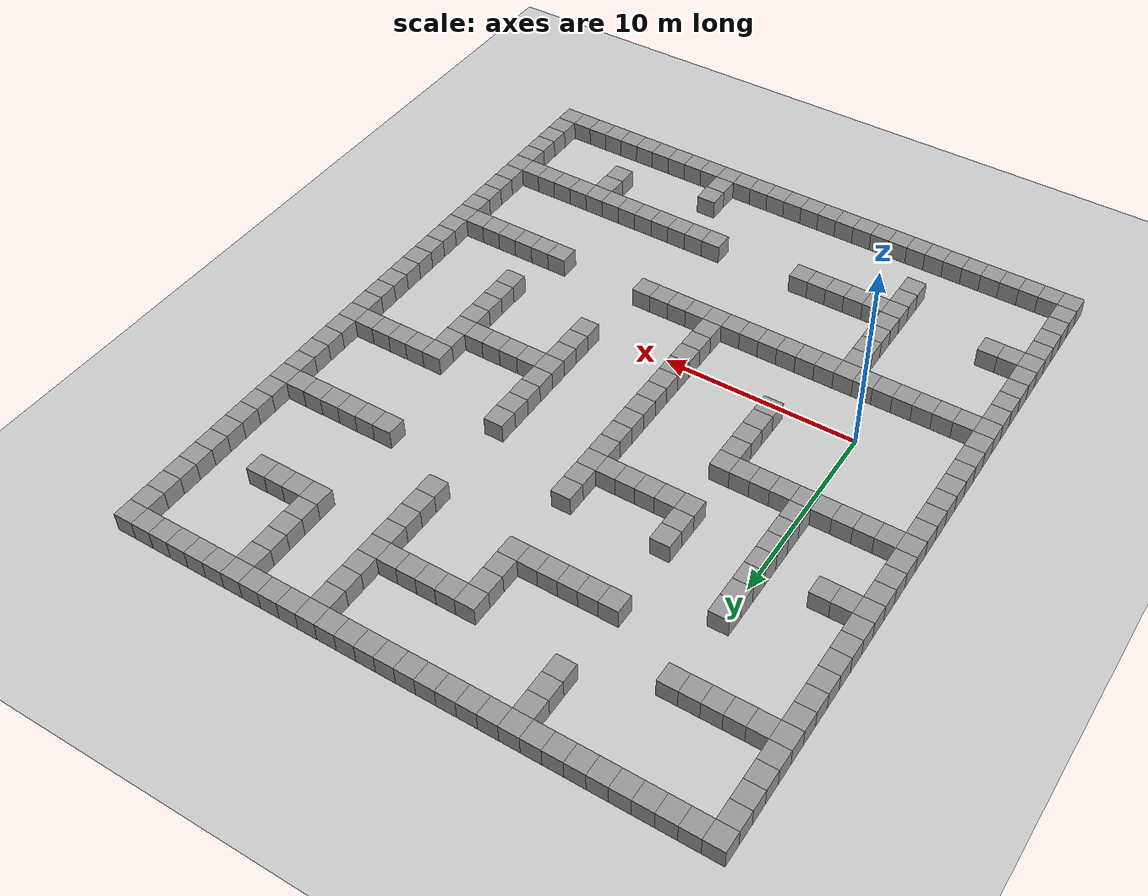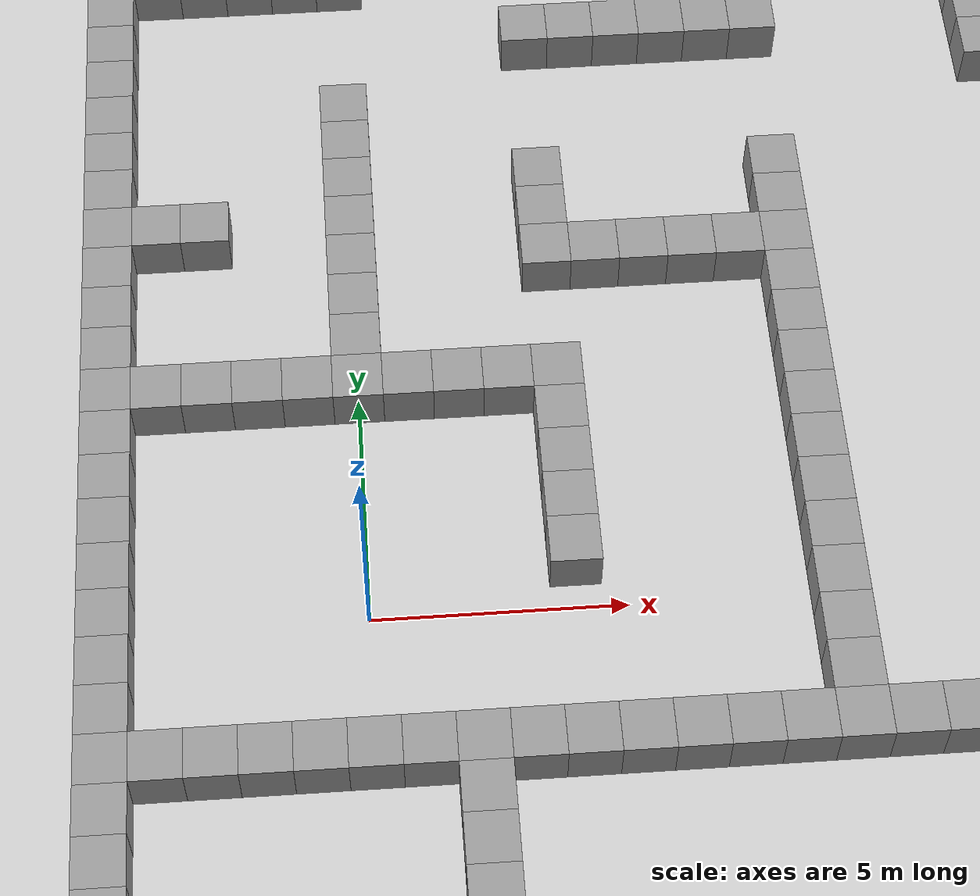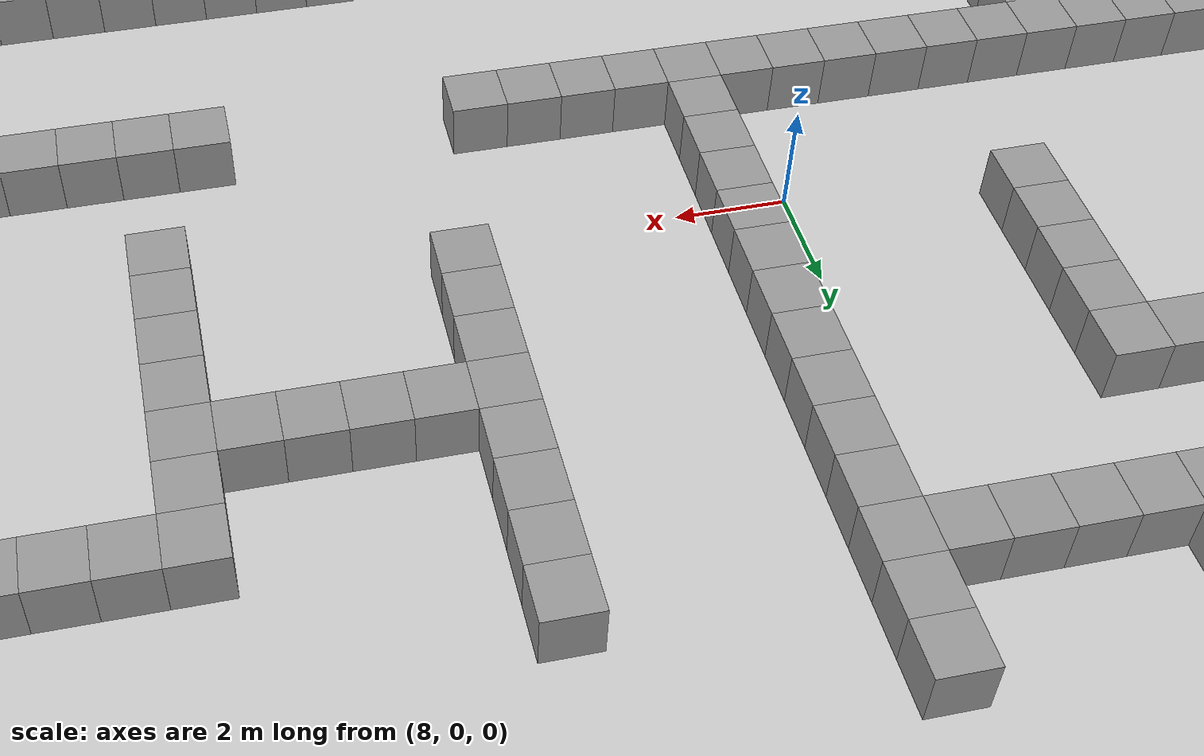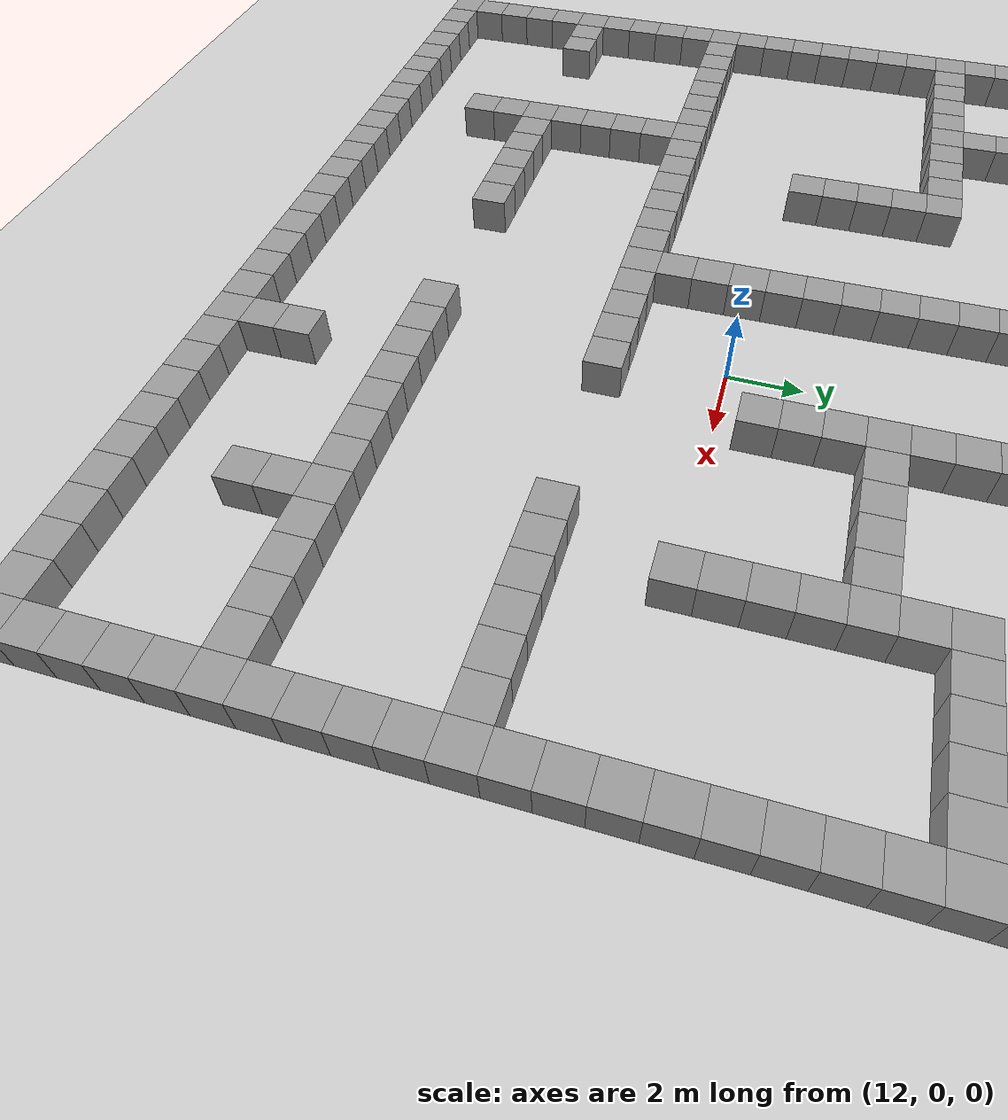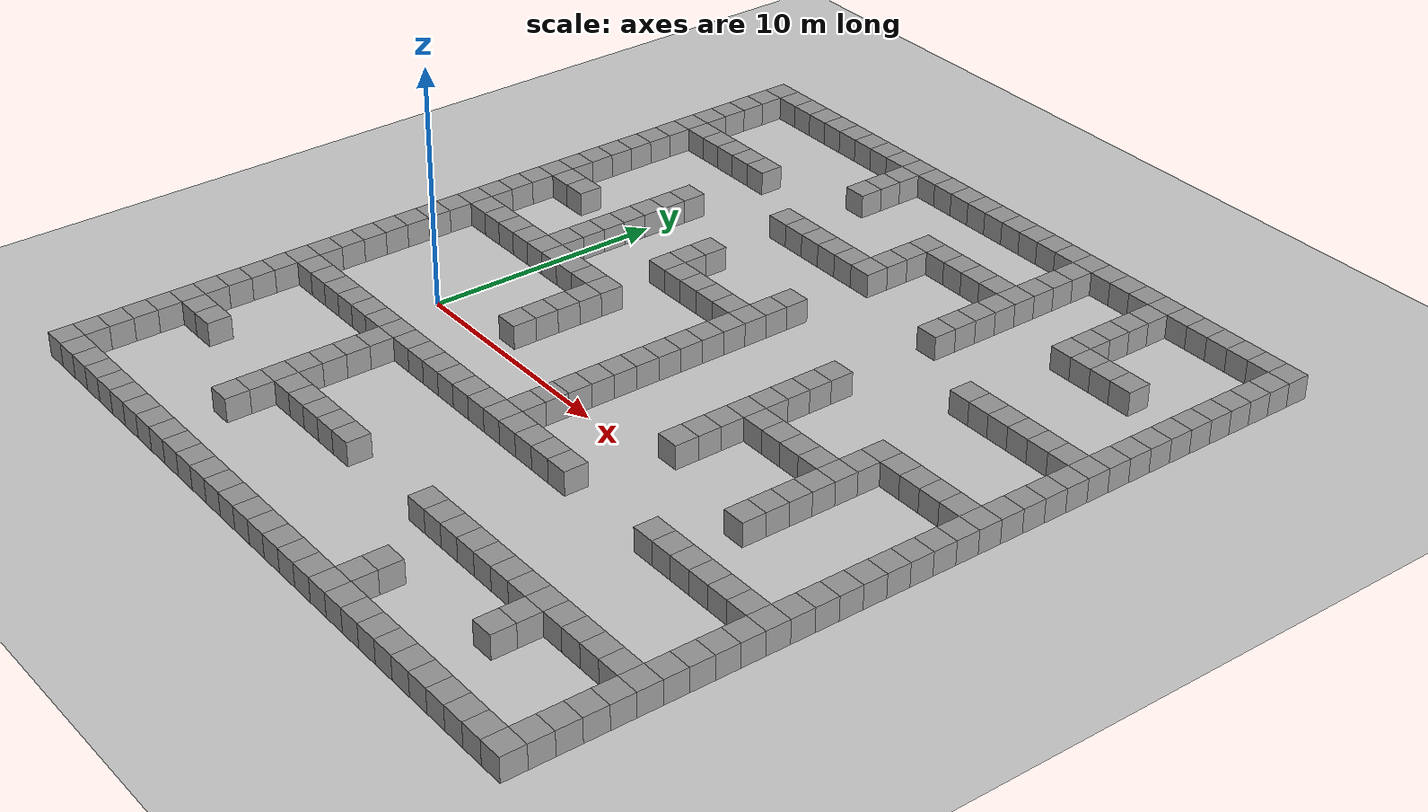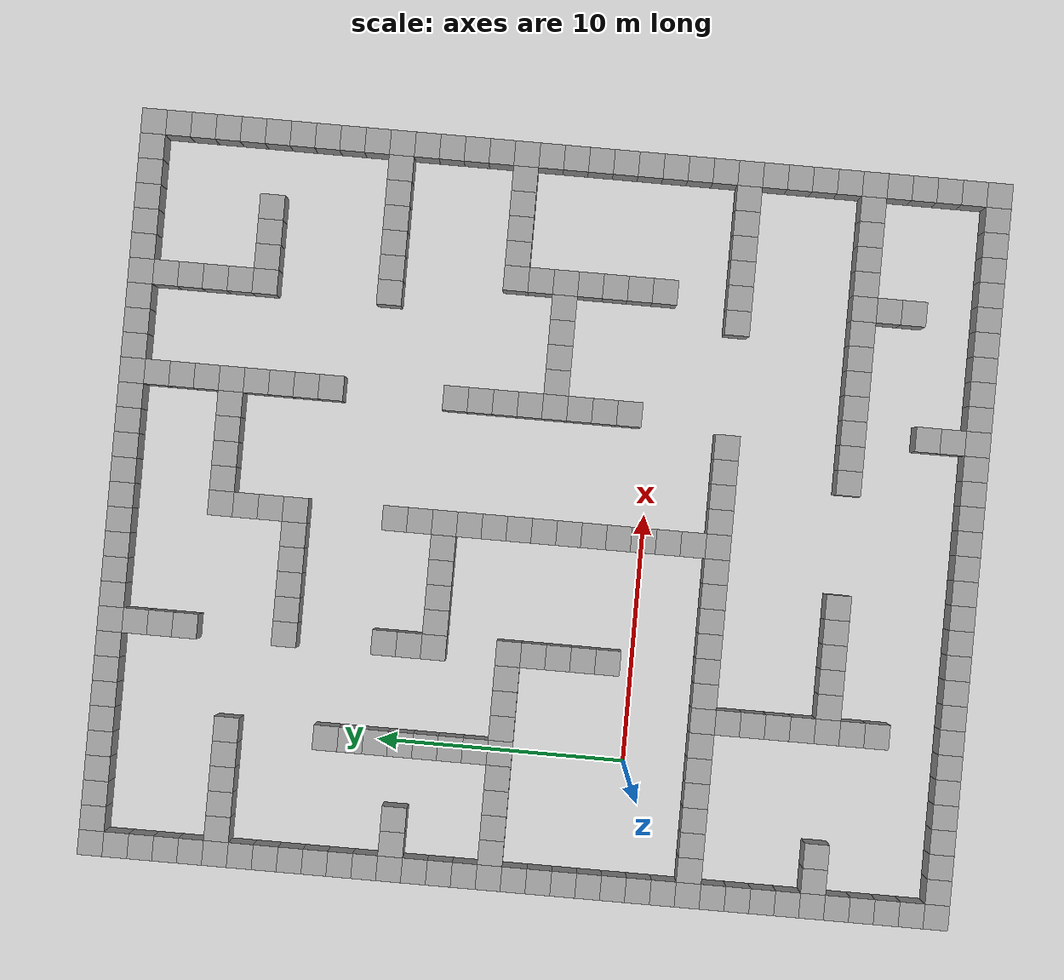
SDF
<sdf version="1.6">
 <world name="default">
  <plugin name="gazebo_occupancy_map" filename="libgazebo_2Dmap_plugin.so">
   <map_resolution>0.05</map_resolution>
   <map_z>0.5</map_z>
   <map_size_x>100</map_size_x>
   <map_size_y>100</map_size_y>
  </plugin>
  <light name="sun" type="directional">
   <pose>0 0 10 0 0 0</pose>
   <diffuse>0.8 0.8 0.8 1</diffuse>
   <specular>0.2 0.2 0.2 1</specular>
   <attenuation>
    <range>1000</range>
    <constant>0.9</constant>
    <linear>0.01</linear>
    <quadratic>0.001</quadratic>
   </attenuation>
   <direction>-0.5 0.1 -0.9</direction>
  </light>
  <model name="ground_plane">
   <static>1</static>
   <link name="link">
    <collision name="collision">
     <geometry><plane><normal>0 0 1</normal><size>100 100</size></plane></geometry>
     <surface><friction><ode><mu>100</mu><mu2>50</mu2></ode></friction></surface>
    </collision>
    <visual name="visual">
     <cast_shadows>0</cast_shadows>
     <geometry><plane><normal>0 0 1</normal><size>100 100</size></plane></geometry>
     <material>
      <script><uri>file://media/materials/scripts/gazebo.material</uri><name>Gazebo/Grey</name></script>
     </material>
    </visual>
    <velocity_decay><linear>0</linear><angular>0</angular></velocity_decay>
   </link>
  </model>
  <physics name="default_physics" default="0" type="ode">
   <max_step_size>0.001</max_step_size>
   <real_time_factor>1</real_time_factor>
   <real_time_update_rate>1000</real_time_update_rate>
  </physics>
  <scene><ambient>0.4 0.4 0.4 1</ambient><background>0.7 0.7 0.7 1</background><shadows>1</shadows></scene>
  <spherical_coordinates>
   <surface_model>EARTH_WGS84</surface_model>
   <latitude_deg>0</latitude_deg>
   <longitude_deg>0</longitude_deg>
   <elevation>0</elevation>
   <heading_deg>0</heading_deg>
  </spherical_coordinates>
  <model name="unit_box_1">
   <pose>-5 5 0.5 0 0 0</pose>
   <static>1</static>
   <link name="link">
    <inertial>
     <mass>1</mass>
     <inertia><ixx>1</ixx><ixy>0</ixy><ixz>0</ixz><iyy>1</iyy><iyz>0</iyz><izz>1</izz></inertia>
    </inertial>
    <collision name="collision"><geometry><box><size>1 1 1</size></box></geometry></collision>
    <visual name="visual">
     <geometry><box><size>1 1 1</size></box></geometry>
     <material>
      <script><uri>file://media/materials/scripts/gazebo.material</uri><name>Gazebo/Grey</name></script>
     </material>
    </visual>
    <velocity_decay><linear>0</linear><angular>0</angular></velocity_decay>
   </link>
   <static>0</static>
  </model>
  <model name="unit_box_2">
   <pose>-4 5 0.5 0 0 0</pose>
   <static>1</static>
   <link name="link">
    <inertial>
     <mass>1</mass>
     <inertia><ixx>1</ixx><ixy>0</ixy><ixz>0</ixz><iyy>1</iyy><iyz>0</iyz><izz>1</izz></inertia>
    </inertial>
    <collision name="collision"><geometry><box><size>1 1 1</size></box></geometry></collision>
    <visual name="visual">
     <geometry><box><size>1 1 1</size></box></geometry>
     <material>
      <script><uri>file://media/materials/scripts/gazebo.material</uri><name>Gazebo/Grey</name></script>
     </material>
    </visual>
    <velocity_decay><linear>0</linear><angular>0</angular></velocity_decay>
   </link>
   <static>0</static>
  </model>
  <model name="unit_box_3">
   <pose>-3 5 0.5 0 0 0</pose>
   <static>1</static>
   <link name="link">
    <inertial>
     <mass>1</mass>
     <inertia><ixx>1</ixx><ixy>0</ixy><ixz>0</ixz><iyy>1</iyy><iyz>0</iyz><izz>1</izz></inertia>
    </inertial>
    <collision name="collision"><geometry><box><size>1 1 1</size></box></geometry></collision>
    <visual name="visual">
     <geometry><box><size>1 1 1</size></box></geometry>
     <material>
      <script><uri>file://media/materials/scripts/gazebo.material</uri><name>Gazebo/Grey</name></script>
     </material>
    </visual>
    <velocity_decay><linear>0</linear><angular>0</angular></velocity_decay>
   </link>
   <static>0</static>
  </model>
  <model name="unit_box_4">
   <pose>-2 5 0.5 0 0 0</pose>
   <static>1</static>
   <link name="link">
    <inertial>
     <mass>1</mass>
     <inertia><ixx>1</ixx><ixy>0</ixy><ixz>0</ixz><iyy>1</iyy><iyz>0</iyz><izz>1</izz></inertia>
    </inertial>
    <collision name="collision"><geometry><box><size>1 1 1</size></box></geometry></collision>
    <visual name="visual">
     <geometry><box><size>1 1 1</size></box></geometry>
     <material>
      <script><uri>file://media/materials/scripts/gazebo.material</uri><name>Gazebo/Grey</name></script>
     </material>
    </visual>
    <velocity_decay><linear>0</linear><angular>0</angular></velocity_decay>
   </link>
   <static>0</static>
  </model>
  <model name="unit_box_5">
   <pose>-1 5 0.5 0 0 0</pose>
   <static>1</static>
   <link name="link">
    <inertial>
     <mass>1</mass>
     <inertia><ixx>1</ixx><ixy>0</ixy><ixz>0</ixz><iyy>1</iyy><iyz>0</iyz><izz>1</izz></inertia>
    </inertial>
    <collision name="collision"><geometry><box><size>1 1 1</size></box></geometry></collision>
    <visual name="visual">
     <geometry><box><size>1 1 1</size></box></geometry>
     <material>
      <script><uri>file://media/materials/scripts/gazebo.material</uri><name>Gazebo/Grey</name></script>
     </material>
    </visual>
    <velocity_decay><linear>0</linear><angular>0</angular></velocity_decay>
   </link>
   <static>0</static>
  </model>
  <model name="unit_box_6">
   <pose>0 5 0.5 0 0 0</pose>
   <static>1</static>
   <link name="link">
    <inertial>
     <mass>1</mass>
     <inertia><ixx>1</ixx><ixy>0</ixy><ixz>0</ixz><iyy>1</iyy><iyz>0</iyz><izz>1</izz></inertia>
    </inertial>
    <collision name="collision"><geometry><box><size>1 1 1</size></box></geometry></collision>
    <visual name="visual">
     <geometry><box><size>1 1 1</size></box></geometry>
     <material>
      <script><uri>file://media/materials/scripts/gazebo.material</uri><name>Gazebo/Grey</name></script>
     </material>
    </visual>
    <velocity_decay><linear>0</linear><angular>0</angular></velocity_decay>
   </link>
   <static>0</static>
  </model>
  <model name="unit_box_7">
   <pose>1 5 0.5 0 0 0</pose>
   <static>1</static>
   <link name="link">
    <inertial>
     <mass>1</mass>
     <inertia><ixx>1</ixx><ixy>0</ixy><ixz>0</ixz><iyy>1</iyy><iyz>0</iyz><izz>1</izz></inertia>
    </inertial>
    <collision name="collision"><geometry><box><size>1 1 1</size></box></geometry></collision>
    <visual name="visual">
     <geometry><box><size>1 1 1</size></box></geometry>
     <material>
      <script><uri>file://media/materials/scripts/gazebo.material</uri><name>Gazebo/Grey</name></script>
     </material>
    </visual>
    <velocity_decay><linear>0</linear><angular>0</angular></velocity_decay>
   </link>
   <static>0</static>
  </model>
  <model name="unit_box_8">
   <pose>2 5 0.5 0 0 0</pose>
   <static>1</static>
   <link name="link">
    <inertial>
     <mass>1</mass>
     <inertia><ixx>1</ixx><ixy>0</ixy><ixz>0</ixz><iyy>1</iyy><iyz>0</iyz><izz>1</izz></inertia>
    </inertial>
    <collision name="collision"><geometry><box><size>1 1 1</size></box></geometry></collision>
    <visual name="visual">
     <geometry><box><size>1 1 1</size></box></geometry>
     <material>
      <script><uri>file://media/materials/scripts/gazebo.material</uri><name>Gazebo/Grey</name></script>
     </material>
    </visual>
    <velocity_decay><linear>0</linear><angular>0</angular></velocity_decay>
   </link>
   <static>0</static>
  </model>
  <model name="unit_box_9">
   <pose>3 5 0.5 0 0 0</pose>
   <static>1</static>
   <link name="link">
    <inertial>
     <mass>1</mass>
     <inertia><ixx>1</ixx><ixy>0</ixy><ixz>0</ixz><iyy>1</iyy><iyz>0</iyz><izz>1</izz></inertia>
    </inertial>
    <collision name="collision"><geometry><box><size>1 1 1</size></box></geometry></collision>
    <visual name="visual">
     <geometry><box><size>1 1 1</size></box></geometry>
     <material>
      <script><uri>file://media/materials/scripts/gazebo.material</uri><name>Gazebo/Grey</name></script>
     </material>
    </visual>
    <velocity_decay><linear>0</linear><angular>0</angular></velocity_decay>
   </link>
   <static>0</static>
  </model>
  <model name="unit_box_10">
   <pose>4 5 0.5 0 0 0</pose>
   <static>1</static>
   <link name="link">
    <inertial>
     <mass>1</mass>
     <inertia><ixx>1</ixx><ixy>0</ixy><ixz>0</ixz><iyy>1</iyy><iyz>0</iyz><izz>1</izz></inertia>
    </inertial>
    <collision name="collision"><geometry><box><size>1 1 1</size></box></geometry></collision>
    <visual name="visual">
     <geometry><box><size>1 1 1</size></box></geometry>
     <material>
      <script><uri>file://media/materials/scripts/gazebo.material</uri><name>Gazebo/Grey</name></script>
     </material>
    </visual>
    <velocity_decay><linear>0</linear><angular>0</angular></velocity_decay>
   </link>
   <static>0</static>
  </model>
  <model name="unit_box_11">
   <pose>4 4 0.5 0 0 0</pose>
   <static>1</static>
   <link name="link">
    <inertial>
     <mass>1</mass>
     <inertia><ixx>1</ixx><ixy>0</ixy><ixz>0</ixz><iyy>1</iyy><iyz>0</iyz><izz>1</izz></inertia>
    </inertial>
    <collision name="collision"><geometry><box><size>1 1 1</size></box></geometry></collision>
    <visual name="visual">
     <geometry><box><size>1 1 1</size></box></geometry>
     <material>
      <script><uri>file://media/materials/scripts/gazebo.material</uri><name>Gazebo/Grey</name></script>
     </material>
    </visual>
    <velocity_decay><linear>0</linear><angular>0</angular></velocity_decay>
   </link>
   <static>0</static>
  </model>
  <model name="unit_box_12">
   <pose>4 3 0.5 0 0 0</pose>
   <static>1</static>
   <link name="link">
    <inertial>
     <mass>1</mass>
     <inertia><ixx>1</ixx><ixy>0</ixy><ixz>0</ixz><iyy>1</iyy><iyz>0</iyz><izz>1</izz></inertia>
    </inertial>
    <collision name="collision"><geometry><box><size>1 1 1</size></box></geometry></collision>
    <visual name="visual">
     <geometry><box><size>1 1 1</size></box></geometry>
     <material>
      <script><uri>file://media/materials/scripts/gazebo.material</uri><name>Gazebo/Grey</name></script>
     </material>
    </visual>
    <velocity_decay><linear>0</linear><angular>0</angular></velocity_decay>
   </link>
   <static>0</static>
  </model>
  <model name="unit_box_13">
   <pose>4 2 0.5 0 0 0</pose>
   <static>1</static>
   <link name="link">
    <inertial>
     <mass>1</mass>
     <inertia><ixx>1</ixx><ixy>0</ixy><ixz>0</ixz><iyy>1</iyy><iyz>0</iyz><izz>1</izz></inertia>
    </inertial>
    <collision name="collision"><geometry><box><size>1 1 1</size></box></geometry></collision>
    <visual name="visual">
     <geometry><box><size>1 1 1</size></box></geometry>
     <material>
      <script><uri>file://media/materials/scripts/gazebo.material</uri><name>Gazebo/Grey</name></script>
     </material>
    </visual>
    <velocity_decay><linear>0</linear><angular>0</angular></velocity_decay>
   </link>
   <static>0</static>
  </model>
  <model name="unit_box_14">
   <pose>4 1 0.5 0 0 0</pose>
   <static>1</static>
   <link name="link">
    <inertial>
     <mass>1</mass>
     <inertia><ixx>1</ixx><ixy>0</ixy><ixz>0</ixz><iyy>1</iyy><iyz>0</iyz><izz>1</izz></inertia>
    </inertial>
    <collision name="collision"><geometry><box><size>1 1 1</size></box></geometry></collision>
    <visual name="visual">
     <geometry><box><size>1 1 1</size></box></geometry>
     <material>
      <script><uri>file://media/materials/scripts/gazebo.material</uri><name>Gazebo/Grey</name></script>
     </material>
    </visual>
    <velocity_decay><linear>0</linear><angular>0</angular></velocity_decay>
   </link>
   <static>0</static>
  </model>
  <model name="unit_box_15">
   <pose>-1 -3 0.5 0 0 0</pose>
   <static>1</static>
   <link name="link">
    <inertial>
     <mass>1</mass>
     <inertia><ixx>1</ixx><ixy>0</ixy><ixz>0</ixz><iyy>1</iyy><iyz>0</iyz><izz>1</izz></inertia>
    </inertial>
    <collision name="collision"><geometry><box><size>1 1 1</size></box></geometry></collision>
    <visual name="visual">
     <geometry><box><size>1 1 1</size></box></geometry>
     <material>
      <script><uri>file://media/materials/scripts/gazebo.material</uri><name>Gazebo/Grey</name></script>
     </material>
    </visual>
    <velocity_decay><linear>0</linear><angular>0</angular></velocity_decay>
   </link>
   <static>0</static>
  </model>
  <model name="unit_box_16">
   <pose>0 -3 0.5 0 0 0</pose>
   <static>1</static>
   <link name="link">
    <inertial>
     <mass>1</mass>
     <inertia><ixx>1</ixx><ixy>0</ixy><ixz>0</ixz><iyy>1</iyy><iyz>0</iyz><izz>1</izz></inertia>
    </inertial>
    <collision name="collision"><geometry><box><size>1 1 1</size></box></geometry></collision>
    <visual name="visual">
     <geometry><box><size>1 1 1</size></box></geometry>
     <material>
      <script><uri>file://media/materials/scripts/gazebo.material</uri><name>Gazebo/Grey</name></script>
     </material>
    </visual>
    <velocity_decay><linear>0</linear><angular>0</angular></velocity_decay>
   </link>
   <static>0</static>
  </model>
  <model name="unit_box_17">
   <pose>1 -3 0.5 0 0 0</pose>
   <static>1</static>
   <link name="link">
    <inertial>
     <mass>1</mass>
     <inertia><ixx>1</ixx><ixy>0</ixy><ixz>0</ixz><iyy>1</iyy><iyz>0</iyz><izz>1</izz></inertia>
    </inertial>
    <collision name="collision"><geometry><box><size>1 1 1</size></box></geometry></collision>
    <visual name="visual">
     <geometry><box><size>1 1 1</size></box></geometry>
     <material>
      <script><uri>file://media/materials/scripts/gazebo.material</uri><name>Gazebo/Grey</name></script>
     </material>
    </visual>
    <velocity_decay><linear>0</linear><angular>0</angular></velocity_decay>
   </link>
   <static>0</static>
  </model>
  <model name="unit_box_18">
   <pose>2 -3 0.5 0 0 0</pose>
   <static>1</static>
   <link name="link">
    <inertial>
     <mass>1</mass>
     <inertia><ixx>1</ixx><ixy>0</ixy><ixz>0</ixz><iyy>1</iyy><iyz>0</iyz><izz>1</izz></inertia>
    </inertial>
    <collision name="collision"><geometry><box><size>1 1 1</size></box></geometry></collision>
    <visual name="visual">
     <geometry><box><size>1 1 1</size></box></geometry>
     <material>
      <script><uri>file://media/materials/scripts/gazebo.material</uri><name>Gazebo/Grey</name></script>
     </material>
    </visual>
    <velocity_decay><linear>0</linear><angular>0</angular></velocity_decay>
   </link>
   <static>0</static>
  </model>
  <model name="unit_box_19">
   <pose>3 -3 0.5 0 0 0</pose>
   <static>1</static>
   <link name="link">
    <inertial>
     <mass>1</mass>
     <inertia><ixx>1</ixx><ixy>0</ixy><ixz>0</ixz><iyy>1</iyy><iyz>0</iyz><izz>1</izz></inertia>
    </inertial>
    <collision name="collision"><geometry><box><size>1 1 1</size></box></geometry></collision>
    <visual name="visual">
     <geometry><box><size>1 1 1</size></box></geometry>
     <material>
      <script><uri>file://media/materials/scripts/gazebo.material</uri><name>Gazebo/Grey</name></script>
     </material>
    </visual>
    <velocity_decay><linear>0</linear><angular>0</angular></velocity_decay>
   </link>
   <static>0</static>
  </model>
  <model name="unit_box_20">
   <pose>4 -3 0.5 0 0 0</pose>
   <static>1</static>
   <link name="link">
    <inertial>
     <mass>1</mass>
     <inertia><ixx>1</ixx><ixy>0</ixy><ixz>0</ixz><iyy>1</iyy><iyz>0</iyz><izz>1</izz></inertia>
    </inertial>
    <collision name="collision"><geometry><box><size>1 1 1</size></box></geometry></collision>
    <visual name="visual">
     <geometry><box><size>1 1 1</size></box></geometry>
     <material>
      <script><uri>file://media/materials/scripts/gazebo.material</uri><name>Gazebo/Grey</name></script>
     </material>
    </visual>
    <velocity_decay><linear>0</linear><angular>0</angular></velocity_decay>
   </link>
   <static>0</static>
  </model>
  <model name="unit_box_21">
   <pose>5 -3 0.5 0 0 0</pose>
   <static>1</static>
   <link name="link">
    <inertial>
     <mass>1</mass>
     <inertia><ixx>1</ixx><ixy>0</ixy><ixz>0</ixz><iyy>1</iyy><iyz>0</iyz><izz>1</izz></inertia>
    </inertial>
    <collision name="collision"><geometry><box><size>1 1 1</size></box></geometry></collision>
    <visual name="visual">
     <geometry><box><size>1 1 1</size></box></geometry>
     <material>
      <script><uri>file://media/materials/scripts/gazebo.material</uri><name>Gazebo/Grey</name></script>
     </material>
    </visual>
    <velocity_decay><linear>0</linear><angular>0</angular></velocity_decay>
   </link>
   <static>0</static>
  </model>
  <model name="unit_box_22">
   <pose>6 -3 0.5 0 0 0</pose>
   <static>1</static>
   <link name="link">
    <inertial>
     <mass>1</mass>
     <inertia><ixx>1</ixx><ixy>0</ixy><ixz>0</ixz><iyy>1</iyy><iyz>0</iyz><izz>1</izz></inertia>
    </inertial>
    <collision name="collision"><geometry><box><size>1 1 1</size></box></geometry></collision>
    <visual name="visual">
     <geometry><box><size>1 1 1</size></box></geometry>
     <material>
      <script><uri>file://media/materials/scripts/gazebo.material</uri><name>Gazebo/Grey</name></script>
     </material>
    </visual>
    <velocity_decay><linear>0</linear><angular>0</angular></velocity_decay>
   </link>
   <static>0</static>
  </model>
  <model name="unit_box_23">
   <pose>7 -3 0.5 0 0 0</pose>
   <static>1</static>
   <link name="link">
    <inertial>
     <mass>1</mass>
     <inertia><ixx>1</ixx><ixy>0</ixy><ixz>0</ixz><iyy>1</iyy><iyz>0</iyz><izz>1</izz></inertia>
    </inertial>
    <collision name="collision"><geometry><box><size>1 1 1</size></box></geometry></collision>
    <visual name="visual">
     <geometry><box><size>1 1 1</size></box></geometry>
     <material>
      <script><uri>file://media/materials/scripts/gazebo.material</uri><name>Gazebo/Grey</name></script>
     </material>
    </visual>
    <velocity_decay><linear>0</linear><angular>0</angular></velocity_decay>
   </link>
   <static>0</static>
  </model>
  <model name="unit_box_24">
   <pose>8 -3 0.5 0 0 0</pose>
   <static>1</static>
   <link name="link">
    <inertial>
     <mass>1</mass>
     <inertia><ixx>1</ixx><ixy>0</ixy><ixz>0</ixz><iyy>1</iyy><iyz>0</iyz><izz>1</izz></inertia>
    </inertial>
    <collision name="collision"><geometry><box><size>1 1 1</size></box></geometry></collision>
    <visual name="visual">
     <geometry><box><size>1 1 1</size></box></geometry>
     <material>
      <script><uri>file://media/materials/scripts/gazebo.material</uri><name>Gazebo/Grey</name></script>
     </material>
    </visual>
    <velocity_decay><linear>0</linear><angular>0</angular></velocity_decay>
   </link>
   <static>0</static>
  </model>
  <model name="unit_box_25">
   <pose>9 -3 0.5 0 0 0</pose>
   <static>1</static>
   <link name="link">
    <inertial>
     <mass>1</mass>
     <inertia><ixx>1</ixx><ixy>0</ixy><ixz>0</ixz><iyy>1</iyy><iyz>0</iyz><izz>1</izz></inertia>
    </inertial>
    <collision name="collision"><geometry><box><size>1 1 1</size></box></geometry></collision>
    <visual name="visual">
     <geometry><box><size>1 1 1</size></box></geometry>
     <material>
      <script><uri>file://media/materials/scripts/gazebo.material</uri><name>Gazebo/Grey</name></script>
     </material>
    </visual>
    <velocity_decay><linear>0</linear><angular>0</angular></velocity_decay>
   </link>
   <static>0</static>
  </model>
  <model name="unit_box_26">
   <pose>9 -2 0.5 0 0 0</pose>
   <static>1</static>
   <link name="link">
    <inertial>
     <mass>1</mass>
     <inertia><ixx>1</ixx><ixy>0</ixy><ixz>0</ixz><iyy>1</iyy><iyz>0</iyz><izz>1</izz></inertia>
    </inertial>
    <collision name="collision"><geometry><box><size>1 1 1</size></box></geometry></collision>
    <visual name="visual">
     <geometry><box><size>1 1 1</size></box></geometry>
     <material>
      <script><uri>file://media/materials/scripts/gazebo.material</uri><name>Gazebo/Grey</name></script>
     </material>
    </visual>
    <velocity_decay><linear>0</linear><angular>0</angular></velocity_decay>
   </link>
   <static>0</static>
  </model>
  <model name="unit_box_27">
   <pose>9 -1 0.5 0 0 0</pose>
   <static>1</static>
   <link name="link">
    <inertial>
     <mass>1</mass>
     <inertia><ixx>1</ixx><ixy>0</ixy><ixz>0</ixz><iyy>1</iyy><iyz>0</iyz><izz>1</izz></inertia>
    </inertial>
    <collision name="collision"><geometry><box><size>1 1 1</size></box></geometry></collision>
    <visual name="visual">
     <geometry><box><size>1 1 1</size></box></geometry>
     <material>
      <script><uri>file://media/materials/scripts/gazebo.material</uri><name>Gazebo/Grey</name></script>
     </material>
    </visual>
    <velocity_decay><linear>0</linear><angular>0</angular></velocity_decay>
   </link>
   <static>0</static>
  </model>
  <model name="unit_box_28">
   <pose>9 0 0.5 0 0 0</pose>
   <static>1</static>
   <link name="link">
    <inertial>
     <mass>1</mass>
     <inertia><ixx>1</ixx><ixy>0</ixy><ixz>0</ixz><iyy>1</iyy><iyz>0</iyz><izz>1</izz></inertia>
    </inertial>
    <collision name="collision"><geometry><box><size>1 1 1</size></box></geometry></collision>
    <visual name="visual">
     <geometry><box><size>1 1 1</size></box></geometry>
     <material>
      <script><uri>file://media/materials/scripts/gazebo.material</uri><name>Gazebo/Grey</name></script>
     </material>
    </visual>
    <velocity_decay><linear>0</linear><angular>0</angular></velocity_decay>
   </link>
   <static>0</static>
  </model>
  <model name="unit_box_29">
   <pose>9 1 0.5 0 0 0</pose>
   <static>1</static>
   <link name="link">
    <inertial>
     <mass>1</mass>
     <inertia><ixx>1</ixx><ixy>0</ixy><ixz>0</ixz><iyy>1</iyy><iyz>0</iyz><izz>1</izz></inertia>
    </inertial>
    <collision name="collision"><geometry><box><size>1 1 1</size></box></geometry></collision>
    <visual name="visual">
     <geometry><box><size>1 1 1</size></box></geometry>
     <material>
      <script><uri>file://media/materials/scripts/gazebo.material</uri><name>Gazebo/Grey</name></script>
     </material>
    </visual>
    <velocity_decay><linear>0</linear><angular>0</angular></velocity_decay>
   </link>
   <static>0</static>
  </model>
  <model name="unit_box_30">
   <pose>9 2 0.5 0 0 0</pose>
   <static>1</static>
   <link name="link">
    <inertial>
     <mass>1</mass>
     <inertia><ixx>1</ixx><ixy>0</ixy><ixz>0</ixz><iyy>1</iyy><iyz>0</iyz><izz>1</izz></inertia>
    </inertial>
    <collision name="collision"><geometry><box><size>1 1 1</size></box></geometry></collision>
    <visual name="visual">
     <geometry><box><size>1 1 1</size></box></geometry>
     <material>
      <script><uri>file://media/materials/scripts/gazebo.material</uri><name>Gazebo/Grey</name></script>
     </material>
    </visual>
    <velocity_decay><linear>0</linear><angular>0</angular></velocity_decay>
   </link>
   <static>0</static>
  </model>
  <model name="unit_box_31">
   <pose>9 3 0.5 0 0 0</pose>
   <static>1</static>
   <link name="link">
    <inertial>
     <mass>1</mass>
     <inertia><ixx>1</ixx><ixy>0</ixy><ixz>0</ixz><iyy>1</iyy><iyz>0</iyz><izz>1</izz></inertia>
    </inertial>
    <collision name="collision"><geometry><box><size>1 1 1</size></box></geometry></collision>
    <visual name="visual">
     <geometry><box><size>1 1 1</size></box></geometry>
     <material>
      <script><uri>file://media/materials/scripts/gazebo.material</uri><name>Gazebo/Grey</name></script>
     </material>
    </visual>
    <velocity_decay><linear>0</linear><angular>0</angular></velocity_decay>
   </link>
   <static>0</static>
  </model>
  <model name="unit_box_32">
   <pose>9 4 0.5 0 0 0</pose>
   <static>1</static>
   <link name="link">
    <inertial>
     <mass>1</mass>
     <inertia><ixx>1</ixx><ixy>0</ixy><ixz>0</ixz><iyy>1</iyy><iyz>0</iyz><izz>1</izz></inertia>
    </inertial>
    <collision name="collision"><geometry><box><size>1 1 1</size></box></geometry></collision>
    <visual name="visual">
     <geometry><box><size>1 1 1</size></box></geometry>
     <material>
      <script><uri>file://media/materials/scripts/gazebo.material</uri><name>Gazebo/Grey</name></script>
     </material>
    </visual>
    <velocity_decay><linear>0</linear><angular>0</angular></velocity_decay>
   </link>
   <static>0</static>
  </model>
  <model name="unit_box_33">
   <pose>9 5 0.5 0 0 0</pose>
   <static>1</static>
   <link name="link">
    <inertial>
     <mass>1</mass>
     <inertia><ixx>1</ixx><ixy>0</ixy><ixz>0</ixz><iyy>1</iyy><iyz>0</iyz><izz>1</izz></inertia>
    </inertial>
    <collision name="collision"><geometry><box><size>1 1 1</size></box></geometry></collision>
    <visual name="visual">
     <geometry><box><size>1 1 1</size></box></geometry>
     <material>
      <script><uri>file://media/materials/scripts/gazebo.material</uri><name>Gazebo/Grey</name></script>
     </material>
    </visual>
    <velocity_decay><linear>0</linear><angular>0</angular></velocity_decay>
   </link>
   <static>0</static>
  </model>
  <model name="unit_box_34">
   <pose>9 6 0.5 0 0 0</pose>
   <static>1</static>
   <link name="link">
    <inertial>
     <mass>1</mass>
     <inertia><ixx>1</ixx><ixy>0</ixy><ixz>0</ixz><iyy>1</iyy><iyz>0</iyz><izz>1</izz></inertia>
    </inertial>
    <collision name="collision"><geometry><box><size>1 1 1</size></box></geometry></collision>
    <visual name="visual">
     <geometry><box><size>1 1 1</size></box></geometry>
     <material>
      <script><uri>file://media/materials/scripts/gazebo.material</uri><name>Gazebo/Grey</name></script>
     </material>
    </visual>
    <velocity_decay><linear>0</linear><angular>0</angular></velocity_decay>
   </link>
   <static>0</static>
  </model>
  <model name="unit_box_35">
   <pose>10 -3 0.5 0 0 0</pose>
   <static>1</static>
   <link name="link">
    <inertial>
     <mass>1</mass>
     <inertia><ixx>1</ixx><ixy>0</ixy><ixz>0</ixz><iyy>1</iyy><iyz>0</iyz><izz>1</izz></inertia>
    </inertial>
    <collision name="collision"><geometry><box><size>1 1 1</size></box></geometry></collision>
    <visual name="visual">
     <geometry><box><size>1 1 1</size></box></geometry>
     <material>
      <script><uri>file://media/materials/scripts/gazebo.material</uri><name>Gazebo/Grey</name></script>
     </material>
    </visual>
    <velocity_decay><linear>0</linear><angular>0</angular></velocity_decay>
   </link>
   <static>0</static>
  </model>
  <model name="unit_box_36">
   <pose>11 -3 0.5 0 0 0</pose>
   <static>1</static>
   <link name="link">
    <inertial>
     <mass>1</mass>
     <inertia><ixx>1</ixx><ixy>0</ixy><ixz>0</ixz><iyy>1</iyy><iyz>0</iyz><izz>1</izz></inertia>
    </inertial>
    <collision name="collision"><geometry><box><size>1 1 1</size></box></geometry></collision>
    <visual name="visual">
     <geometry><box><size>1 1 1</size></box></geometry>
     <material>
      <script><uri>file://media/materials/scripts/gazebo.material</uri><name>Gazebo/Grey</name></script>
     </material>
    </visual>
    <velocity_decay><linear>0</linear><angular>0</angular></velocity_decay>
   </link>
   <static>0</static>
  </model>
  <model name="unit_box_37">
   <pose>12 -3 0.5 0 0 0</pose>
   <static>1</static>
   <link name="link">
    <inertial>
     <mass>1</mass>
     <inertia><ixx>1</ixx><ixy>0</ixy><ixz>0</ixz><iyy>1</iyy><iyz>0</iyz><izz>1</izz></inertia>
    </inertial>
    <collision name="collision"><geometry><box><size>1 1 1</size></box></geometry></collision>
    <visual name="visual">
     <geometry><box><size>1 1 1</size></box></geometry>
     <material>
      <script><uri>file://media/materials/scripts/gazebo.material</uri><name>Gazebo/Grey</name></script>
     </material>
    </visual>
    <velocity_decay><linear>0</linear><angular>0</angular></velocity_decay>
   </link>
   <static>0</static>
  </model>
  <model name="unit_box_38">
   <pose>9 7 0.5 0 0 0</pose>
   <static>1</static>
   <link name="link">
    <inertial>
     <mass>1</mass>
     <inertia><ixx>1</ixx><ixy>0</ixy><ixz>0</ixz><iyy>1</iyy><iyz>0</iyz><izz>1</izz></inertia>
    </inertial>
    <collision name="collision"><geometry><box><size>1 1 1</size></box></geometry></collision>
    <visual name="visual">
     <geometry><box><size>1 1 1</size></box></geometry>
     <material>
      <script><uri>file://media/materials/scripts/gazebo.material</uri><name>Gazebo/Grey</name></script>
     </material>
    </visual>
    <velocity_decay><linear>0</linear><angular>0</angular></velocity_decay>
   </link>
   <static>0</static>
  </model>
  <model name="unit_box_39">
   <pose>9 8 0.5 0 0 0</pose>
   <static>1</static>
   <link name="link">
    <inertial>
     <mass>1</mass>
     <inertia><ixx>1</ixx><ixy>0</ixy><ixz>0</ixz><iyy>1</iyy><iyz>0</iyz><izz>1</izz></inertia>
    </inertial>
    <collision name="collision"><geometry><box><size>1 1 1</size></box></geometry></collision>
    <visual name="visual">
     <geometry><box><size>1 1 1</size></box></geometry>
     <material>
      <script><uri>file://media/materials/scripts/gazebo.material</uri><name>Gazebo/Grey</name></script>
     </material>
    </visual>
    <velocity_decay><linear>0</linear><angular>0</angular></velocity_decay>
   </link>
   <static>0</static>
  </model>
  <model name="unit_box_40">
   <pose>-5 4 0.5 0 0 0</pose>
   <static>1</static>
   <link name="link">
    <inertial>
     <mass>1</mass>
     <inertia><ixx>1</ixx><ixy>0</ixy><ixz>0</ixz><iyy>1</iyy><iyz>0</iyz><izz>1</izz></inertia>
    </inertial>
    <collision name="collision"><geometry><box><size>1 1 1</size></box></geometry></collision>
    <visual name="visual">
     <geometry><box><size>1 1 1</size></box></geometry>
     <material>
      <script><uri>file://media/materials/scripts/gazebo.material</uri><name>Gazebo/Grey</name></script>
     </material>
    </visual>
    <velocity_decay><linear>0</linear><angular>0</angular></velocity_decay>
   </link>
   <static>0</static>
  </model>
  <model name="unit_box_41">
   <pose>-5 3 0.5 0 0 0</pose>
   <static>1</static>
   <link name="link">
    <inertial>
     <mass>1</mass>
     <inertia><ixx>1</ixx><ixy>0</ixy><ixz>0</ixz><iyy>1</iyy><iyz>0</iyz><izz>1</izz></inertia>
    </inertial>
    <collision name="collision"><geometry><box><size>1 1 1</size></box></geometry></collision>
    <visual name="visual">
     <geometry><box><size>1 1 1</size></box></geometry>
     <material>
      <script><uri>file://media/materials/scripts/gazebo.material</uri><name>Gazebo/Grey</name></script>
     </material>
    </visual>
    <velocity_decay><linear>0</linear><angular>0</angular></velocity_decay>
   </link>
   <static>0</static>
  </model>
  <model name="unit_box_42">
   <pose>-5 2 0.5 0 0 0</pose>
   <static>1</static>
   <link name="link">
    <inertial>
     <mass>1</mass>
     <inertia><ixx>1</ixx><ixy>0</ixy><ixz>0</ixz><iyy>1</iyy><iyz>0</iyz><izz>1</izz></inertia>
    </inertial>
    <collision name="collision"><geometry><box><size>1 1 1</size></box></geometry></collision>
    <visual name="visual">
     <geometry><box><size>1 1 1</size></box></geometry>
     <material>
      <script><uri>file://media/materials/scripts/gazebo.material</uri><name>Gazebo/Grey</name></script>
     </material>
    </visual>
    <velocity_decay><linear>0</linear><angular>0</angular></velocity_decay>
   </link>
   <static>0</static>
  </model>
  <model name="unit_box_43">
   <pose>-5 1 0.5 0 0 0</pose>
   <static>1</static>
   <link name="link">
    <inertial>
     <mass>1</mass>
     <inertia><ixx>1</ixx><ixy>0</ixy><ixz>0</ixz><iyy>1</iyy><iyz>0</iyz><izz>1</izz></inertia>
    </inertial>
    <collision name="collision"><geometry><box><size>1 1 1</size></box></geometry></collision>
    <visual name="visual">
     <geometry><box><size>1 1 1</size></box></geometry>
     <material>
      <script><uri>file://media/materials/scripts/gazebo.material</uri><name>Gazebo/Grey</name></script>
     </material>
    </visual>
    <velocity_decay><linear>0</linear><angular>0</angular></velocity_decay>
   </link>
   <static>0</static>
  </model>
  <model name="unit_box_44">
   <pose>-5 0 0.5 0 0 0</pose>
   <static>1</static>
   <link name="link">
    <inertial>
     <mass>1</mass>
     <inertia><ixx>1</ixx><ixy>0</ixy><ixz>0</ixz><iyy>1</iyy><iyz>0</iyz><izz>1</izz></inertia>
    </inertial>
    <collision name="collision"><geometry><box><size>1 1 1</size></box></geometry></collision>
    <visual name="visual">
     <geometry><box><size>1 1 1</size></box></geometry>
     <material>
      <script><uri>file://media/materials/scripts/gazebo.material</uri><name>Gazebo/Grey</name></script>
     </material>
    </visual>
    <velocity_decay><linear>0</linear><angular>0</angular></velocity_decay>
   </link>
   <static>0</static>
  </model>
  <model name="unit_box_45">
   <pose>-5 -1 0.5 0 0 0</pose>
   <static>1</static>
   <link name="link">
    <inertial>
     <mass>1</mass>
     <inertia><ixx>1</ixx><ixy>0</ixy><ixz>0</ixz><iyy>1</iyy><iyz>0</iyz><izz>1</izz></inertia>
    </inertial>
    <collision name="collision"><geometry><box><size>1 1 1</size></box></geometry></collision>
    <visual name="visual">
     <geometry><box><size>1 1 1</size></box></geometry>
     <material>
      <script><uri>file://media/materials/scripts/gazebo.material</uri><name>Gazebo/Grey</name></script>
     </material>
    </visual>
    <velocity_decay><linear>0</linear><angular>0</angular></velocity_decay>
   </link>
   <static>0</static>
  </model>
  <model name="unit_box_46">
   <pose>-5 -2 0.5 0 0 0</pose>
   <static>1</static>
   <link name="link">
    <inertial>
     <mass>1</mass>
     <inertia><ixx>1</ixx><ixy>0</ixy><ixz>0</ixz><iyy>1</iyy><iyz>0</iyz><izz>1</izz></inertia>
    </inertial>
    <collision name="collision"><geometry><box><size>1 1 1</size></box></geometry></collision>
    <visual name="visual">
     <geometry><box><size>1 1 1</size></box></geometry>
     <material>
      <script><uri>file://media/materials/scripts/gazebo.material</uri><name>Gazebo/Grey</name></script>
     </material>
    </visual>
    <velocity_decay><linear>0</linear><angular>0</angular></velocity_decay>
   </link>
   <static>0</static>
  </model>
  <model name="unit_box_47">
   <pose>-5 -3 0.5 0 0 0</pose>
   <static>1</static>
   <link name="link">
    <inertial>
     <mass>1</mass>
     <inertia><ixx>1</ixx><ixy>0</ixy><ixz>0</ixz><iyy>1</iyy><iyz>0</iyz><izz>1</izz></inertia>
    </inertial>
    <collision name="collision"><geometry><box><size>1 1 1</size></box></geometry></collision>
    <visual name="visual">
     <geometry><box><size>1 1 1</size></box></geometry>
     <material>
      <script><uri>file://media/materials/scripts/gazebo.material</uri><name>Gazebo/Grey</name></script>
     </material>
    </visual>
    <velocity_decay><linear>0</linear><angular>0</angular></velocity_decay>
   </link>
   <static>0</static>
  </model>
  <model name="unit_box_48">
   <pose>-4 -3 0.5 0 0 0</pose>
   <static>1</static>
   <link name="link">
    <inertial>
     <mass>1</mass>
     <inertia><ixx>1</ixx><ixy>0</ixy><ixz>0</ixz><iyy>1</iyy><iyz>0</iyz><izz>1</izz></inertia>
    </inertial>
    <collision name="collision"><geometry><box><size>1 1 1</size></box></geometry></collision>
    <visual name="visual">
     <geometry><box><size>1 1 1</size></box></geometry>
     <material>
      <script><uri>file://media/materials/scripts/gazebo.material</uri><name>Gazebo/Grey</name></script>
     </material>
    </visual>
    <velocity_decay><linear>0</linear><angular>0</angular></velocity_decay>
   </link>
   <static>0</static>
  </model>
  <model name="unit_box_49">
   <pose>-3 -3 0.5 0 0 0</pose>
   <static>1</static>
   <link name="link">
    <inertial>
     <mass>1</mass>
     <inertia><ixx>1</ixx><ixy>0</ixy><ixz>0</ixz><iyy>1</iyy><iyz>0</iyz><izz>1</izz></inertia>
    </inertial>
    <collision name="collision"><geometry><box><size>1 1 1</size></box></geometry></collision>
    <visual name="visual">
     <geometry><box><size>1 1 1</size></box></geometry>
     <material>
      <script><uri>file://media/materials/scripts/gazebo.material</uri><name>Gazebo/Grey</name></script>
     </material>
    </visual>
    <velocity_decay><linear>0</linear><angular>0</angular></velocity_decay>
   </link>
   <static>0</static>
  </model>
  <model name="unit_box_50">
   <pose>-2 -3 0.5 0 0 0</pose>
   <static>1</static>
   <link name="link">
    <inertial>
     <mass>1</mass>
     <inertia><ixx>1</ixx><ixy>0</ixy><ixz>0</ixz><iyy>1</iyy><iyz>0</iyz><izz>1</izz></inertia>
    </inertial>
    <collision name="collision"><geometry><box><size>1 1 1</size></box></geometry></collision>
    <visual name="visual">
     <geometry><box><size>1 1 1</size></box></geometry>
     <material>
      <script><uri>file://media/materials/scripts/gazebo.material</uri><name>Gazebo/Grey</name></script>
     </material>
    </visual>
    <velocity_decay><linear>0</linear><angular>0</angular></velocity_decay>
   </link>
   <static>0</static>
  </model>
  <model name="unit_box_51">
   <pose>8 8 0.5 0 0 0</pose>
   <static>1</static>
   <link name="link">
    <inertial>
     <mass>1</mass>
     <inertia><ixx>1</ixx><ixy>0</ixy><ixz>0</ixz><iyy>1</iyy><iyz>0</iyz><izz>1</izz></inertia>
    </inertial>
    <collision name="collision"><geometry><box><size>1 1 1</size></box></geometry></collision>
    <visual name="visual">
     <geometry><box><size>1 1 1</size></box></geometry>
     <material>
      <script><uri>file://media/materials/scripts/gazebo.material</uri><name>Gazebo/Grey</name></script>
     </material>
    </visual>
    <velocity_decay><linear>0</linear><angular>0</angular></velocity_decay>
   </link>
   <static>0</static>
  </model>
  <model name="unit_box_52">
   <pose>7 8 0.5 0 0 0</pose>
   <static>1</static>
   <link name="link">
    <inertial>
     <mass>1</mass>
     <inertia><ixx>1</ixx><ixy>0</ixy><ixz>0</ixz><iyy>1</iyy><iyz>0</iyz><izz>1</izz></inertia>
    </inertial>
    <collision name="collision"><geometry><box><size>1 1 1</size></box></geometry></collision>
    <visual name="visual">
     <geometry><box><size>1 1 1</size></box></geometry>
     <material>
      <script><uri>file://media/materials/scripts/gazebo.material</uri><name>Gazebo/Grey</name></script>
     </material>
    </visual>
    <velocity_decay><linear>0</linear><angular>0</angular></velocity_decay>
   </link>
   <static>0</static>
  </model>
  <model name="unit_box_53">
   <pose>6 8 0.5 0 0 0</pose>
   <static>1</static>
   <link name="link">
    <inertial>
     <mass>1</mass>
     <inertia><ixx>1</ixx><ixy>0</ixy><ixz>0</ixz><iyy>1</iyy><iyz>0</iyz><izz>1</izz></inertia>
    </inertial>
    <collision name="collision"><geometry><box><size>1 1 1</size></box></geometry></collision>
    <visual name="visual">
     <geometry><box><size>1 1 1</size></box></geometry>
     <material>
      <script><uri>file://media/materials/scripts/gazebo.material</uri><name>Gazebo/Grey</name></script>
     </material>
    </visual>
    <velocity_decay><linear>0</linear><angular>0</angular></velocity_decay>
   </link>
   <static>0</static>
  </model>
  <model name="unit_box_54">
   <pose>5 8 0.5 0 0 0</pose>
   <static>1</static>
   <link name="link">
    <inertial>
     <mass>1</mass>
     <inertia><ixx>1</ixx><ixy>0</ixy><ixz>0</ixz><iyy>1</iyy><iyz>0</iyz><izz>1</izz></inertia>
    </inertial>
    <collision name="collision"><geometry><box><size>1 1 1</size></box></geometry></collision>
    <visual name="visual">
     <geometry><box><size>1 1 1</size></box></geometry>
     <material>
      <script><uri>file://media/materials/scripts/gazebo.material</uri><name>Gazebo/Grey</name></script>
     </material>
    </visual>
    <velocity_decay><linear>0</linear><angular>0</angular></velocity_decay>
   </link>
   <static>0</static>
  </model>
  <model name="unit_box_55">
   <pose>9 9 0.5 0 0 0</pose>
   <static>1</static>
   <link name="link">
    <inertial>
     <mass>1</mass>
     <inertia><ixx>1</ixx><ixy>0</ixy><ixz>0</ixz><iyy>1</iyy><iyz>0</iyz><izz>1</izz></inertia>
    </inertial>
    <collision name="collision"><geometry><box><size>1 1 1</size></box></geometry></collision>
    <visual name="visual">
     <geometry><box><size>1 1 1</size></box></geometry>
     <material>
      <script><uri>file://media/materials/scripts/gazebo.material</uri><name>Gazebo/Grey</name></script>
     </material>
    </visual>
    <velocity_decay><linear>0</linear><angular>0</angular></velocity_decay>
   </link>
   <static>0</static>
  </model>
  <model name="unit_box_56">
   <pose>9 10 0.5 0 0 0</pose>
   <static>1</static>
   <link name="link">
    <inertial>
     <mass>1</mass>
     <inertia><ixx>1</ixx><ixy>0</ixy><ixz>0</ixz><iyy>1</iyy><iyz>0</iyz><izz>1</izz></inertia>
    </inertial>
    <collision name="collision"><geometry><box><size>1 1 1</size></box></geometry></collision>
    <visual name="visual">
     <geometry><box><size>1 1 1</size></box></geometry>
     <material>
      <script><uri>file://media/materials/scripts/gazebo.material</uri><name>Gazebo/Grey</name></script>
     </material>
    </visual>
    <velocity_decay><linear>0</linear><angular>0</angular></velocity_decay>
   </link>
   <static>0</static>
  </model>
  <model name="unit_box_57">
   <pose>0 6 0.5 0 0 0</pose>
   <static>1</static>
   <link name="link">
    <inertial>
     <mass>1</mass>
     <inertia><ixx>1</ixx><ixy>0</ixy><ixz>0</ixz><iyy>1</iyy><iyz>0</iyz><izz>1</izz></inertia>
    </inertial>
    <collision name="collision"><geometry><box><size>1 1 1</size></box></geometry></collision>
    <visual name="visual">
     <geometry><box><size>1 1 1</size></box></geometry>
     <material>
      <script><uri>file://media/materials/scripts/gazebo.material</uri><name>Gazebo/Grey</name></script>
     </material>
    </visual>
    <velocity_decay><linear>0</linear><angular>0</angular></velocity_decay>
   </link>
   <static>0</static>
  </model>
  <model name="unit_box_58">
   <pose>0 7 0.5 0 0 0</pose>
   <static>1</static>
   <link name="link">
    <inertial>
     <mass>1</mass>
     <inertia><ixx>1</ixx><ixy>0</ixy><ixz>0</ixz><iyy>1</iyy><iyz>0</iyz><izz>1</izz></inertia>
    </inertial>
    <collision name="collision"><geometry><box><size>1 1 1</size></box></geometry></collision>
    <visual name="visual">
     <geometry><box><size>1 1 1</size></box></geometry>
     <material>
      <script><uri>file://media/materials/scripts/gazebo.material</uri><name>Gazebo/Grey</name></script>
     </material>
    </visual>
    <velocity_decay><linear>0</linear><angular>0</angular></velocity_decay>
   </link>
   <static>0</static>
  </model>
  <model name="unit_box_59">
   <pose>0 8 0.5 0 0 0</pose>
   <static>1</static>
   <link name="link">
    <inertial>
     <mass>1</mass>
     <inertia><ixx>1</ixx><ixy>0</ixy><ixz>0</ixz><iyy>1</iyy><iyz>0</iyz><izz>1</izz></inertia>
    </inertial>
    <collision name="collision"><geometry><box><size>1 1 1</size></box></geometry></collision>
    <visual name="visual">
     <geometry><box><size>1 1 1</size></box></geometry>
     <material>
      <script><uri>file://media/materials/scripts/gazebo.material</uri><name>Gazebo/Grey</name></script>
     </material>
    </visual>
    <velocity_decay><linear>0</linear><angular>0</angular></velocity_decay>
   </link>
   <static>0</static>
  </model>
  <model name="unit_box_60">
   <pose>0 9 0.5 0 0 0</pose>
   <static>1</static>
   <link name="link">
    <inertial>
     <mass>1</mass>
     <inertia><ixx>1</ixx><ixy>0</ixy><ixz>0</ixz><iyy>1</iyy><iyz>0</iyz><izz>1</izz></inertia>
    </inertial>
    <collision name="collision"><geometry><box><size>1 1 1</size></box></geometry></collision>
    <visual name="visual">
     <geometry><box><size>1 1 1</size></box></geometry>
     <material>
      <script><uri>file://media/materials/scripts/gazebo.material</uri><name>Gazebo/Grey</name></script>
     </material>
    </visual>
    <velocity_decay><linear>0</linear><angular>0</angular></velocity_decay>
   </link>
   <static>0</static>
  </model>
  <model name="unit_box_61">
   <pose>-5 6 0.5 0 0 0</pose>
   <static>1</static>
   <link name="link">
    <inertial>
     <mass>1</mass>
     <inertia><ixx>1</ixx><ixy>0</ixy><ixz>0</ixz><iyy>1</iyy><iyz>0</iyz><izz>1</izz></inertia>
    </inertial>
    <collision name="collision"><geometry><box><size>1 1 1</size></box></geometry></collision>
    <visual name="visual">
     <geometry><box><size>1 1 1</size></box></geometry>
     <material>
      <script><uri>file://media/materials/scripts/gazebo.material</uri><name>Gazebo/Grey</name></script>
     </material>
    </visual>
    <velocity_decay><linear>0</linear><angular>0</angular></velocity_decay>
   </link>
   <static>0</static>
  </model>
  <model name="unit_box_62">
   <pose>0 10 0.5 0 0 0</pose>
   <static>1</static>
   <link name="link">
    <inertial>
     <mass>1</mass>
     <inertia><ixx>1</ixx><ixy>0</ixy><ixz>0</ixz><iyy>1</iyy><iyz>0</iyz><izz>1</izz></inertia>
    </inertial>
    <collision name="collision"><geometry><box><size>1 1 1</size></box></geometry></collision>
    <visual name="visual">
     <geometry><box><size>1 1 1</size></box></geometry>
     <material>
      <script><uri>file://media/materials/scripts/gazebo.material</uri><name>Gazebo/Grey</name></script>
     </material>
    </visual>
    <velocity_decay><linear>0</linear><angular>0</angular></velocity_decay>
   </link>
   <static>0</static>
  </model>
  <model name="unit_box_63">
   <pose>0 11 0.5 0 0 0</pose>
   <static>1</static>
   <link name="link">
    <inertial>
     <mass>1</mass>
     <inertia><ixx>1</ixx><ixy>0</ixy><ixz>0</ixz><iyy>1</iyy><iyz>0</iyz><izz>1</izz></inertia>
    </inertial>
    <collision name="collision"><geometry><box><size>1 1 1</size></box></geometry></collision>
    <visual name="visual">
     <geometry><box><size>1 1 1</size></box></geometry>
     <material>
      <script><uri>file://media/materials/scripts/gazebo.material</uri><name>Gazebo/Grey</name></script>
     </material>
    </visual>
    <velocity_decay><linear>0</linear><angular>0</angular></velocity_decay>
   </link>
   <static>0</static>
  </model>
  <model name="unit_box_64">
   <pose>0 12 0.5 0 0 0</pose>
   <static>1</static>
   <link name="link">
    <inertial>
     <mass>1</mass>
     <inertia><ixx>1</ixx><ixy>0</ixy><ixz>0</ixz><iyy>1</iyy><iyz>0</iyz><izz>1</izz></inertia>
    </inertial>
    <collision name="collision"><geometry><box><size>1 1 1</size></box></geometry></collision>
    <visual name="visual">
     <geometry><box><size>1 1 1</size></box></geometry>
     <material>
      <script><uri>file://media/materials/scripts/gazebo.material</uri><name>Gazebo/Grey</name></script>
     </material>
    </visual>
    <velocity_decay><linear>0</linear><angular>0</angular></velocity_decay>
   </link>
   <static>0</static>
  </model>
  <model name="unit_box_65">
   <pose>4 14 0.5 0 0 0</pose>
   <static>1</static>
   <link name="link">
    <inertial>
     <mass>1</mass>
     <inertia><ixx>1</ixx><ixy>0</ixy><ixz>0</ixz><iyy>1</iyy><iyz>0</iyz><izz>1</izz></inertia>
    </inertial>
    <collision name="collision"><geometry><box><size>1 1 1</size></box></geometry></collision>
    <visual name="visual">
     <geometry><box><size>1 1 1</size></box></geometry>
     <material>
      <script><uri>file://media/materials/scripts/gazebo.material</uri><name>Gazebo/Grey</name></script>
     </material>
    </visual>
    <velocity_decay><linear>0</linear><angular>0</angular></velocity_decay>
   </link>
   <static>0</static>
  </model>
  <model name="unit_box_66">
   <pose>5 14 0.5 0 0 0</pose>
   <static>1</static>
   <link name="link">
    <inertial>
     <mass>1</mass>
     <inertia><ixx>1</ixx><ixy>0</ixy><ixz>0</ixz><iyy>1</iyy><iyz>0</iyz><izz>1</izz></inertia>
    </inertial>
    <collision name="collision"><geometry><box><size>1 1 1</size></box></geometry></collision>
    <visual name="visual">
     <geometry><box><size>1 1 1</size></box></geometry>
     <material>
      <script><uri>file://media/materials/scripts/gazebo.material</uri><name>Gazebo/Grey</name></script>
     </material>
    </visual>
    <velocity_decay><linear>0</linear><angular>0</angular></velocity_decay>
   </link>
   <static>0</static>
  </model>
  <model name="unit_box_67">
   <pose>-5 7 0.5 0 0 0</pose>
   <static>1</static>
   <link name="link">
    <inertial>
     <mass>1</mass>
     <inertia><ixx>1</ixx><ixy>0</ixy><ixz>0</ixz><iyy>1</iyy><iyz>0</iyz><izz>1</izz></inertia>
    </inertial>
    <collision name="collision"><geometry><box><size>1 1 1</size></box></geometry></collision>
    <visual name="visual">
     <geometry><box><size>1 1 1</size></box></geometry>
     <material>
      <script><uri>file://media/materials/scripts/gazebo.material</uri><name>Gazebo/Grey</name></script>
     </material>
    </visual>
    <velocity_decay><linear>0</linear><angular>0</angular></velocity_decay>
   </link>
   <static>0</static>
  </model>
  <model name="unit_box_68">
   <pose>-5 8 0.5 0 0 0</pose>
   <static>1</static>
   <link name="link">
    <inertial>
     <mass>1</mass>
     <inertia><ixx>1</ixx><ixy>0</ixy><ixz>0</ixz><iyy>1</iyy><iyz>0</iyz><izz>1</izz></inertia>
    </inertial>
    <collision name="collision"><geometry><box><size>1 1 1</size></box></geometry></collision>
    <visual name="visual">
     <geometry><box><size>1 1 1</size></box></geometry>
     <material>
      <script><uri>file://media/materials/scripts/gazebo.material</uri><name>Gazebo/Grey</name></script>
     </material>
    </visual>
    <velocity_decay><linear>0</linear><angular>0</angular></velocity_decay>
   </link>
   <static>0</static>
  </model>
  <model name="unit_box_69">
   <pose>-5 9 0.5 0 0 0</pose>
   <static>1</static>
   <link name="link">
    <inertial>
     <mass>1</mass>
     <inertia><ixx>1</ixx><ixy>0</ixy><ixz>0</ixz><iyy>1</iyy><iyz>0</iyz><izz>1</izz></inertia>
    </inertial>
    <collision name="collision"><geometry><box><size>1 1 1</size></box></geometry></collision>
    <visual name="visual">
     <geometry><box><size>1 1 1</size></box></geometry>
     <material>
      <script><uri>file://media/materials/scripts/gazebo.material</uri><name>Gazebo/Grey</name></script>
     </material>
    </visual>
    <velocity_decay><linear>0</linear><angular>0</angular></velocity_decay>
   </link>
   <static>0</static>
  </model>
  <model name="unit_box_70">
   <pose>-4 9 0.5 0 0 0</pose>
   <static>1</static>
   <link name="link">
    <inertial>
     <mass>1</mass>
     <inertia><ixx>1</ixx><ixy>0</ixy><ixz>0</ixz><iyy>1</iyy><iyz>0</iyz><izz>1</izz></inertia>
    </inertial>
    <collision name="collision"><geometry><box><size>1 1 1</size></box></geometry></collision>
    <visual name="visual">
     <geometry><box><size>1 1 1</size></box></geometry>
     <material>
      <script><uri>file://media/materials/scripts/gazebo.material</uri><name>Gazebo/Grey</name></script>
     </material>
    </visual>
    <velocity_decay><linear>0</linear><angular>0</angular></velocity_decay>
   </link>
   <static>0</static>
  </model>
  <model name="unit_box_71">
   <pose>-3 9 0.5 0 0 0</pose>
   <static>1</static>
   <link name="link">
    <inertial>
     <mass>1</mass>
     <inertia><ixx>1</ixx><ixy>0</ixy><ixz>0</ixz><iyy>1</iyy><iyz>0</iyz><izz>1</izz></inertia>
    </inertial>
    <collision name="collision"><geometry><box><size>1 1 1</size></box></geometry></collision>
    <visual name="visual">
     <geometry><box><size>1 1 1</size></box></geometry>
     <material>
      <script><uri>file://media/materials/scripts/gazebo.material</uri><name>Gazebo/Grey</name></script>
     </material>
    </visual>
    <velocity_decay><linear>0</linear><angular>0</angular></velocity_decay>
   </link>
   <static>0</static>
  </model>
  <model name="unit_box_72">
   <pose>-5 10 0.5 0 0 0</pose>
   <static>1</static>
   <link name="link">
    <inertial>
     <mass>1</mass>
     <inertia><ixx>1</ixx><ixy>0</ixy><ixz>0</ixz><iyy>1</iyy><iyz>0</iyz><izz>1</izz></inertia>
    </inertial>
    <collision name="collision"><geometry><box><size>1 1 1</size></box></geometry></collision>
    <visual name="visual">
     <geometry><box><size>1 1 1</size></box></geometry>
     <material>
      <script><uri>file://media/materials/scripts/gazebo.material</uri><name>Gazebo/Grey</name></script>
     </material>
    </visual>
    <velocity_decay><linear>0</linear><angular>0</angular></velocity_decay>
   </link>
   <static>0</static>
  </model>
  <model name="unit_box_73">
   <pose>-5 11 0.5 0 0 0</pose>
   <static>1</static>
   <link name="link">
    <inertial>
     <mass>1</mass>
     <inertia><ixx>1</ixx><ixy>0</ixy><ixz>0</ixz><iyy>1</iyy><iyz>0</iyz><izz>1</izz></inertia>
    </inertial>
    <collision name="collision"><geometry><box><size>1 1 1</size></box></geometry></collision>
    <visual name="visual">
     <geometry><box><size>1 1 1</size></box></geometry>
     <material>
      <script><uri>file://media/materials/scripts/gazebo.material</uri><name>Gazebo/Grey</name></script>
     </material>
    </visual>
    <velocity_decay><linear>0</linear><angular>0</angular></velocity_decay>
   </link>
   <static>0</static>
  </model>
  <model name="unit_box_74">
   <pose>-5 12 0.5 0 0 0</pose>
   <static>1</static>
   <link name="link">
    <inertial>
     <mass>1</mass>
     <inertia><ixx>1</ixx><ixy>0</ixy><ixz>0</ixz><iyy>1</iyy><iyz>0</iyz><izz>1</izz></inertia>
    </inertial>
    <collision name="collision"><geometry><box><size>1 1 1</size></box></geometry></collision>
    <visual name="visual">
     <geometry><box><size>1 1 1</size></box></geometry>
     <material>
      <script><uri>file://media/materials/scripts/gazebo.material</uri><name>Gazebo/Grey</name></script>
     </material>
    </visual>
    <velocity_decay><linear>0</linear><angular>0</angular></velocity_decay>
   </link>
   <static>0</static>
  </model>
  <model name="unit_box_75">
   <pose>-5 13 0.5 0 0 0</pose>
   <static>1</static>
   <link name="link">
    <inertial>
     <mass>1</mass>
     <inertia><ixx>1</ixx><ixy>0</ixy><ixz>0</ixz><iyy>1</iyy><iyz>0</iyz><izz>1</izz></inertia>
    </inertial>
    <collision name="collision"><geometry><box><size>1 1 1</size></box></geometry></collision>
    <visual name="visual">
     <geometry><box><size>1 1 1</size></box></geometry>
     <material>
      <script><uri>file://media/materials/scripts/gazebo.material</uri><name>Gazebo/Grey</name></script>
     </material>
    </visual>
    <velocity_decay><linear>0</linear><angular>0</angular></velocity_decay>
   </link>
   <static>0</static>
  </model>
  <model name="unit_box_76">
   <pose>-5 14 0.5 0 0 0</pose>
   <static>1</static>
   <link name="link">
    <inertial>
     <mass>1</mass>
     <inertia><ixx>1</ixx><ixy>0</ixy><ixz>0</ixz><iyy>1</iyy><iyz>0</iyz><izz>1</izz></inertia>
    </inertial>
    <collision name="collision"><geometry><box><size>1 1 1</size></box></geometry></collision>
    <visual name="visual">
     <geometry><box><size>1 1 1</size></box></geometry>
     <material>
      <script><uri>file://media/materials/scripts/gazebo.material</uri><name>Gazebo/Grey</name></script>
     </material>
    </visual>
    <velocity_decay><linear>0</linear><angular>0</angular></velocity_decay>
   </link>
   <static>0</static>
  </model>
  <model name="unit_box_77">
   <pose>-5 15 0.5 0 0 0</pose>
   <static>1</static>
   <link name="link">
    <inertial>
     <mass>1</mass>
     <inertia><ixx>1</ixx><ixy>0</ixy><ixz>0</ixz><iyy>1</iyy><iyz>0</iyz><izz>1</izz></inertia>
    </inertial>
    <collision name="collision"><geometry><box><size>1 1 1</size></box></geometry></collision>
    <visual name="visual">
     <geometry><box><size>1 1 1</size></box></geometry>
     <material>
      <script><uri>file://media/materials/scripts/gazebo.material</uri><name>Gazebo/Grey</name></script>
     </material>
    </visual>
    <velocity_decay><linear>0</linear><angular>0</angular></velocity_decay>
   </link>
   <static>0</static>
  </model>
  <model name="unit_box_78">
   <pose>-5 16 0.5 0 0 0</pose>
   <static>1</static>
   <link name="link">
    <inertial>
     <mass>1</mass>
     <inertia><ixx>1</ixx><ixy>0</ixy><ixz>0</ixz><iyy>1</iyy><iyz>0</iyz><izz>1</izz></inertia>
    </inertial>
    <collision name="collision"><geometry><box><size>1 1 1</size></box></geometry></collision>
    <visual name="visual">
     <geometry><box><size>1 1 1</size></box></geometry>
     <material>
      <script><uri>file://media/materials/scripts/gazebo.material</uri><name>Gazebo/Grey</name></script>
     </material>
    </visual>
    <velocity_decay><linear>0</linear><angular>0</angular></velocity_decay>
   </link>
   <static>0</static>
  </model>
  <model name="unit_box_79">
   <pose>-5 17 0.5 0 0 0</pose>
   <static>1</static>
   <link name="link">
    <inertial>
     <mass>1</mass>
     <inertia><ixx>1</ixx><ixy>0</ixy><ixz>0</ixz><iyy>1</iyy><iyz>0</iyz><izz>1</izz></inertia>
    </inertial>
    <collision name="collision"><geometry><box><size>1 1 1</size></box></geometry></collision>
    <visual name="visual">
     <geometry><box><size>1 1 1</size></box></geometry>
     <material>
      <script><uri>file://media/materials/scripts/gazebo.material</uri><name>Gazebo/Grey</name></script>
     </material>
    </visual>
    <velocity_decay><linear>0</linear><angular>0</angular></velocity_decay>
   </link>
   <static>0</static>
  </model>
  <model name="unit_box_80">
   <pose>-5 18 0.5 0 0 0</pose>
   <static>1</static>
   <link name="link">
    <inertial>
     <mass>1</mass>
     <inertia><ixx>1</ixx><ixy>0</ixy><ixz>0</ixz><iyy>1</iyy><iyz>0</iyz><izz>1</izz></inertia>
    </inertial>
    <collision name="collision"><geometry><box><size>1 1 1</size></box></geometry></collision>
    <visual name="visual">
     <geometry><box><size>1 1 1</size></box></geometry>
     <material>
      <script><uri>file://media/materials/scripts/gazebo.material</uri><name>Gazebo/Grey</name></script>
     </material>
    </visual>
    <velocity_decay><linear>0</linear><angular>0</angular></velocity_decay>
   </link>
   <static>0</static>
  </model>
  <model name="unit_box_81">
   <pose>-4 16 0.5 0 0 0</pose>
   <static>1</static>
   <link name="link">
    <inertial>
     <mass>1</mass>
     <inertia><ixx>1</ixx><ixy>0</ixy><ixz>0</ixz><iyy>1</iyy><iyz>0</iyz><izz>1</izz></inertia>
    </inertial>
    <collision name="collision"><geometry><box><size>1 1 1</size></box></geometry></collision>
    <visual name="visual">
     <geometry><box><size>1 1 1</size></box></geometry>
     <material>
      <script><uri>file://media/materials/scripts/gazebo.material</uri><name>Gazebo/Grey</name></script>
     </material>
    </visual>
    <velocity_decay><linear>0</linear><angular>0</angular></velocity_decay>
   </link>
   <static>0</static>
  </model>
  <model name="unit_box_82">
   <pose>-3 16 0.5 0 0 0</pose>
   <static>1</static>
   <link name="link">
    <inertial>
     <mass>1</mass>
     <inertia><ixx>1</ixx><ixy>0</ixy><ixz>0</ixz><iyy>1</iyy><iyz>0</iyz><izz>1</izz></inertia>
    </inertial>
    <collision name="collision"><geometry><box><size>1 1 1</size></box></geometry></collision>
    <visual name="visual">
     <geometry><box><size>1 1 1</size></box></geometry>
     <material>
      <script><uri>file://media/materials/scripts/gazebo.material</uri><name>Gazebo/Grey</name></script>
     </material>
    </visual>
    <velocity_decay><linear>0</linear><angular>0</angular></velocity_decay>
   </link>
   <static>0</static>
  </model>
  <model name="unit_box_83">
   <pose>-2 16 0.5 0 0 0</pose>
   <static>1</static>
   <link name="link">
    <inertial>
     <mass>1</mass>
     <inertia><ixx>1</ixx><ixy>0</ixy><ixz>0</ixz><iyy>1</iyy><iyz>0</iyz><izz>1</izz></inertia>
    </inertial>
    <collision name="collision"><geometry><box><size>1 1 1</size></box></geometry></collision>
    <visual name="visual">
     <geometry><box><size>1 1 1</size></box></geometry>
     <material>
      <script><uri>file://media/materials/scripts/gazebo.material</uri><name>Gazebo/Grey</name></script>
     </material>
    </visual>
    <velocity_decay><linear>0</linear><angular>0</angular></velocity_decay>
   </link>
   <static>0</static>
  </model>
  <model name="unit_box_84">
   <pose>-1 16 0.5 0 0 0</pose>
   <static>1</static>
   <link name="link">
    <inertial>
     <mass>1</mass>
     <inertia><ixx>1</ixx><ixy>0</ixy><ixz>0</ixz><iyy>1</iyy><iyz>0</iyz><izz>1</izz></inertia>
    </inertial>
    <collision name="collision"><geometry><box><size>1 1 1</size></box></geometry></collision>
    <visual name="visual">
     <geometry><box><size>1 1 1</size></box></geometry>
     <material>
      <script><uri>file://media/materials/scripts/gazebo.material</uri><name>Gazebo/Grey</name></script>
     </material>
    </visual>
    <velocity_decay><linear>0</linear><angular>0</angular></velocity_decay>
   </link>
   <static>0</static>
  </model>
  <model name="unit_box_85">
   <pose>0 16 0.5 0 0 0</pose>
   <static>1</static>
   <link name="link">
    <inertial>
     <mass>1</mass>
     <inertia><ixx>1</ixx><ixy>0</ixy><ixz>0</ixz><iyy>1</iyy><iyz>0</iyz><izz>1</izz></inertia>
    </inertial>
    <collision name="collision"><geometry><box><size>1 1 1</size></box></geometry></collision>
    <visual name="visual">
     <geometry><box><size>1 1 1</size></box></geometry>
     <material>
      <script><uri>file://media/materials/scripts/gazebo.material</uri><name>Gazebo/Grey</name></script>
     </material>
    </visual>
    <velocity_decay><linear>0</linear><angular>0</angular></velocity_decay>
   </link>
   <static>0</static>
  </model>
  <model name="unit_box_86">
   <pose>6 14 0.5 0 0 0</pose>
   <static>1</static>
   <link name="link">
    <inertial>
     <mass>1</mass>
     <inertia><ixx>1</ixx><ixy>0</ixy><ixz>0</ixz><iyy>1</iyy><iyz>0</iyz><izz>1</izz></inertia>
    </inertial>
    <collision name="collision"><geometry><box><size>1 1 1</size></box></geometry></collision>
    <visual name="visual">
     <geometry><box><size>1 1 1</size></box></geometry>
     <material>
      <script><uri>file://media/materials/scripts/gazebo.material</uri><name>Gazebo/Grey</name></script>
     </material>
    </visual>
    <velocity_decay><linear>0</linear><angular>0</angular></velocity_decay>
   </link>
   <static>0</static>
  </model>
  <model name="unit_box_87">
   <pose>7 14 0.5 0 0 0</pose>
   <static>1</static>
   <link name="link">
    <inertial>
     <mass>1</mass>
     <inertia><ixx>1</ixx><ixy>0</ixy><ixz>0</ixz><iyy>1</iyy><iyz>0</iyz><izz>1</izz></inertia>
    </inertial>
    <collision name="collision"><geometry><box><size>1 1 1</size></box></geometry></collision>
    <visual name="visual">
     <geometry><box><size>1 1 1</size></box></geometry>
     <material>
      <script><uri>file://media/materials/scripts/gazebo.material</uri><name>Gazebo/Grey</name></script>
     </material>
    </visual>
    <velocity_decay><linear>0</linear><angular>0</angular></velocity_decay>
   </link>
   <static>0</static>
  </model>
  <model name="unit_box_88">
   <pose>8 14 0.5 0 0 0</pose>
   <static>1</static>
   <link name="link">
    <inertial>
     <mass>1</mass>
     <inertia><ixx>1</ixx><ixy>0</ixy><ixz>0</ixz><iyy>1</iyy><iyz>0</iyz><izz>1</izz></inertia>
    </inertial>
    <collision name="collision"><geometry><box><size>1 1 1</size></box></geometry></collision>
    <visual name="visual">
     <geometry><box><size>1 1 1</size></box></geometry>
     <material>
      <script><uri>file://media/materials/scripts/gazebo.material</uri><name>Gazebo/Grey</name></script>
     </material>
    </visual>
    <velocity_decay><linear>0</linear><angular>0</angular></velocity_decay>
   </link>
   <static>0</static>
  </model>
  <model name="unit_box_89">
   <pose>9 14 0.5 0 0 0</pose>
   <static>1</static>
   <link name="link">
    <inertial>
     <mass>1</mass>
     <inertia><ixx>1</ixx><ixy>0</ixy><ixz>0</ixz><iyy>1</iyy><iyz>0</iyz><izz>1</izz></inertia>
    </inertial>
    <collision name="collision"><geometry><box><size>1 1 1</size></box></geometry></collision>
    <visual name="visual">
     <geometry><box><size>1 1 1</size></box></geometry>
     <material>
      <script><uri>file://media/materials/scripts/gazebo.material</uri><name>Gazebo/Grey</name></script>
     </material>
    </visual>
    <velocity_decay><linear>0</linear><angular>0</angular></velocity_decay>
   </link>
   <static>0</static>
  </model>
  <model name="unit_box_90">
   <pose>4 8 0.5 0 0 0</pose>
   <static>1</static>
   <link name="link">
    <inertial>
     <mass>1</mass>
     <inertia><ixx>1</ixx><ixy>0</ixy><ixz>0</ixz><iyy>1</iyy><iyz>0</iyz><izz>1</izz></inertia>
    </inertial>
    <collision name="collision"><geometry><box><size>1 1 1</size></box></geometry></collision>
    <visual name="visual">
     <geometry><box><size>1 1 1</size></box></geometry>
     <material>
      <script><uri>file://media/materials/scripts/gazebo.material</uri><name>Gazebo/Grey</name></script>
     </material>
    </visual>
    <velocity_decay><linear>0</linear><angular>0</angular></velocity_decay>
   </link>
   <static>0</static>
  </model>
  <model name="unit_box_91">
   <pose>4 9 0.5 0 0 0</pose>
   <static>1</static>
   <link name="link">
    <inertial>
     <mass>1</mass>
     <inertia><ixx>1</ixx><ixy>0</ixy><ixz>0</ixz><iyy>1</iyy><iyz>0</iyz><izz>1</izz></inertia>
    </inertial>
    <collision name="collision"><geometry><box><size>1 1 1</size></box></geometry></collision>
    <visual name="visual">
     <geometry><box><size>1 1 1</size></box></geometry>
     <material>
      <script><uri>file://media/materials/scripts/gazebo.material</uri><name>Gazebo/Grey</name></script>
     </material>
    </visual>
    <velocity_decay><linear>0</linear><angular>0</angular></velocity_decay>
   </link>
   <static>0</static>
  </model>
  <model name="unit_box_92">
   <pose>4 10 0.5 0 0 0</pose>
   <static>1</static>
   <link name="link">
    <inertial>
     <mass>1</mass>
     <inertia><ixx>1</ixx><ixy>0</ixy><ixz>0</ixz><iyy>1</iyy><iyz>0</iyz><izz>1</izz></inertia>
    </inertial>
    <collision name="collision"><geometry><box><size>1 1 1</size></box></geometry></collision>
    <visual name="visual">
     <geometry><box><size>1 1 1</size></box></geometry>
     <material>
      <script><uri>file://media/materials/scripts/gazebo.material</uri><name>Gazebo/Grey</name></script>
     </material>
    </visual>
    <velocity_decay><linear>0</linear><angular>0</angular></velocity_decay>
   </link>
   <static>0</static>
  </model>
  <model name="unit_box_93">
   <pose>9 15 0.5 0 0 0</pose>
   <static>1</static>
   <link name="link">
    <inertial>
     <mass>1</mass>
     <inertia><ixx>1</ixx><ixy>0</ixy><ixz>0</ixz><iyy>1</iyy><iyz>0</iyz><izz>1</izz></inertia>
    </inertial>
    <collision name="collision"><geometry><box><size>1 1 1</size></box></geometry></collision>
    <visual name="visual">
     <geometry><box><size>1 1 1</size></box></geometry>
     <material>
      <script><uri>file://media/materials/scripts/gazebo.material</uri><name>Gazebo/Grey</name></script>
     </material>
    </visual>
    <velocity_decay><linear>0</linear><angular>0</angular></velocity_decay>
   </link>
   <static>0</static>
  </model>
  <model name="unit_box_94">
   <pose>9 16 0.5 0 0 0</pose>
   <static>1</static>
   <link name="link">
    <inertial>
     <mass>1</mass>
     <inertia><ixx>1</ixx><ixy>0</ixy><ixz>0</ixz><iyy>1</iyy><iyz>0</iyz><izz>1</izz></inertia>
    </inertial>
    <collision name="collision"><geometry><box><size>1 1 1</size></box></geometry></collision>
    <visual name="visual">
     <geometry><box><size>1 1 1</size></box></geometry>
     <material>
      <script><uri>file://media/materials/scripts/gazebo.material</uri><name>Gazebo/Grey</name></script>
     </material>
    </visual>
    <velocity_decay><linear>0</linear><angular>0</angular></velocity_decay>
   </link>
   <static>0</static>
  </model>
  <model name="unit_box_95">
   <pose>9 17 0.5 0 0 0</pose>
   <static>1</static>
   <link name="link">
    <inertial>
     <mass>1</mass>
     <inertia><ixx>1</ixx><ixy>0</ixy><ixz>0</ixz><iyy>1</iyy><iyz>0</iyz><izz>1</izz></inertia>
    </inertial>
    <collision name="collision"><geometry><box><size>1 1 1</size></box></geometry></collision>
    <visual name="visual">
     <geometry><box><size>1 1 1</size></box></geometry>
     <material>
      <script><uri>file://media/materials/scripts/gazebo.material</uri><name>Gazebo/Grey</name></script>
     </material>
    </visual>
    <velocity_decay><linear>0</linear><angular>0</angular></velocity_decay>
   </link>
   <static>0</static>
  </model>
  <model name="unit_box_96">
   <pose>-5 19 0.5 0 0 0</pose>
   <static>1</static>
   <link name="link">
    <inertial>
     <mass>1</mass>
     <inertia><ixx>1</ixx><ixy>0</ixy><ixz>0</ixz><iyy>1</iyy><iyz>0</iyz><izz>1</izz></inertia>
    </inertial>
    <collision name="collision"><geometry><box><size>1 1 1</size></box></geometry></collision>
    <visual name="visual">
     <geometry><box><size>1 1 1</size></box></geometry>
     <material>
      <script><uri>file://media/materials/scripts/gazebo.material</uri><name>Gazebo/Grey</name></script>
     </material>
    </visual>
    <velocity_decay><linear>0</linear><angular>0</angular></velocity_decay>
   </link>
   <static>0</static>
  </model>
  <model name="unit_box_97">
   <pose>-5 20 0.5 0 0 0</pose>
   <static>1</static>
   <link name="link">
    <inertial>
     <mass>1</mass>
     <inertia><ixx>1</ixx><ixy>0</ixy><ixz>0</ixz><iyy>1</iyy><iyz>0</iyz><izz>1</izz></inertia>
    </inertial>
    <collision name="collision"><geometry><box><size>1 1 1</size></box></geometry></collision>
    <visual name="visual">
     <geometry><box><size>1 1 1</size></box></geometry>
     <material>
      <script><uri>file://media/materials/scripts/gazebo.material</uri><name>Gazebo/Grey</name></script>
     </material>
    </visual>
    <velocity_decay><linear>0</linear><angular>0</angular></velocity_decay>
   </link>
   <static>0</static>
  </model>
  <model name="unit_box_98">
   <pose>-5 21 0.5 0 0 0</pose>
   <static>1</static>
   <link name="link">
    <inertial>
     <mass>1</mass>
     <inertia><ixx>1</ixx><ixy>0</ixy><ixz>0</ixz><iyy>1</iyy><iyz>0</iyz><izz>1</izz></inertia>
    </inertial>
    <collision name="collision"><geometry><box><size>1 1 1</size></box></geometry></collision>
    <visual name="visual">
     <geometry><box><size>1 1 1</size></box></geometry>
     <material>
      <script><uri>file://media/materials/scripts/gazebo.material</uri><name>Gazebo/Grey</name></script>
     </material>
    </visual>
    <velocity_decay><linear>0</linear><angular>0</angular></velocity_decay>
   </link>
   <static>0</static>
  </model>
  <model name="unit_box_99">
   <pose>-4 21 0.5 0 0 0</pose>
   <static>1</static>
   <link name="link">
    <inertial>
     <mass>1</mass>
     <inertia><ixx>1</ixx><ixy>0</ixy><ixz>0</ixz><iyy>1</iyy><iyz>0</iyz><izz>1</izz></inertia>
    </inertial>
    <collision name="collision"><geometry><box><size>1 1 1</size></box></geometry></collision>
    <visual name="visual">
     <geometry><box><size>1 1 1</size></box></geometry>
     <material>
      <script><uri>file://media/materials/scripts/gazebo.material</uri><name>Gazebo/Grey</name></script>
     </material>
    </visual>
    <velocity_decay><linear>0</linear><angular>0</angular></velocity_decay>
   </link>
   <static>0</static>
  </model>
  <model name="unit_box_100">
   <pose>-3 21 0.5 0 0 0</pose>
   <static>1</static>
   <link name="link">
    <inertial>
     <mass>1</mass>
     <inertia><ixx>1</ixx><ixy>0</ixy><ixz>0</ixz><iyy>1</iyy><iyz>0</iyz><izz>1</izz></inertia>
    </inertial>
    <collision name="collision"><geometry><box><size>1 1 1</size></box></geometry></collision>
    <visual name="visual">
     <geometry><box><size>1 1 1</size></box></geometry>
     <material>
      <script><uri>file://media/materials/scripts/gazebo.material</uri><name>Gazebo/Grey</name></script>
     </material>
    </visual>
    <velocity_decay><linear>0</linear><angular>0</angular></velocity_decay>
   </link>
   <static>0</static>
  </model>
  <model name="unit_box_101">
   <pose>-2 21 0.5 0 0 0</pose>
   <static>1</static>
   <link name="link">
    <inertial>
     <mass>1</mass>
     <inertia><ixx>1</ixx><ixy>0</ixy><ixz>0</ixz><iyy>1</iyy><iyz>0</iyz><izz>1</izz></inertia>
    </inertial>
    <collision name="collision"><geometry><box><size>1 1 1</size></box></geometry></collision>
    <visual name="visual">
     <geometry><box><size>1 1 1</size></box></geometry>
     <material>
      <script><uri>file://media/materials/scripts/gazebo.material</uri><name>Gazebo/Grey</name></script>
     </material>
    </visual>
    <velocity_decay><linear>0</linear><angular>0</angular></velocity_decay>
   </link>
   <static>0</static>
  </model>
  <model name="unit_box_102">
   <pose>-1 21 0.5 0 0 0</pose>
   <static>1</static>
   <link name="link">
    <inertial>
     <mass>1</mass>
     <inertia><ixx>1</ixx><ixy>0</ixy><ixz>0</ixz><iyy>1</iyy><iyz>0</iyz><izz>1</izz></inertia>
    </inertial>
    <collision name="collision"><geometry><box><size>1 1 1</size></box></geometry></collision>
    <visual name="visual">
     <geometry><box><size>1 1 1</size></box></geometry>
     <material>
      <script><uri>file://media/materials/scripts/gazebo.material</uri><name>Gazebo/Grey</name></script>
     </material>
    </visual>
    <velocity_decay><linear>0</linear><angular>0</angular></velocity_decay>
   </link>
   <static>0</static>
  </model>
  <model name="unit_box_103">
   <pose>0 21 0.5 0 0 0</pose>
   <static>1</static>
   <link name="link">
    <inertial>
     <mass>1</mass>
     <inertia><ixx>1</ixx><ixy>0</ixy><ixz>0</ixz><iyy>1</iyy><iyz>0</iyz><izz>1</izz></inertia>
    </inertial>
    <collision name="collision"><geometry><box><size>1 1 1</size></box></geometry></collision>
    <visual name="visual">
     <geometry><box><size>1 1 1</size></box></geometry>
     <material>
      <script><uri>file://media/materials/scripts/gazebo.material</uri><name>Gazebo/Grey</name></script>
     </material>
    </visual>
    <velocity_decay><linear>0</linear><angular>0</angular></velocity_decay>
   </link>
   <static>0</static>
  </model>
  <model name="unit_box_104">
   <pose>1 21 0.5 0 0 0</pose>
   <static>1</static>
   <link name="link">
    <inertial>
     <mass>1</mass>
     <inertia><ixx>1</ixx><ixy>0</ixy><ixz>0</ixz><iyy>1</iyy><iyz>0</iyz><izz>1</izz></inertia>
    </inertial>
    <collision name="collision"><geometry><box><size>1 1 1</size></box></geometry></collision>
    <visual name="visual">
     <geometry><box><size>1 1 1</size></box></geometry>
     <material>
      <script><uri>file://media/materials/scripts/gazebo.material</uri><name>Gazebo/Grey</name></script>
     </material>
    </visual>
    <velocity_decay><linear>0</linear><angular>0</angular></velocity_decay>
   </link>
   <static>0</static>
  </model>
  <model name="unit_box_105">
   <pose>2 21 0.5 0 0 0</pose>
   <static>1</static>
   <link name="link">
    <inertial>
     <mass>1</mass>
     <inertia><ixx>1</ixx><ixy>0</ixy><ixz>0</ixz><iyy>1</iyy><iyz>0</iyz><izz>1</izz></inertia>
    </inertial>
    <collision name="collision"><geometry><box><size>1 1 1</size></box></geometry></collision>
    <visual name="visual">
     <geometry><box><size>1 1 1</size></box></geometry>
     <material>
      <script><uri>file://media/materials/scripts/gazebo.material</uri><name>Gazebo/Grey</name></script>
     </material>
    </visual>
    <velocity_decay><linear>0</linear><angular>0</angular></velocity_decay>
   </link>
   <static>0</static>
  </model>
  <model name="unit_box_106">
   <pose>3 21 0.5 0 0 0</pose>
   <static>1</static>
   <link name="link">
    <inertial>
     <mass>1</mass>
     <inertia><ixx>1</ixx><ixy>0</ixy><ixz>0</ixz><iyy>1</iyy><iyz>0</iyz><izz>1</izz></inertia>
    </inertial>
    <collision name="collision"><geometry><box><size>1 1 1</size></box></geometry></collision>
    <visual name="visual">
     <geometry><box><size>1 1 1</size></box></geometry>
     <material>
      <script><uri>file://media/materials/scripts/gazebo.material</uri><name>Gazebo/Grey</name></script>
     </material>
    </visual>
    <velocity_decay><linear>0</linear><angular>0</angular></velocity_decay>
   </link>
   <static>0</static>
  </model>
  <model name="unit_box_107">
   <pose>4 21 0.5 0 0 0</pose>
   <static>1</static>
   <link name="link">
    <inertial>
     <mass>1</mass>
     <inertia><ixx>1</ixx><ixy>0</ixy><ixz>0</ixz><iyy>1</iyy><iyz>0</iyz><izz>1</izz></inertia>
    </inertial>
    <collision name="collision"><geometry><box><size>1 1 1</size></box></geometry></collision>
    <visual name="visual">
     <geometry><box><size>1 1 1</size></box></geometry>
     <material>
      <script><uri>file://media/materials/scripts/gazebo.material</uri><name>Gazebo/Grey</name></script>
     </material>
    </visual>
    <velocity_decay><linear>0</linear><angular>0</angular></velocity_decay>
   </link>
   <static>0</static>
  </model>
  <model name="unit_box_108">
   <pose>5 21 0.5 0 0 0</pose>
   <static>1</static>
   <link name="link">
    <inertial>
     <mass>1</mass>
     <inertia><ixx>1</ixx><ixy>0</ixy><ixz>0</ixz><iyy>1</iyy><iyz>0</iyz><izz>1</izz></inertia>
    </inertial>
    <collision name="collision"><geometry><box><size>1 1 1</size></box></geometry></collision>
    <visual name="visual">
     <geometry><box><size>1 1 1</size></box></geometry>
     <material>
      <script><uri>file://media/materials/scripts/gazebo.material</uri><name>Gazebo/Grey</name></script>
     </material>
    </visual>
    <velocity_decay><linear>0</linear><angular>0</angular></velocity_decay>
   </link>
   <static>0</static>
  </model>
  <model name="unit_box_109">
   <pose>6 21 0.5 0 0 0</pose>
   <static>1</static>
   <link name="link">
    <inertial>
     <mass>1</mass>
     <inertia><ixx>1</ixx><ixy>0</ixy><ixz>0</ixz><iyy>1</iyy><iyz>0</iyz><izz>1</izz></inertia>
    </inertial>
    <collision name="collision"><geometry><box><size>1 1 1</size></box></geometry></collision>
    <visual name="visual">
     <geometry><box><size>1 1 1</size></box></geometry>
     <material>
      <script><uri>file://media/materials/scripts/gazebo.material</uri><name>Gazebo/Grey</name></script>
     </material>
    </visual>
    <velocity_decay><linear>0</linear><angular>0</angular></velocity_decay>
   </link>
   <static>0</static>
  </model>
  <model name="unit_box_110">
   <pose>7 21 0.5 0 0 0</pose>
   <static>1</static>
   <link name="link">
    <inertial>
     <mass>1</mass>
     <inertia><ixx>1</ixx><ixy>0</ixy><ixz>0</ixz><iyy>1</iyy><iyz>0</iyz><izz>1</izz></inertia>
    </inertial>
    <collision name="collision"><geometry><box><size>1 1 1</size></box></geometry></collision>
    <visual name="visual">
     <geometry><box><size>1 1 1</size></box></geometry>
     <material>
      <script><uri>file://media/materials/scripts/gazebo.material</uri><name>Gazebo/Grey</name></script>
     </material>
    </visual>
    <velocity_decay><linear>0</linear><angular>0</angular></velocity_decay>
   </link>
   <static>0</static>
  </model>
  <model name="unit_box_111">
   <pose>8 21 0.5 0 0 0</pose>
   <static>1</static>
   <link name="link">
    <inertial>
     <mass>1</mass>
     <inertia><ixx>1</ixx><ixy>0</ixy><ixz>0</ixz><iyy>1</iyy><iyz>0</iyz><izz>1</izz></inertia>
    </inertial>
    <collision name="collision"><geometry><box><size>1 1 1</size></box></geometry></collision>
    <visual name="visual">
     <geometry><box><size>1 1 1</size></box></geometry>
     <material>
      <script><uri>file://media/materials/scripts/gazebo.material</uri><name>Gazebo/Grey</name></script>
     </material>
    </visual>
    <velocity_decay><linear>0</linear><angular>0</angular></velocity_decay>
   </link>
   <static>0</static>
  </model>
  <model name="unit_box_112">
   <pose>9 21 0.5 0 0 0</pose>
   <static>1</static>
   <link name="link">
    <inertial>
     <mass>1</mass>
     <inertia><ixx>1</ixx><ixy>0</ixy><ixz>0</ixz><iyy>1</iyy><iyz>0</iyz><izz>1</izz></inertia>
    </inertial>
    <collision name="collision"><geometry><box><size>1 1 1</size></box></geometry></collision>
    <visual name="visual">
     <geometry><box><size>1 1 1</size></box></geometry>
     <material>
      <script><uri>file://media/materials/scripts/gazebo.material</uri><name>Gazebo/Grey</name></script>
     </material>
    </visual>
    <velocity_decay><linear>0</linear><angular>0</angular></velocity_decay>
   </link>
   <static>0</static>
  </model>
  <model name="unit_box_113">
   <pose>10 21 0.5 0 0 0</pose>
   <static>1</static>
   <link name="link">
    <inertial>
     <mass>1</mass>
     <inertia><ixx>1</ixx><ixy>0</ixy><ixz>0</ixz><iyy>1</iyy><iyz>0</iyz><izz>1</izz></inertia>
    </inertial>
    <collision name="collision"><geometry><box><size>1 1 1</size></box></geometry></collision>
    <visual name="visual">
     <geometry><box><size>1 1 1</size></box></geometry>
     <material>
      <script><uri>file://media/materials/scripts/gazebo.material</uri><name>Gazebo/Grey</name></script>
     </material>
    </visual>
    <velocity_decay><linear>0</linear><angular>0</angular></velocity_decay>
   </link>
   <static>0</static>
  </model>
  <model name="unit_box_114">
   <pose>11 21 0.5 0 0 0</pose>
   <static>1</static>
   <link name="link">
    <inertial>
     <mass>1</mass>
     <inertia><ixx>1</ixx><ixy>0</ixy><ixz>0</ixz><iyy>1</iyy><iyz>0</iyz><izz>1</izz></inertia>
    </inertial>
    <collision name="collision"><geometry><box><size>1 1 1</size></box></geometry></collision>
    <visual name="visual">
     <geometry><box><size>1 1 1</size></box></geometry>
     <material>
      <script><uri>file://media/materials/scripts/gazebo.material</uri><name>Gazebo/Grey</name></script>
     </material>
    </visual>
    <velocity_decay><linear>0</linear><angular>0</angular></velocity_decay>
   </link>
   <static>0</static>
  </model>
  <model name="unit_box_115">
   <pose>12 21 0.5 0 0 0</pose>
   <static>1</static>
   <link name="link">
    <inertial>
     <mass>1</mass>
     <inertia><ixx>1</ixx><ixy>0</ixy><ixz>0</ixz><iyy>1</iyy><iyz>0</iyz><izz>1</izz></inertia>
    </inertial>
    <collision name="collision"><geometry><box><size>1 1 1</size></box></geometry></collision>
    <visual name="visual">
     <geometry><box><size>1 1 1</size></box></geometry>
     <material>
      <script><uri>file://media/materials/scripts/gazebo.material</uri><name>Gazebo/Grey</name></script>
     </material>
    </visual>
    <velocity_decay><linear>0</linear><angular>0</angular></velocity_decay>
   </link>
   <static>0</static>
  </model>
  <model name="unit_box_116">
   <pose>13 21 0.5 0 0 0</pose>
   <static>1</static>
   <link name="link">
    <inertial>
     <mass>1</mass>
     <inertia><ixx>1</ixx><ixy>0</ixy><ixz>0</ixz><iyy>1</iyy><iyz>0</iyz><izz>1</izz></inertia>
    </inertial>
    <collision name="collision"><geometry><box><size>1 1 1</size></box></geometry></collision>
    <visual name="visual">
     <geometry><box><size>1 1 1</size></box></geometry>
     <material>
      <script><uri>file://media/materials/scripts/gazebo.material</uri><name>Gazebo/Grey</name></script>
     </material>
    </visual>
    <velocity_decay><linear>0</linear><angular>0</angular></velocity_decay>
   </link>
   <static>0</static>
  </model>
  <model name="unit_box_117">
   <pose>10 17 0.5 0 0 0</pose>
   <static>1</static>
   <link name="link">
    <inertial>
     <mass>1</mass>
     <inertia><ixx>1</ixx><ixy>0</ixy><ixz>0</ixz><iyy>1</iyy><iyz>0</iyz><izz>1</izz></inertia>
    </inertial>
    <collision name="collision"><geometry><box><size>1 1 1</size></box></geometry></collision>
    <visual name="visual">
     <geometry><box><size>1 1 1</size></box></geometry>
     <material>
      <script><uri>file://media/materials/scripts/gazebo.material</uri><name>Gazebo/Grey</name></script>
     </material>
    </visual>
    <velocity_decay><linear>0</linear><angular>0</angular></velocity_decay>
   </link>
   <static>0</static>
  </model>
  <model name="unit_box_118">
   <pose>11 17 0.5 0 0 0</pose>
   <static>1</static>
   <link name="link">
    <inertial>
     <mass>1</mass>
     <inertia><ixx>1</ixx><ixy>0</ixy><ixz>0</ixz><iyy>1</iyy><iyz>0</iyz><izz>1</izz></inertia>
    </inertial>
    <collision name="collision"><geometry><box><size>1 1 1</size></box></geometry></collision>
    <visual name="visual">
     <geometry><box><size>1 1 1</size></box></geometry>
     <material>
      <script><uri>file://media/materials/scripts/gazebo.material</uri><name>Gazebo/Grey</name></script>
     </material>
    </visual>
    <velocity_decay><linear>0</linear><angular>0</angular></velocity_decay>
   </link>
   <static>0</static>
  </model>
  <model name="unit_box_119">
   <pose>12 17 0.5 0 0 0</pose>
   <static>1</static>
   <link name="link">
    <inertial>
     <mass>1</mass>
     <inertia><ixx>1</ixx><ixy>0</ixy><ixz>0</ixz><iyy>1</iyy><iyz>0</iyz><izz>1</izz></inertia>
    </inertial>
    <collision name="collision"><geometry><box><size>1 1 1</size></box></geometry></collision>
    <visual name="visual">
     <geometry><box><size>1 1 1</size></box></geometry>
     <material>
      <script><uri>file://media/materials/scripts/gazebo.material</uri><name>Gazebo/Grey</name></script>
     </material>
    </visual>
    <velocity_decay><linear>0</linear><angular>0</angular></velocity_decay>
   </link>
   <static>0</static>
  </model>
  <model name="unit_box_120">
   <pose>13 17 0.5 0 0 0</pose>
   <static>1</static>
   <link name="link">
    <inertial>
     <mass>1</mass>
     <inertia><ixx>1</ixx><ixy>0</ixy><ixz>0</ixz><iyy>1</iyy><iyz>0</iyz><izz>1</izz></inertia>
    </inertial>
    <collision name="collision"><geometry><box><size>1 1 1</size></box></geometry></collision>
    <visual name="visual">
     <geometry><box><size>1 1 1</size></box></geometry>
     <material>
      <script><uri>file://media/materials/scripts/gazebo.material</uri><name>Gazebo/Grey</name></script>
     </material>
    </visual>
    <velocity_decay><linear>0</linear><angular>0</angular></velocity_decay>
   </link>
   <static>0</static>
  </model>
  <model name="unit_box_121">
   <pose>14 21 0.5 0 0 0</pose>
   <static>1</static>
   <link name="link">
    <inertial>
     <mass>1</mass>
     <inertia><ixx>1</ixx><ixy>0</ixy><ixz>0</ixz><iyy>1</iyy><iyz>0</iyz><izz>1</izz></inertia>
    </inertial>
    <collision name="collision"><geometry><box><size>1 1 1</size></box></geometry></collision>
    <visual name="visual">
     <geometry><box><size>1 1 1</size></box></geometry>
     <material>
      <script><uri>file://media/materials/scripts/gazebo.material</uri><name>Gazebo/Grey</name></script>
     </material>
    </visual>
    <velocity_decay><linear>0</linear><angular>0</angular></velocity_decay>
   </link>
   <static>0</static>
  </model>
  <model name="unit_box_122">
   <pose>14 20 0.5 0 0 0</pose>
   <static>1</static>
   <link name="link">
    <inertial>
     <mass>1</mass>
     <inertia><ixx>1</ixx><ixy>0</ixy><ixz>0</ixz><iyy>1</iyy><iyz>0</iyz><izz>1</izz></inertia>
    </inertial>
    <collision name="collision"><geometry><box><size>1 1 1</size></box></geometry></collision>
    <visual name="visual">
     <geometry><box><size>1 1 1</size></box></geometry>
     <material>
      <script><uri>file://media/materials/scripts/gazebo.material</uri><name>Gazebo/Grey</name></script>
     </material>
    </visual>
    <velocity_decay><linear>0</linear><angular>0</angular></velocity_decay>
   </link>
   <static>0</static>
  </model>
  <model name="unit_box_123">
   <pose>14 19 0.5 0 0 0</pose>
   <static>1</static>
   <link name="link">
    <inertial>
     <mass>1</mass>
     <inertia><ixx>1</ixx><ixy>0</ixy><ixz>0</ixz><iyy>1</iyy><iyz>0</iyz><izz>1</izz></inertia>
    </inertial>
    <collision name="collision"><geometry><box><size>1 1 1</size></box></geometry></collision>
    <visual name="visual">
     <geometry><box><size>1 1 1</size></box></geometry>
     <material>
      <script><uri>file://media/materials/scripts/gazebo.material</uri><name>Gazebo/Grey</name></script>
     </material>
    </visual>
    <velocity_decay><linear>0</linear><angular>0</angular></velocity_decay>
   </link>
   <static>0</static>
  </model>
  <model name="unit_box_124">
   <pose>14 18 0.5 0 0 0</pose>
   <static>1</static>
   <link name="link">
    <inertial>
     <mass>1</mass>
     <inertia><ixx>1</ixx><ixy>0</ixy><ixz>0</ixz><iyy>1</iyy><iyz>0</iyz><izz>1</izz></inertia>
    </inertial>
    <collision name="collision"><geometry><box><size>1 1 1</size></box></geometry></collision>
    <visual name="visual">
     <geometry><box><size>1 1 1</size></box></geometry>
     <material>
      <script><uri>file://media/materials/scripts/gazebo.material</uri><name>Gazebo/Grey</name></script>
     </material>
    </visual>
    <velocity_decay><linear>0</linear><angular>0</angular></velocity_decay>
   </link>
   <static>0</static>
  </model>
  <model name="unit_box_125">
   <pose>14 17 0.5 0 0 0</pose>
   <static>1</static>
   <link name="link">
    <inertial>
     <mass>1</mass>
     <inertia><ixx>1</ixx><ixy>0</ixy><ixz>0</ixz><iyy>1</iyy><iyz>0</iyz><izz>1</izz></inertia>
    </inertial>
    <collision name="collision"><geometry><box><size>1 1 1</size></box></geometry></collision>
    <visual name="visual">
     <geometry><box><size>1 1 1</size></box></geometry>
     <material>
      <script><uri>file://media/materials/scripts/gazebo.material</uri><name>Gazebo/Grey</name></script>
     </material>
    </visual>
    <velocity_decay><linear>0</linear><angular>0</angular></velocity_decay>
   </link>
   <static>0</static>
  </model>
  <model name="unit_box_126">
   <pose>4 20 0.5 0 0 0</pose>
   <static>1</static>
   <link name="link">
    <inertial>
     <mass>1</mass>
     <inertia><ixx>1</ixx><ixy>0</ixy><ixz>0</ixz><iyy>1</iyy><iyz>0</iyz><izz>1</izz></inertia>
    </inertial>
    <collision name="collision"><geometry><box><size>1 1 1</size></box></geometry></collision>
    <visual name="visual">
     <geometry><box><size>1 1 1</size></box></geometry>
     <material>
      <script><uri>file://media/materials/scripts/gazebo.material</uri><name>Gazebo/Grey</name></script>
     </material>
    </visual>
    <velocity_decay><linear>0</linear><angular>0</angular></velocity_decay>
   </link>
   <static>0</static>
  </model>
  <model name="unit_box_127">
   <pose>4 19 0.5 0 0 0</pose>
   <static>1</static>
   <link name="link">
    <inertial>
     <mass>1</mass>
     <inertia><ixx>1</ixx><ixy>0</ixy><ixz>0</ixz><iyy>1</iyy><iyz>0</iyz><izz>1</izz></inertia>
    </inertial>
    <collision name="collision"><geometry><box><size>1 1 1</size></box></geometry></collision>
    <visual name="visual">
     <geometry><box><size>1 1 1</size></box></geometry>
     <material>
      <script><uri>file://media/materials/scripts/gazebo.material</uri><name>Gazebo/Grey</name></script>
     </material>
    </visual>
    <velocity_decay><linear>0</linear><angular>0</angular></velocity_decay>
   </link>
   <static>0</static>
  </model>
  <model name="unit_box_128">
   <pose>4 18 0.5 0 0 0</pose>
   <static>1</static>
   <link name="link">
    <inertial>
     <mass>1</mass>
     <inertia><ixx>1</ixx><ixy>0</ixy><ixz>0</ixz><iyy>1</iyy><iyz>0</iyz><izz>1</izz></inertia>
    </inertial>
    <collision name="collision"><geometry><box><size>1 1 1</size></box></geometry></collision>
    <visual name="visual">
     <geometry><box><size>1 1 1</size></box></geometry>
     <material>
      <script><uri>file://media/materials/scripts/gazebo.material</uri><name>Gazebo/Grey</name></script>
     </material>
    </visual>
    <velocity_decay><linear>0</linear><angular>0</angular></velocity_decay>
   </link>
   <static>0</static>
  </model>
  <model name="unit_box_129">
   <pose>13 -3 0.5 0 0 0</pose>
   <static>1</static>
   <link name="link">
    <inertial>
     <mass>1</mass>
     <inertia><ixx>1</ixx><ixy>0</ixy><ixz>0</ixz><iyy>1</iyy><iyz>0</iyz><izz>1</izz></inertia>
    </inertial>
    <collision name="collision"><geometry><box><size>1 1 1</size></box></geometry></collision>
    <visual name="visual">
     <geometry><box><size>1 1 1</size></box></geometry>
     <material>
      <script><uri>file://media/materials/scripts/gazebo.material</uri><name>Gazebo/Grey</name></script>
     </material>
    </visual>
    <velocity_decay><linear>0</linear><angular>0</angular></velocity_decay>
   </link>
   <static>0</static>
  </model>
  <model name="unit_box_130">
   <pose>14 16 0.5 0 0 0</pose>
   <static>1</static>
   <link name="link">
    <inertial>
     <mass>1</mass>
     <inertia><ixx>1</ixx><ixy>0</ixy><ixz>0</ixz><iyy>1</iyy><iyz>0</iyz><izz>1</izz></inertia>
    </inertial>
    <collision name="collision"><geometry><box><size>1 1 1</size></box></geometry></collision>
    <visual name="visual">
     <geometry><box><size>1 1 1</size></box></geometry>
     <material>
      <script><uri>file://media/materials/scripts/gazebo.material</uri><name>Gazebo/Grey</name></script>
     </material>
    </visual>
    <velocity_decay><linear>0</linear><angular>0</angular></velocity_decay>
   </link>
   <static>0</static>
  </model>
  <model name="unit_box_131">
   <pose>14 15 0.5 0 0 0</pose>
   <static>1</static>
   <link name="link">
    <inertial>
     <mass>1</mass>
     <inertia><ixx>1</ixx><ixy>0</ixy><ixz>0</ixz><iyy>1</iyy><iyz>0</iyz><izz>1</izz></inertia>
    </inertial>
    <collision name="collision"><geometry><box><size>1 1 1</size></box></geometry></collision>
    <visual name="visual">
     <geometry><box><size>1 1 1</size></box></geometry>
     <material>
      <script><uri>file://media/materials/scripts/gazebo.material</uri><name>Gazebo/Grey</name></script>
     </material>
    </visual>
    <velocity_decay><linear>0</linear><angular>0</angular></velocity_decay>
   </link>
   <static>0</static>
  </model>
  <model name="unit_box_132">
   <pose>14 14 0.5 0 0 0</pose>
   <static>1</static>
   <link name="link">
    <inertial>
     <mass>1</mass>
     <inertia><ixx>1</ixx><ixy>0</ixy><ixz>0</ixz><iyy>1</iyy><iyz>0</iyz><izz>1</izz></inertia>
    </inertial>
    <collision name="collision"><geometry><box><size>1 1 1</size></box></geometry></collision>
    <visual name="visual">
     <geometry><box><size>1 1 1</size></box></geometry>
     <material>
      <script><uri>file://media/materials/scripts/gazebo.material</uri><name>Gazebo/Grey</name></script>
     </material>
    </visual>
    <velocity_decay><linear>0</linear><angular>0</angular></velocity_decay>
   </link>
   <static>0</static>
  </model>
  <model name="unit_box_133">
   <pose>14 13 0.5 0 0 0</pose>
   <static>1</static>
   <link name="link">
    <inertial>
     <mass>1</mass>
     <inertia><ixx>1</ixx><ixy>0</ixy><ixz>0</ixz><iyy>1</iyy><iyz>0</iyz><izz>1</izz></inertia>
    </inertial>
    <collision name="collision"><geometry><box><size>1 1 1</size></box></geometry></collision>
    <visual name="visual">
     <geometry><box><size>1 1 1</size></box></geometry>
     <material>
      <script><uri>file://media/materials/scripts/gazebo.material</uri><name>Gazebo/Grey</name></script>
     </material>
    </visual>
    <velocity_decay><linear>0</linear><angular>0</angular></velocity_decay>
   </link>
   <static>0</static>
  </model>
  <model name="unit_box_134">
   <pose>15 21 0.5 0 0 0</pose>
   <static>1</static>
   <link name="link">
    <inertial>
     <mass>1</mass>
     <inertia><ixx>1</ixx><ixy>0</ixy><ixz>0</ixz><iyy>1</iyy><iyz>0</iyz><izz>1</izz></inertia>
    </inertial>
    <collision name="collision"><geometry><box><size>1 1 1</size></box></geometry></collision>
    <visual name="visual">
     <geometry><box><size>1 1 1</size></box></geometry>
     <material>
      <script><uri>file://media/materials/scripts/gazebo.material</uri><name>Gazebo/Grey</name></script>
     </material>
    </visual>
    <velocity_decay><linear>0</linear><angular>0</angular></velocity_decay>
   </link>
   <static>0</static>
  </model>
  <model name="unit_box_135">
   <pose>16 21 0.5 0 0 0</pose>
   <static>1</static>
   <link name="link">
    <inertial>
     <mass>1</mass>
     <inertia><ixx>1</ixx><ixy>0</ixy><ixz>0</ixz><iyy>1</iyy><iyz>0</iyz><izz>1</izz></inertia>
    </inertial>
    <collision name="collision"><geometry><box><size>1 1 1</size></box></geometry></collision>
    <visual name="visual">
     <geometry><box><size>1 1 1</size></box></geometry>
     <material>
      <script><uri>file://media/materials/scripts/gazebo.material</uri><name>Gazebo/Grey</name></script>
     </material>
    </visual>
    <velocity_decay><linear>0</linear><angular>0</angular></velocity_decay>
   </link>
   <static>0</static>
  </model>
  <model name="unit_box_136">
   <pose>17 21 0.5 0 0 0</pose>
   <static>1</static>
   <link name="link">
    <inertial>
     <mass>1</mass>
     <inertia><ixx>1</ixx><ixy>0</ixy><ixz>0</ixz><iyy>1</iyy><iyz>0</iyz><izz>1</izz></inertia>
    </inertial>
    <collision name="collision"><geometry><box><size>1 1 1</size></box></geometry></collision>
    <visual name="visual">
     <geometry><box><size>1 1 1</size></box></geometry>
     <material>
      <script><uri>file://media/materials/scripts/gazebo.material</uri><name>Gazebo/Grey</name></script>
     </material>
    </visual>
    <velocity_decay><linear>0</linear><angular>0</angular></velocity_decay>
   </link>
   <static>0</static>
  </model>
  <model name="unit_box_137">
   <pose>18 21 0.5 0 0 0</pose>
   <static>1</static>
   <link name="link">
    <inertial>
     <mass>1</mass>
     <inertia><ixx>1</ixx><ixy>0</ixy><ixz>0</ixz><iyy>1</iyy><iyz>0</iyz><izz>1</izz></inertia>
    </inertial>
    <collision name="collision"><geometry><box><size>1 1 1</size></box></geometry></collision>
    <visual name="visual">
     <geometry><box><size>1 1 1</size></box></geometry>
     <material>
      <script><uri>file://media/materials/scripts/gazebo.material</uri><name>Gazebo/Grey</name></script>
     </material>
    </visual>
    <velocity_decay><linear>0</linear><angular>0</angular></velocity_decay>
   </link>
   <static>0</static>
  </model>
  <model name="unit_box_138">
   <pose>18 20 0.5 0 0 0</pose>
   <static>1</static>
   <link name="link">
    <inertial>
     <mass>1</mass>
     <inertia><ixx>1</ixx><ixy>0</ixy><ixz>0</ixz><iyy>1</iyy><iyz>0</iyz><izz>1</izz></inertia>
    </inertial>
    <collision name="collision"><geometry><box><size>1 1 1</size></box></geometry></collision>
    <visual name="visual">
     <geometry><box><size>1 1 1</size></box></geometry>
     <material>
      <script><uri>file://media/materials/scripts/gazebo.material</uri><name>Gazebo/Grey</name></script>
     </material>
    </visual>
    <velocity_decay><linear>0</linear><angular>0</angular></velocity_decay>
   </link>
   <static>0</static>
  </model>
  <model name="unit_box_139">
   <pose>18 19 0.5 0 0 0</pose>
   <static>1</static>
   <link name="link">
    <inertial>
     <mass>1</mass>
     <inertia><ixx>1</ixx><ixy>0</ixy><ixz>0</ixz><iyy>1</iyy><iyz>0</iyz><izz>1</izz></inertia>
    </inertial>
    <collision name="collision"><geometry><box><size>1 1 1</size></box></geometry></collision>
    <visual name="visual">
     <geometry><box><size>1 1 1</size></box></geometry>
     <material>
      <script><uri>file://media/materials/scripts/gazebo.material</uri><name>Gazebo/Grey</name></script>
     </material>
    </visual>
    <velocity_decay><linear>0</linear><angular>0</angular></velocity_decay>
   </link>
   <static>0</static>
  </model>
  <model name="unit_box_140">
   <pose>18 18 0.5 0 0 0</pose>
   <static>1</static>
   <link name="link">
    <inertial>
     <mass>1</mass>
     <inertia><ixx>1</ixx><ixy>0</ixy><ixz>0</ixz><iyy>1</iyy><iyz>0</iyz><izz>1</izz></inertia>
    </inertial>
    <collision name="collision"><geometry><box><size>1 1 1</size></box></geometry></collision>
    <visual name="visual">
     <geometry><box><size>1 1 1</size></box></geometry>
     <material>
      <script><uri>file://media/materials/scripts/gazebo.material</uri><name>Gazebo/Grey</name></script>
     </material>
    </visual>
    <velocity_decay><linear>0</linear><angular>0</angular></velocity_decay>
   </link>
   <static>0</static>
  </model>
  <model name="unit_box_141">
   <pose>18 17 0.5 0 0 0</pose>
   <static>1</static>
   <link name="link">
    <inertial>
     <mass>1</mass>
     <inertia><ixx>1</ixx><ixy>0</ixy><ixz>0</ixz><iyy>1</iyy><iyz>0</iyz><izz>1</izz></inertia>
    </inertial>
    <collision name="collision"><geometry><box><size>1 1 1</size></box></geometry></collision>
    <visual name="visual">
     <geometry><box><size>1 1 1</size></box></geometry>
     <material>
      <script><uri>file://media/materials/scripts/gazebo.material</uri><name>Gazebo/Grey</name></script>
     </material>
    </visual>
    <velocity_decay><linear>0</linear><angular>0</angular></velocity_decay>
   </link>
   <static>0</static>
  </model>
  <model name="unit_box_142">
   <pose>18 16 0.5 0 0 0</pose>
   <static>1</static>
   <link name="link">
    <inertial>
     <mass>1</mass>
     <inertia><ixx>1</ixx><ixy>0</ixy><ixz>0</ixz><iyy>1</iyy><iyz>0</iyz><izz>1</izz></inertia>
    </inertial>
    <collision name="collision"><geometry><box><size>1 1 1</size></box></geometry></collision>
    <visual name="visual">
     <geometry><box><size>1 1 1</size></box></geometry>
     <material>
      <script><uri>file://media/materials/scripts/gazebo.material</uri><name>Gazebo/Grey</name></script>
     </material>
    </visual>
    <velocity_decay><linear>0</linear><angular>0</angular></velocity_decay>
   </link>
   <static>0</static>
  </model>
  <model name="unit_box_143">
   <pose>19 16 0.5 0 0 0</pose>
   <static>1</static>
   <link name="link">
    <inertial>
     <mass>1</mass>
     <inertia><ixx>1</ixx><ixy>0</ixy><ixz>0</ixz><iyy>1</iyy><iyz>0</iyz><izz>1</izz></inertia>
    </inertial>
    <collision name="collision"><geometry><box><size>1 1 1</size></box></geometry></collision>
    <visual name="visual">
     <geometry><box><size>1 1 1</size></box></geometry>
     <material>
      <script><uri>file://media/materials/scripts/gazebo.material</uri><name>Gazebo/Grey</name></script>
     </material>
    </visual>
    <velocity_decay><linear>0</linear><angular>0</angular></velocity_decay>
   </link>
   <static>0</static>
  </model>
  <model name="unit_box_144">
   <pose>20 16 0.5 0 0 0</pose>
   <static>1</static>
   <link name="link">
    <inertial>
     <mass>1</mass>
     <inertia><ixx>1</ixx><ixy>0</ixy><ixz>0</ixz><iyy>1</iyy><iyz>0</iyz><izz>1</izz></inertia>
    </inertial>
    <collision name="collision"><geometry><box><size>1 1 1</size></box></geometry></collision>
    <visual name="visual">
     <geometry><box><size>1 1 1</size></box></geometry>
     <material>
      <script><uri>file://media/materials/scripts/gazebo.material</uri><name>Gazebo/Grey</name></script>
     </material>
    </visual>
    <velocity_decay><linear>0</linear><angular>0</angular></velocity_decay>
   </link>
   <static>0</static>
  </model>
  <model name="unit_box_145">
   <pose>21 16 0.5 0 0 0</pose>
   <static>1</static>
   <link name="link">
    <inertial>
     <mass>1</mass>
     <inertia><ixx>1</ixx><ixy>0</ixy><ixz>0</ixz><iyy>1</iyy><iyz>0</iyz><izz>1</izz></inertia>
    </inertial>
    <collision name="collision"><geometry><box><size>1 1 1</size></box></geometry></collision>
    <visual name="visual">
     <geometry><box><size>1 1 1</size></box></geometry>
     <material>
      <script><uri>file://media/materials/scripts/gazebo.material</uri><name>Gazebo/Grey</name></script>
     </material>
    </visual>
    <velocity_decay><linear>0</linear><angular>0</angular></velocity_decay>
   </link>
   <static>0</static>
  </model>
  <model name="unit_box_146">
   <pose>19 21 0.5 0 0 0</pose>
   <static>1</static>
   <link name="link">
    <inertial>
     <mass>1</mass>
     <inertia><ixx>1</ixx><ixy>0</ixy><ixz>0</ixz><iyy>1</iyy><iyz>0</iyz><izz>1</izz></inertia>
    </inertial>
    <collision name="collision"><geometry><box><size>1 1 1</size></box></geometry></collision>
    <visual name="visual">
     <geometry><box><size>1 1 1</size></box></geometry>
     <material>
      <script><uri>file://media/materials/scripts/gazebo.material</uri><name>Gazebo/Grey</name></script>
     </material>
    </visual>
    <velocity_decay><linear>0</linear><angular>0</angular></velocity_decay>
   </link>
   <static>0</static>
  </model>
  <model name="unit_box_147">
   <pose>20 21 0.5 0 0 0</pose>
   <static>1</static>
   <link name="link">
    <inertial>
     <mass>1</mass>
     <inertia><ixx>1</ixx><ixy>0</ixy><ixz>0</ixz><iyy>1</iyy><iyz>0</iyz><izz>1</izz></inertia>
    </inertial>
    <collision name="collision"><geometry><box><size>1 1 1</size></box></geometry></collision>
    <visual name="visual">
     <geometry><box><size>1 1 1</size></box></geometry>
     <material>
      <script><uri>file://media/materials/scripts/gazebo.material</uri><name>Gazebo/Grey</name></script>
     </material>
    </visual>
    <velocity_decay><linear>0</linear><angular>0</angular></velocity_decay>
   </link>
   <static>0</static>
  </model>
  <model name="unit_box_148">
   <pose>21 21 0.5 0 0 0</pose>
   <static>1</static>
   <link name="link">
    <inertial>
     <mass>1</mass>
     <inertia><ixx>1</ixx><ixy>0</ixy><ixz>0</ixz><iyy>1</iyy><iyz>0</iyz><izz>1</izz></inertia>
    </inertial>
    <collision name="collision"><geometry><box><size>1 1 1</size></box></geometry></collision>
    <visual name="visual">
     <geometry><box><size>1 1 1</size></box></geometry>
     <material>
      <script><uri>file://media/materials/scripts/gazebo.material</uri><name>Gazebo/Grey</name></script>
     </material>
    </visual>
    <velocity_decay><linear>0</linear><angular>0</angular></velocity_decay>
   </link>
   <static>0</static>
  </model>
  <model name="unit_box_150">
   <pose>22 21 0.5 0 0 0</pose>
   <static>1</static>
   <link name="link">
    <inertial>
     <mass>1</mass>
     <inertia><ixx>1</ixx><ixy>0</ixy><ixz>0</ixz><iyy>1</iyy><iyz>0</iyz><izz>1</izz></inertia>
    </inertial>
    <collision name="collision"><geometry><box><size>1 1 1</size></box></geometry></collision>
    <visual name="visual">
     <geometry><box><size>1 1 1</size></box></geometry>
     <material>
      <script><uri>file://media/materials/scripts/gazebo.material</uri><name>Gazebo/Grey</name></script>
     </material>
    </visual>
    <velocity_decay><linear>0</linear><angular>0</angular></velocity_decay>
   </link>
   <static>0</static>
  </model>
  <model name="unit_box_151">
   <pose>23 21 0.5 0 0 0</pose>
   <static>1</static>
   <link name="link">
    <inertial>
     <mass>1</mass>
     <inertia><ixx>1</ixx><ixy>0</ixy><ixz>0</ixz><iyy>1</iyy><iyz>0</iyz><izz>1</izz></inertia>
    </inertial>
    <collision name="collision"><geometry><box><size>1 1 1</size></box></geometry></collision>
    <visual name="visual">
     <geometry><box><size>1 1 1</size></box></geometry>
     <material>
      <script><uri>file://media/materials/scripts/gazebo.material</uri><name>Gazebo/Grey</name></script>
     </material>
    </visual>
    <velocity_decay><linear>0</linear><angular>0</angular></velocity_decay>
   </link>
   <static>0</static>
  </model>
  <model name="unit_box_152">
   <pose>24 21 0.5 0 0 0</pose>
   <static>1</static>
   <link name="link">
    <inertial>
     <mass>1</mass>
     <inertia><ixx>1</ixx><ixy>0</ixy><ixz>0</ixz><iyy>1</iyy><iyz>0</iyz><izz>1</izz></inertia>
    </inertial>
    <collision name="collision"><geometry><box><size>1 1 1</size></box></geometry></collision>
    <visual name="visual">
     <geometry><box><size>1 1 1</size></box></geometry>
     <material>
      <script><uri>file://media/materials/scripts/gazebo.material</uri><name>Gazebo/Grey</name></script>
     </material>
    </visual>
    <velocity_decay><linear>0</linear><angular>0</angular></velocity_decay>
   </link>
   <static>0</static>
  </model>
  <model name="unit_box_153">
   <pose>24 20 0.5 0 0 0</pose>
   <static>1</static>
   <link name="link">
    <inertial>
     <mass>1</mass>
     <inertia><ixx>1</ixx><ixy>0</ixy><ixz>0</ixz><iyy>1</iyy><iyz>0</iyz><izz>1</izz></inertia>
    </inertial>
    <collision name="collision"><geometry><box><size>1 1 1</size></box></geometry></collision>
    <visual name="visual">
     <geometry><box><size>1 1 1</size></box></geometry>
     <material>
      <script><uri>file://media/materials/scripts/gazebo.material</uri><name>Gazebo/Grey</name></script>
     </material>
    </visual>
    <velocity_decay><linear>0</linear><angular>0</angular></velocity_decay>
   </link>
   <static>0</static>
  </model>
  <model name="unit_box_154">
   <pose>24 19 0.5 0 0 0</pose>
   <static>1</static>
   <link name="link">
    <inertial>
     <mass>1</mass>
     <inertia><ixx>1</ixx><ixy>0</ixy><ixz>0</ixz><iyy>1</iyy><iyz>0</iyz><izz>1</izz></inertia>
    </inertial>
    <collision name="collision"><geometry><box><size>1 1 1</size></box></geometry></collision>
    <visual name="visual">
     <geometry><box><size>1 1 1</size></box></geometry>
     <material>
      <script><uri>file://media/materials/scripts/gazebo.material</uri><name>Gazebo/Grey</name></script>
     </material>
    </visual>
    <velocity_decay><linear>0</linear><angular>0</angular></velocity_decay>
   </link>
   <static>0</static>
  </model>
  <model name="unit_box_155">
   <pose>24 18 0.5 0 0 0</pose>
   <static>1</static>
   <link name="link">
    <inertial>
     <mass>1</mass>
     <inertia><ixx>1</ixx><ixy>0</ixy><ixz>0</ixz><iyy>1</iyy><iyz>0</iyz><izz>1</izz></inertia>
    </inertial>
    <collision name="collision"><geometry><box><size>1 1 1</size></box></geometry></collision>
    <visual name="visual">
     <geometry><box><size>1 1 1</size></box></geometry>
     <material>
      <script><uri>file://media/materials/scripts/gazebo.material</uri><name>Gazebo/Grey</name></script>
     </material>
    </visual>
    <velocity_decay><linear>0</linear><angular>0</angular></velocity_decay>
   </link>
   <static>0</static>
  </model>
  <model name="unit_box_156">
   <pose>24 17 0.5 0 0 0</pose>
   <static>1</static>
   <link name="link">
    <inertial>
     <mass>1</mass>
     <inertia><ixx>1</ixx><ixy>0</ixy><ixz>0</ixz><iyy>1</iyy><iyz>0</iyz><izz>1</izz></inertia>
    </inertial>
    <collision name="collision"><geometry><box><size>1 1 1</size></box></geometry></collision>
    <visual name="visual">
     <geometry><box><size>1 1 1</size></box></geometry>
     <material>
      <script><uri>file://media/materials/scripts/gazebo.material</uri><name>Gazebo/Grey</name></script>
     </material>
    </visual>
    <velocity_decay><linear>0</linear><angular>0</angular></velocity_decay>
   </link>
   <static>0</static>
  </model>
  <model name="unit_box_157">
   <pose>24 16 0.5 0 0 0</pose>
   <static>1</static>
   <link name="link">
    <inertial>
     <mass>1</mass>
     <inertia><ixx>1</ixx><ixy>0</ixy><ixz>0</ixz><iyy>1</iyy><iyz>0</iyz><izz>1</izz></inertia>
    </inertial>
    <collision name="collision"><geometry><box><size>1 1 1</size></box></geometry></collision>
    <visual name="visual">
     <geometry><box><size>1 1 1</size></box></geometry>
     <material>
      <script><uri>file://media/materials/scripts/gazebo.material</uri><name>Gazebo/Grey</name></script>
     </material>
    </visual>
    <velocity_decay><linear>0</linear><angular>0</angular></velocity_decay>
   </link>
   <static>0</static>
  </model>
  <model name="unit_box_158">
   <pose>24 15 0.5 0 0 0</pose>
   <static>1</static>
   <link name="link">
    <inertial>
     <mass>1</mass>
     <inertia><ixx>1</ixx><ixy>0</ixy><ixz>0</ixz><iyy>1</iyy><iyz>0</iyz><izz>1</izz></inertia>
    </inertial>
    <collision name="collision"><geometry><box><size>1 1 1</size></box></geometry></collision>
    <visual name="visual">
     <geometry><box><size>1 1 1</size></box></geometry>
     <material>
      <script><uri>file://media/materials/scripts/gazebo.material</uri><name>Gazebo/Grey</name></script>
     </material>
    </visual>
    <velocity_decay><linear>0</linear><angular>0</angular></velocity_decay>
   </link>
   <static>0</static>
  </model>
  <model name="unit_box_159">
   <pose>24 14 0.5 0 0 0</pose>
   <static>1</static>
   <link name="link">
    <inertial>
     <mass>1</mass>
     <inertia><ixx>1</ixx><ixy>0</ixy><ixz>0</ixz><iyy>1</iyy><iyz>0</iyz><izz>1</izz></inertia>
    </inertial>
    <collision name="collision"><geometry><box><size>1 1 1</size></box></geometry></collision>
    <visual name="visual">
     <geometry><box><size>1 1 1</size></box></geometry>
     <material>
      <script><uri>file://media/materials/scripts/gazebo.material</uri><name>Gazebo/Grey</name></script>
     </material>
    </visual>
    <velocity_decay><linear>0</linear><angular>0</angular></velocity_decay>
   </link>
   <static>0</static>
  </model>
  <model name="unit_box_160">
   <pose>24 13 0.5 0 0 0</pose>
   <static>1</static>
   <link name="link">
    <inertial>
     <mass>1</mass>
     <inertia><ixx>1</ixx><ixy>0</ixy><ixz>0</ixz><iyy>1</iyy><iyz>0</iyz><izz>1</izz></inertia>
    </inertial>
    <collision name="collision"><geometry><box><size>1 1 1</size></box></geometry></collision>
    <visual name="visual">
     <geometry><box><size>1 1 1</size></box></geometry>
     <material>
      <script><uri>file://media/materials/scripts/gazebo.material</uri><name>Gazebo/Grey</name></script>
     </material>
    </visual>
    <velocity_decay><linear>0</linear><angular>0</angular></velocity_decay>
   </link>
   <static>0</static>
  </model>
  <model name="unit_box_161">
   <pose>24 12 0.5 0 0 0</pose>
   <static>1</static>
   <link name="link">
    <inertial>
     <mass>1</mass>
     <inertia><ixx>1</ixx><ixy>0</ixy><ixz>0</ixz><iyy>1</iyy><iyz>0</iyz><izz>1</izz></inertia>
    </inertial>
    <collision name="collision"><geometry><box><size>1 1 1</size></box></geometry></collision>
    <visual name="visual">
     <geometry><box><size>1 1 1</size></box></geometry>
     <material>
      <script><uri>file://media/materials/scripts/gazebo.material</uri><name>Gazebo/Grey</name></script>
     </material>
    </visual>
    <velocity_decay><linear>0</linear><angular>0</angular></velocity_decay>
   </link>
   <static>0</static>
  </model>
  <model name="unit_box_162">
   <pose>24 11 0.5 0 0 0</pose>
   <static>1</static>
   <link name="link">
    <inertial>
     <mass>1</mass>
     <inertia><ixx>1</ixx><ixy>0</ixy><ixz>0</ixz><iyy>1</iyy><iyz>0</iyz><izz>1</izz></inertia>
    </inertial>
    <collision name="collision"><geometry><box><size>1 1 1</size></box></geometry></collision>
    <visual name="visual">
     <geometry><box><size>1 1 1</size></box></geometry>
     <material>
      <script><uri>file://media/materials/scripts/gazebo.material</uri><name>Gazebo/Grey</name></script>
     </material>
    </visual>
    <velocity_decay><linear>0</linear><angular>0</angular></velocity_decay>
   </link>
   <static>0</static>
  </model>
  <model name="unit_box_163">
   <pose>23 11 0.5 0 0 0</pose>
   <static>1</static>
   <link name="link">
    <inertial>
     <mass>1</mass>
     <inertia><ixx>1</ixx><ixy>0</ixy><ixz>0</ixz><iyy>1</iyy><iyz>0</iyz><izz>1</izz></inertia>
    </inertial>
    <collision name="collision"><geometry><box><size>1 1 1</size></box></geometry></collision>
    <visual name="visual">
     <geometry><box><size>1 1 1</size></box></geometry>
     <material>
      <script><uri>file://media/materials/scripts/gazebo.material</uri><name>Gazebo/Grey</name></script>
     </material>
    </visual>
    <velocity_decay><linear>0</linear><angular>0</angular></velocity_decay>
   </link>
   <static>0</static>
  </model>
  <model name="unit_box_164">
   <pose>22 11 0.5 0 0 0</pose>
   <static>1</static>
   <link name="link">
    <inertial>
     <mass>1</mass>
     <inertia><ixx>1</ixx><ixy>0</ixy><ixz>0</ixz><iyy>1</iyy><iyz>0</iyz><izz>1</izz></inertia>
    </inertial>
    <collision name="collision"><geometry><box><size>1 1 1</size></box></geometry></collision>
    <visual name="visual">
     <geometry><box><size>1 1 1</size></box></geometry>
     <material>
      <script><uri>file://media/materials/scripts/gazebo.material</uri><name>Gazebo/Grey</name></script>
     </material>
    </visual>
    <velocity_decay><linear>0</linear><angular>0</angular></velocity_decay>
   </link>
   <static>0</static>
  </model>
  <model name="unit_box_165">
   <pose>21 11 0.5 0 0 0</pose>
   <static>1</static>
   <link name="link">
    <inertial>
     <mass>1</mass>
     <inertia><ixx>1</ixx><ixy>0</ixy><ixz>0</ixz><iyy>1</iyy><iyz>0</iyz><izz>1</izz></inertia>
    </inertial>
    <collision name="collision"><geometry><box><size>1 1 1</size></box></geometry></collision>
    <visual name="visual">
     <geometry><box><size>1 1 1</size></box></geometry>
     <material>
      <script><uri>file://media/materials/scripts/gazebo.material</uri><name>Gazebo/Grey</name></script>
     </material>
    </visual>
    <velocity_decay><linear>0</linear><angular>0</angular></velocity_decay>
   </link>
   <static>0</static>
  </model>
  <model name="unit_box_166">
   <pose>20 11 0.5 0 0 0</pose>
   <static>1</static>
   <link name="link">
    <inertial>
     <mass>1</mass>
     <inertia><ixx>1</ixx><ixy>0</ixy><ixz>0</ixz><iyy>1</iyy><iyz>0</iyz><izz>1</izz></inertia>
    </inertial>
    <collision name="collision"><geometry><box><size>1 1 1</size></box></geometry></collision>
    <visual name="visual">
     <geometry><box><size>1 1 1</size></box></geometry>
     <material>
      <script><uri>file://media/materials/scripts/gazebo.material</uri><name>Gazebo/Grey</name></script>
     </material>
    </visual>
    <velocity_decay><linear>0</linear><angular>0</angular></velocity_decay>
   </link>
   <static>0</static>
  </model>
  <model name="unit_box_167">
   <pose>19 11 0.5 0 0 0</pose>
   <static>1</static>
   <link name="link">
    <inertial>
     <mass>1</mass>
     <inertia><ixx>1</ixx><ixy>0</ixy><ixz>0</ixz><iyy>1</iyy><iyz>0</iyz><izz>1</izz></inertia>
    </inertial>
    <collision name="collision"><geometry><box><size>1 1 1</size></box></geometry></collision>
    <visual name="visual">
     <geometry><box><size>1 1 1</size></box></geometry>
     <material>
      <script><uri>file://media/materials/scripts/gazebo.material</uri><name>Gazebo/Grey</name></script>
     </material>
    </visual>
    <velocity_decay><linear>0</linear><angular>0</angular></velocity_decay>
   </link>
   <static>0</static>
  </model>
  <model name="unit_box_168">
   <pose>18 11 0.5 0 0 0</pose>
   <static>1</static>
   <link name="link">
    <inertial>
     <mass>1</mass>
     <inertia><ixx>1</ixx><ixy>0</ixy><ixz>0</ixz><iyy>1</iyy><iyz>0</iyz><izz>1</izz></inertia>
    </inertial>
    <collision name="collision"><geometry><box><size>1 1 1</size></box></geometry></collision>
    <visual name="visual">
     <geometry><box><size>1 1 1</size></box></geometry>
     <material>
      <script><uri>file://media/materials/scripts/gazebo.material</uri><name>Gazebo/Grey</name></script>
     </material>
    </visual>
    <velocity_decay><linear>0</linear><angular>0</angular></velocity_decay>
   </link>
   <static>0</static>
  </model>
  <model name="unit_box_169">
   <pose>14 8 0.5 0 0 0</pose>
   <static>1</static>
   <link name="link">
    <inertial>
     <mass>1</mass>
     <inertia><ixx>1</ixx><ixy>0</ixy><ixz>0</ixz><iyy>1</iyy><iyz>0</iyz><izz>1</izz></inertia>
    </inertial>
    <collision name="collision"><geometry><box><size>1 1 1</size></box></geometry></collision>
    <visual name="visual">
     <geometry><box><size>1 1 1</size></box></geometry>
     <material>
      <script><uri>file://media/materials/scripts/gazebo.material</uri><name>Gazebo/Grey</name></script>
     </material>
    </visual>
    <velocity_decay><linear>0</linear><angular>0</angular></velocity_decay>
   </link>
   <static>0</static>
  </model>
  <model name="unit_box_170">
   <pose>14 7 0.5 0 0 0</pose>
   <static>1</static>
   <link name="link">
    <inertial>
     <mass>1</mass>
     <inertia><ixx>1</ixx><ixy>0</ixy><ixz>0</ixz><iyy>1</iyy><iyz>0</iyz><izz>1</izz></inertia>
    </inertial>
    <collision name="collision"><geometry><box><size>1 1 1</size></box></geometry></collision>
    <visual name="visual">
     <geometry><box><size>1 1 1</size></box></geometry>
     <material>
      <script><uri>file://media/materials/scripts/gazebo.material</uri><name>Gazebo/Grey</name></script>
     </material>
    </visual>
    <velocity_decay><linear>0</linear><angular>0</angular></velocity_decay>
   </link>
   <static>0</static>
  </model>
  <model name="unit_box_171">
   <pose>14 6 0.5 0 0 0</pose>
   <static>1</static>
   <link name="link">
    <inertial>
     <mass>1</mass>
     <inertia><ixx>1</ixx><ixy>0</ixy><ixz>0</ixz><iyy>1</iyy><iyz>0</iyz><izz>1</izz></inertia>
    </inertial>
    <collision name="collision"><geometry><box><size>1 1 1</size></box></geometry></collision>
    <visual name="visual">
     <geometry><box><size>1 1 1</size></box></geometry>
     <material>
      <script><uri>file://media/materials/scripts/gazebo.material</uri><name>Gazebo/Grey</name></script>
     </material>
    </visual>
    <velocity_decay><linear>0</linear><angular>0</angular></velocity_decay>
   </link>
   <static>0</static>
  </model>
  <model name="unit_box_172">
   <pose>14 5 0.5 0 0 0</pose>
   <static>1</static>
   <link name="link">
    <inertial>
     <mass>1</mass>
     <inertia><ixx>1</ixx><ixy>0</ixy><ixz>0</ixz><iyy>1</iyy><iyz>0</iyz><izz>1</izz></inertia>
    </inertial>
    <collision name="collision"><geometry><box><size>1 1 1</size></box></geometry></collision>
    <visual name="visual">
     <geometry><box><size>1 1 1</size></box></geometry>
     <material>
      <script><uri>file://media/materials/scripts/gazebo.material</uri><name>Gazebo/Grey</name></script>
     </material>
    </visual>
    <velocity_decay><linear>0</linear><angular>0</angular></velocity_decay>
   </link>
   <static>0</static>
  </model>
  <model name="unit_box_173">
   <pose>14 4 0.5 0 0 0</pose>
   <static>1</static>
   <link name="link">
    <inertial>
     <mass>1</mass>
     <inertia><ixx>1</ixx><ixy>0</ixy><ixz>0</ixz><iyy>1</iyy><iyz>0</iyz><izz>1</izz></inertia>
    </inertial>
    <collision name="collision"><geometry><box><size>1 1 1</size></box></geometry></collision>
    <visual name="visual">
     <geometry><box><size>1 1 1</size></box></geometry>
     <material>
      <script><uri>file://media/materials/scripts/gazebo.material</uri><name>Gazebo/Grey</name></script>
     </material>
    </visual>
    <velocity_decay><linear>0</linear><angular>0</angular></velocity_decay>
   </link>
   <static>0</static>
  </model>
  <model name="unit_box_174">
   <pose>14 3 0.5 0 0 0</pose>
   <static>1</static>
   <link name="link">
    <inertial>
     <mass>1</mass>
     <inertia><ixx>1</ixx><ixy>0</ixy><ixz>0</ixz><iyy>1</iyy><iyz>0</iyz><izz>1</izz></inertia>
    </inertial>
    <collision name="collision"><geometry><box><size>1 1 1</size></box></geometry></collision>
    <visual name="visual">
     <geometry><box><size>1 1 1</size></box></geometry>
     <material>
      <script><uri>file://media/materials/scripts/gazebo.material</uri><name>Gazebo/Grey</name></script>
     </material>
    </visual>
    <velocity_decay><linear>0</linear><angular>0</angular></velocity_decay>
   </link>
   <static>0</static>
  </model>
  <model name="unit_box_175">
   <pose>14 2 0.5 0 0 0</pose>
   <static>1</static>
   <link name="link">
    <inertial>
     <mass>1</mass>
     <inertia><ixx>1</ixx><ixy>0</ixy><ixz>0</ixz><iyy>1</iyy><iyz>0</iyz><izz>1</izz></inertia>
    </inertial>
    <collision name="collision"><geometry><box><size>1 1 1</size></box></geometry></collision>
    <visual name="visual">
     <geometry><box><size>1 1 1</size></box></geometry>
     <material>
      <script><uri>file://media/materials/scripts/gazebo.material</uri><name>Gazebo/Grey</name></script>
     </material>
    </visual>
    <velocity_decay><linear>0</linear><angular>0</angular></velocity_decay>
   </link>
   <static>0</static>
  </model>
  <model name="unit_box_176">
   <pose>14 1 0.5 0 0 0</pose>
   <static>1</static>
   <link name="link">
    <inertial>
     <mass>1</mass>
     <inertia><ixx>1</ixx><ixy>0</ixy><ixz>0</ixz><iyy>1</iyy><iyz>0</iyz><izz>1</izz></inertia>
    </inertial>
    <collision name="collision"><geometry><box><size>1 1 1</size></box></geometry></collision>
    <visual name="visual">
     <geometry><box><size>1 1 1</size></box></geometry>
     <material>
      <script><uri>file://media/materials/scripts/gazebo.material</uri><name>Gazebo/Grey</name></script>
     </material>
    </visual>
    <velocity_decay><linear>0</linear><angular>0</angular></velocity_decay>
   </link>
   <static>0</static>
  </model>
  <model name="unit_box_177">
   <pose>15 4 0.5 0 0 0</pose>
   <static>1</static>
   <link name="link">
    <inertial>
     <mass>1</mass>
     <inertia><ixx>1</ixx><ixy>0</ixy><ixz>0</ixz><iyy>1</iyy><iyz>0</iyz><izz>1</izz></inertia>
    </inertial>
    <collision name="collision"><geometry><box><size>1 1 1</size></box></geometry></collision>
    <visual name="visual">
     <geometry><box><size>1 1 1</size></box></geometry>
     <material>
      <script><uri>file://media/materials/scripts/gazebo.material</uri><name>Gazebo/Grey</name></script>
     </material>
    </visual>
    <velocity_decay><linear>0</linear><angular>0</angular></velocity_decay>
   </link>
   <static>0</static>
  </model>
  <model name="unit_box_178">
   <pose>16 4 0.5 0 0 0</pose>
   <static>1</static>
   <link name="link">
    <inertial>
     <mass>1</mass>
     <inertia><ixx>1</ixx><ixy>0</ixy><ixz>0</ixz><iyy>1</iyy><iyz>0</iyz><izz>1</izz></inertia>
    </inertial>
    <collision name="collision"><geometry><box><size>1 1 1</size></box></geometry></collision>
    <visual name="visual">
     <geometry><box><size>1 1 1</size></box></geometry>
     <material>
      <script><uri>file://media/materials/scripts/gazebo.material</uri><name>Gazebo/Grey</name></script>
     </material>
    </visual>
    <velocity_decay><linear>0</linear><angular>0</angular></velocity_decay>
   </link>
   <static>0</static>
  </model>
  <model name="unit_box_179">
   <pose>17 4 0.5 0 0 0</pose>
   <static>1</static>
   <link name="link">
    <inertial>
     <mass>1</mass>
     <inertia><ixx>1</ixx><ixy>0</ixy><ixz>0</ixz><iyy>1</iyy><iyz>0</iyz><izz>1</izz></inertia>
    </inertial>
    <collision name="collision"><geometry><box><size>1 1 1</size></box></geometry></collision>
    <visual name="visual">
     <geometry><box><size>1 1 1</size></box></geometry>
     <material>
      <script><uri>file://media/materials/scripts/gazebo.material</uri><name>Gazebo/Grey</name></script>
     </material>
    </visual>
    <velocity_decay><linear>0</linear><angular>0</angular></velocity_decay>
   </link>
   <static>0</static>
  </model>
  <model name="unit_box_180">
   <pose>18 4 0.5 0 0 0</pose>
   <static>1</static>
   <link name="link">
    <inertial>
     <mass>1</mass>
     <inertia><ixx>1</ixx><ixy>0</ixy><ixz>0</ixz><iyy>1</iyy><iyz>0</iyz><izz>1</izz></inertia>
    </inertial>
    <collision name="collision"><geometry><box><size>1 1 1</size></box></geometry></collision>
    <visual name="visual">
     <geometry><box><size>1 1 1</size></box></geometry>
     <material>
      <script><uri>file://media/materials/scripts/gazebo.material</uri><name>Gazebo/Grey</name></script>
     </material>
    </visual>
    <velocity_decay><linear>0</linear><angular>0</angular></velocity_decay>
   </link>
   <static>0</static>
  </model>
  <model name="unit_box_181">
   <pose>19 4 0.5 0 0 0</pose>
   <static>1</static>
   <link name="link">
    <inertial>
     <mass>1</mass>
     <inertia><ixx>1</ixx><ixy>0</ixy><ixz>0</ixz><iyy>1</iyy><iyz>0</iyz><izz>1</izz></inertia>
    </inertial>
    <collision name="collision"><geometry><box><size>1 1 1</size></box></geometry></collision>
    <visual name="visual">
     <geometry><box><size>1 1 1</size></box></geometry>
     <material>
      <script><uri>file://media/materials/scripts/gazebo.material</uri><name>Gazebo/Grey</name></script>
     </material>
    </visual>
    <velocity_decay><linear>0</linear><angular>0</angular></velocity_decay>
   </link>
   <static>0</static>
  </model>
  <model name="unit_box_182">
   <pose>24 -1 0.5 0 0 0</pose>
   <static>1</static>
   <link name="link">
    <inertial>
     <mass>1</mass>
     <inertia><ixx>1</ixx><ixy>0</ixy><ixz>0</ixz><iyy>1</iyy><iyz>0</iyz><izz>1</izz></inertia>
    </inertial>
    <collision name="collision"><geometry><box><size>1 1 1</size></box></geometry></collision>
    <visual name="visual">
     <geometry><box><size>1 1 1</size></box></geometry>
     <material>
      <script><uri>file://media/materials/scripts/gazebo.material</uri><name>Gazebo/Grey</name></script>
     </material>
    </visual>
    <velocity_decay><linear>0</linear><angular>0</angular></velocity_decay>
   </link>
   <static>0</static>
  </model>
  <model name="unit_box_183">
   <pose>19 5 0.5 0 0 0</pose>
   <static>1</static>
   <link name="link">
    <inertial>
     <mass>1</mass>
     <inertia><ixx>1</ixx><ixy>0</ixy><ixz>0</ixz><iyy>1</iyy><iyz>0</iyz><izz>1</izz></inertia>
    </inertial>
    <collision name="collision"><geometry><box><size>1 1 1</size></box></geometry></collision>
    <visual name="visual">
     <geometry><box><size>1 1 1</size></box></geometry>
     <material>
      <script><uri>file://media/materials/scripts/gazebo.material</uri><name>Gazebo/Grey</name></script>
     </material>
    </visual>
    <velocity_decay><linear>0</linear><angular>0</angular></velocity_decay>
   </link>
   <static>0</static>
  </model>
  <model name="unit_box_184">
   <pose>19 6 0.5 0 0 0</pose>
   <static>1</static>
   <link name="link">
    <inertial>
     <mass>1</mass>
     <inertia><ixx>1</ixx><ixy>0</ixy><ixz>0</ixz><iyy>1</iyy><iyz>0</iyz><izz>1</izz></inertia>
    </inertial>
    <collision name="collision"><geometry><box><size>1 1 1</size></box></geometry></collision>
    <visual name="visual">
     <geometry><box><size>1 1 1</size></box></geometry>
     <material>
      <script><uri>file://media/materials/scripts/gazebo.material</uri><name>Gazebo/Grey</name></script>
     </material>
    </visual>
    <velocity_decay><linear>0</linear><angular>0</angular></velocity_decay>
   </link>
   <static>0</static>
  </model>
  <model name="unit_box_185">
   <pose>21 6 0.5 0 0 0</pose>
   <static>1</static>
   <link name="link">
    <inertial>
     <mass>1</mass>
     <inertia><ixx>1</ixx><ixy>0</ixy><ixz>0</ixz><iyy>1</iyy><iyz>0</iyz><izz>1</izz></inertia>
    </inertial>
    <collision name="collision"><geometry><box><size>1 1 1</size></box></geometry></collision>
    <visual name="visual">
     <geometry><box><size>1 1 1</size></box></geometry>
     <material>
      <script><uri>file://media/materials/scripts/gazebo.material</uri><name>Gazebo/Grey</name></script>
     </material>
    </visual>
    <velocity_decay><linear>0</linear><angular>0</angular></velocity_decay>
   </link>
   <static>0</static>
  </model>
  <model name="unit_box_186">
   <pose>22 6 0.5 0 0 0</pose>
   <static>1</static>
   <link name="link">
    <inertial>
     <mass>1</mass>
     <inertia><ixx>1</ixx><ixy>0</ixy><ixz>0</ixz><iyy>1</iyy><iyz>0</iyz><izz>1</izz></inertia>
    </inertial>
    <collision name="collision"><geometry><box><size>1 1 1</size></box></geometry></collision>
    <visual name="visual">
     <geometry><box><size>1 1 1</size></box></geometry>
     <material>
      <script><uri>file://media/materials/scripts/gazebo.material</uri><name>Gazebo/Grey</name></script>
     </material>
    </visual>
    <velocity_decay><linear>0</linear><angular>0</angular></velocity_decay>
   </link>
   <static>0</static>
  </model>
  <model name="unit_box_187">
   <pose>23 6 0.5 0 0 0</pose>
   <static>1</static>
   <link name="link">
    <inertial>
     <mass>1</mass>
     <inertia><ixx>1</ixx><ixy>0</ixy><ixz>0</ixz><iyy>1</iyy><iyz>0</iyz><izz>1</izz></inertia>
    </inertial>
    <collision name="collision"><geometry><box><size>1 1 1</size></box></geometry></collision>
    <visual name="visual">
     <geometry><box><size>1 1 1</size></box></geometry>
     <material>
      <script><uri>file://media/materials/scripts/gazebo.material</uri><name>Gazebo/Grey</name></script>
     </material>
    </visual>
    <velocity_decay><linear>0</linear><angular>0</angular></velocity_decay>
   </link>
   <static>0</static>
  </model>
  <model name="unit_box_188">
   <pose>24 10 0.5 0 0 0</pose>
   <static>1</static>
   <link name="link">
    <inertial>
     <mass>1</mass>
     <inertia><ixx>1</ixx><ixy>0</ixy><ixz>0</ixz><iyy>1</iyy><iyz>0</iyz><izz>1</izz></inertia>
    </inertial>
    <collision name="collision"><geometry><box><size>1 1 1</size></box></geometry></collision>
    <visual name="visual">
     <geometry><box><size>1 1 1</size></box></geometry>
     <material>
      <script><uri>file://media/materials/scripts/gazebo.material</uri><name>Gazebo/Grey</name></script>
     </material>
    </visual>
    <velocity_decay><linear>0</linear><angular>0</angular></velocity_decay>
   </link>
   <static>0</static>
  </model>
  <model name="unit_box_189">
   <pose>24 9 0.5 0 0 0</pose>
   <static>1</static>
   <link name="link">
    <inertial>
     <mass>1</mass>
     <inertia><ixx>1</ixx><ixy>0</ixy><ixz>0</ixz><iyy>1</iyy><iyz>0</iyz><izz>1</izz></inertia>
    </inertial>
    <collision name="collision"><geometry><box><size>1 1 1</size></box></geometry></collision>
    <visual name="visual">
     <geometry><box><size>1 1 1</size></box></geometry>
     <material>
      <script><uri>file://media/materials/scripts/gazebo.material</uri><name>Gazebo/Grey</name></script>
     </material>
    </visual>
    <velocity_decay><linear>0</linear><angular>0</angular></velocity_decay>
   </link>
   <static>0</static>
  </model>
  <model name="unit_box_190">
   <pose>24 8 0.5 0 0 0</pose>
   <static>1</static>
   <link name="link">
    <inertial>
     <mass>1</mass>
     <inertia><ixx>1</ixx><ixy>0</ixy><ixz>0</ixz><iyy>1</iyy><iyz>0</iyz><izz>1</izz></inertia>
    </inertial>
    <collision name="collision"><geometry><box><size>1 1 1</size></box></geometry></collision>
    <visual name="visual">
     <geometry><box><size>1 1 1</size></box></geometry>
     <material>
      <script><uri>file://media/materials/scripts/gazebo.material</uri><name>Gazebo/Grey</name></script>
     </material>
    </visual>
    <velocity_decay><linear>0</linear><angular>0</angular></velocity_decay>
   </link>
   <static>0</static>
  </model>
  <model name="unit_box_191">
   <pose>24 7 0.5 0 0 0</pose>
   <static>1</static>
   <link name="link">
    <inertial>
     <mass>1</mass>
     <inertia><ixx>1</ixx><ixy>0</ixy><ixz>0</ixz><iyy>1</iyy><iyz>0</iyz><izz>1</izz></inertia>
    </inertial>
    <collision name="collision"><geometry><box><size>1 1 1</size></box></geometry></collision>
    <visual name="visual">
     <geometry><box><size>1 1 1</size></box></geometry>
     <material>
      <script><uri>file://media/materials/scripts/gazebo.material</uri><name>Gazebo/Grey</name></script>
     </material>
    </visual>
    <velocity_decay><linear>0</linear><angular>0</angular></velocity_decay>
   </link>
   <static>0</static>
  </model>
  <model name="unit_box_192">
   <pose>24 6 0.5 0 0 0</pose>
   <static>1</static>
   <link name="link">
    <inertial>
     <mass>1</mass>
     <inertia><ixx>1</ixx><ixy>0</ixy><ixz>0</ixz><iyy>1</iyy><iyz>0</iyz><izz>1</izz></inertia>
    </inertial>
    <collision name="collision"><geometry><box><size>1 1 1</size></box></geometry></collision>
    <visual name="visual">
     <geometry><box><size>1 1 1</size></box></geometry>
     <material>
      <script><uri>file://media/materials/scripts/gazebo.material</uri><name>Gazebo/Grey</name></script>
     </material>
    </visual>
    <velocity_decay><linear>0</linear><angular>0</angular></velocity_decay>
   </link>
   <static>0</static>
  </model>
  <model name="unit_box_193">
   <pose>20 6 0.5 0 0 0</pose>
   <static>1</static>
   <link name="link">
    <inertial>
     <mass>1</mass>
     <inertia><ixx>1</ixx><ixy>0</ixy><ixz>0</ixz><iyy>1</iyy><iyz>0</iyz><izz>1</izz></inertia>
    </inertial>
    <collision name="collision"><geometry><box><size>1 1 1</size></box></geometry></collision>
    <visual name="visual">
     <geometry><box><size>1 1 1</size></box></geometry>
     <material>
      <script><uri>file://media/materials/scripts/gazebo.material</uri><name>Gazebo/Grey</name></script>
     </material>
    </visual>
    <velocity_decay><linear>0</linear><angular>0</angular></velocity_decay>
   </link>
   <static>0</static>
  </model>
  <model name="unit_box_194">
   <pose>24 5 0.5 0 0 0</pose>
   <static>1</static>
   <link name="link">
    <inertial>
     <mass>1</mass>
     <inertia><ixx>1</ixx><ixy>0</ixy><ixz>0</ixz><iyy>1</iyy><iyz>0</iyz><izz>1</izz></inertia>
    </inertial>
    <collision name="collision"><geometry><box><size>1 1 1</size></box></geometry></collision>
    <visual name="visual">
     <geometry><box><size>1 1 1</size></box></geometry>
     <material>
      <script><uri>file://media/materials/scripts/gazebo.material</uri><name>Gazebo/Grey</name></script>
     </material>
    </visual>
    <velocity_decay><linear>0</linear><angular>0</angular></velocity_decay>
   </link>
   <static>0</static>
  </model>
  <model name="unit_box_195">
   <pose>24 4 0.5 0 0 0</pose>
   <static>1</static>
   <link name="link">
    <inertial>
     <mass>1</mass>
     <inertia><ixx>1</ixx><ixy>0</ixy><ixz>0</ixz><iyy>1</iyy><iyz>0</iyz><izz>1</izz></inertia>
    </inertial>
    <collision name="collision"><geometry><box><size>1 1 1</size></box></geometry></collision>
    <visual name="visual">
     <geometry><box><size>1 1 1</size></box></geometry>
     <material>
      <script><uri>file://media/materials/scripts/gazebo.material</uri><name>Gazebo/Grey</name></script>
     </material>
    </visual>
    <velocity_decay><linear>0</linear><angular>0</angular></velocity_decay>
   </link>
   <static>0</static>
  </model>
  <model name="unit_box_196">
   <pose>24 3 0.5 0 0 0</pose>
   <static>1</static>
   <link name="link">
    <inertial>
     <mass>1</mass>
     <inertia><ixx>1</ixx><ixy>0</ixy><ixz>0</ixz><iyy>1</iyy><iyz>0</iyz><izz>1</izz></inertia>
    </inertial>
    <collision name="collision"><geometry><box><size>1 1 1</size></box></geometry></collision>
    <visual name="visual">
     <geometry><box><size>1 1 1</size></box></geometry>
     <material>
      <script><uri>file://media/materials/scripts/gazebo.material</uri><name>Gazebo/Grey</name></script>
     </material>
    </visual>
    <velocity_decay><linear>0</linear><angular>0</angular></velocity_decay>
   </link>
   <static>0</static>
  </model>
  <model name="unit_box_197">
   <pose>24 2 0.5 0 0 0</pose>
   <static>1</static>
   <link name="link">
    <inertial>
     <mass>1</mass>
     <inertia><ixx>1</ixx><ixy>0</ixy><ixz>0</ixz><iyy>1</iyy><iyz>0</iyz><izz>1</izz></inertia>
    </inertial>
    <collision name="collision"><geometry><box><size>1 1 1</size></box></geometry></collision>
    <visual name="visual">
     <geometry><box><size>1 1 1</size></box></geometry>
     <material>
      <script><uri>file://media/materials/scripts/gazebo.material</uri><name>Gazebo/Grey</name></script>
     </material>
    </visual>
    <velocity_decay><linear>0</linear><angular>0</angular></velocity_decay>
   </link>
   <static>0</static>
  </model>
  <model name="unit_box_198">
   <pose>24 1 0.5 0 0 0</pose>
   <static>1</static>
   <link name="link">
    <inertial>
     <mass>1</mass>
     <inertia><ixx>1</ixx><ixy>0</ixy><ixz>0</ixz><iyy>1</iyy><iyz>0</iyz><izz>1</izz></inertia>
    </inertial>
    <collision name="collision"><geometry><box><size>1 1 1</size></box></geometry></collision>
    <visual name="visual">
     <geometry><box><size>1 1 1</size></box></geometry>
     <material>
      <script><uri>file://media/materials/scripts/gazebo.material</uri><name>Gazebo/Grey</name></script>
     </material>
    </visual>
    <velocity_decay><linear>0</linear><angular>0</angular></velocity_decay>
   </link>
   <static>0</static>
  </model>
  <model name="unit_box_199">
   <pose>24 0 0.5 0 0 0</pose>
   <static>1</static>
   <link name="link">
    <inertial>
     <mass>1</mass>
     <inertia><ixx>1</ixx><ixy>0</ixy><ixz>0</ixz><iyy>1</iyy><iyz>0</iyz><izz>1</izz></inertia>
    </inertial>
    <collision name="collision"><geometry><box><size>1 1 1</size></box></geometry></collision>
    <visual name="visual">
     <geometry><box><size>1 1 1</size></box></geometry>
     <material>
      <script><uri>file://media/materials/scripts/gazebo.material</uri><name>Gazebo/Grey</name></script>
     </material>
    </visual>
    <velocity_decay><linear>0</linear><angular>0</angular></velocity_decay>
   </link>
   <static>0</static>
  </model>
  <model name="unit_box_200">
   <pose>19 3 0.5 0 0 0</pose>
   <static>1</static>
   <link name="link">
    <inertial>
     <mass>1</mass>
     <inertia><ixx>1</ixx><ixy>0</ixy><ixz>0</ixz><iyy>1</iyy><iyz>0</iyz><izz>1</izz></inertia>
    </inertial>
    <collision name="collision"><geometry><box><size>1 1 1</size></box></geometry></collision>
    <visual name="visual">
     <geometry><box><size>1 1 1</size></box></geometry>
     <material>
      <script><uri>file://media/materials/scripts/gazebo.material</uri><name>Gazebo/Grey</name></script>
     </material>
    </visual>
    <velocity_decay><linear>0</linear><angular>0</angular></velocity_decay>
   </link>
   <static>0</static>
  </model>
  <model name="unit_box_201">
   <pose>19 2 0.5 0 0 0</pose>
   <static>1</static>
   <link name="link">
    <inertial>
     <mass>1</mass>
     <inertia><ixx>1</ixx><ixy>0</ixy><ixz>0</ixz><iyy>1</iyy><iyz>0</iyz><izz>1</izz></inertia>
    </inertial>
    <collision name="collision"><geometry><box><size>1 1 1</size></box></geometry></collision>
    <visual name="visual">
     <geometry><box><size>1 1 1</size></box></geometry>
     <material>
      <script><uri>file://media/materials/scripts/gazebo.material</uri><name>Gazebo/Grey</name></script>
     </material>
    </visual>
    <velocity_decay><linear>0</linear><angular>0</angular></velocity_decay>
   </link>
   <static>0</static>
  </model>
  <model name="unit_box_202">
   <pose>19 1 0.5 0 0 0</pose>
   <static>1</static>
   <link name="link">
    <inertial>
     <mass>1</mass>
     <inertia><ixx>1</ixx><ixy>0</ixy><ixz>0</ixz><iyy>1</iyy><iyz>0</iyz><izz>1</izz></inertia>
    </inertial>
    <collision name="collision"><geometry><box><size>1 1 1</size></box></geometry></collision>
    <visual name="visual">
     <geometry><box><size>1 1 1</size></box></geometry>
     <material>
      <script><uri>file://media/materials/scripts/gazebo.material</uri><name>Gazebo/Grey</name></script>
     </material>
    </visual>
    <velocity_decay><linear>0</linear><angular>0</angular></velocity_decay>
   </link>
   <static>0</static>
  </model>
  <model name="unit_box_203">
   <pose>19 0 0.5 0 0 0</pose>
   <static>1</static>
   <link name="link">
    <inertial>
     <mass>1</mass>
     <inertia><ixx>1</ixx><ixy>0</ixy><ixz>0</ixz><iyy>1</iyy><iyz>0</iyz><izz>1</izz></inertia>
    </inertial>
    <collision name="collision"><geometry><box><size>1 1 1</size></box></geometry></collision>
    <visual name="visual">
     <geometry><box><size>1 1 1</size></box></geometry>
     <material>
      <script><uri>file://media/materials/scripts/gazebo.material</uri><name>Gazebo/Grey</name></script>
     </material>
    </visual>
    <velocity_decay><linear>0</linear><angular>0</angular></velocity_decay>
   </link>
   <static>0</static>
  </model>
  <model name="unit_box_204">
   <pose>24 -2 0.5 0 0 0</pose>
   <static>1</static>
   <link name="link">
    <inertial>
     <mass>1</mass>
     <inertia><ixx>1</ixx><ixy>0</ixy><ixz>0</ixz><iyy>1</iyy><iyz>0</iyz><izz>1</izz></inertia>
    </inertial>
    <collision name="collision"><geometry><box><size>1 1 1</size></box></geometry></collision>
    <visual name="visual">
     <geometry><box><size>1 1 1</size></box></geometry>
     <material>
      <script><uri>file://media/materials/scripts/gazebo.material</uri><name>Gazebo/Grey</name></script>
     </material>
    </visual>
    <velocity_decay><linear>0</linear><angular>0</angular></velocity_decay>
   </link>
   <static>0</static>
  </model>
  <model name="unit_box_205">
   <pose>24 -3 0.5 0 0 0</pose>
   <static>1</static>
   <link name="link">
    <inertial>
     <mass>1</mass>
     <inertia><ixx>1</ixx><ixy>0</ixy><ixz>0</ixz><iyy>1</iyy><iyz>0</iyz><izz>1</izz></inertia>
    </inertial>
    <collision name="collision"><geometry><box><size>1 1 1</size></box></geometry></collision>
    <visual name="visual">
     <geometry><box><size>1 1 1</size></box></geometry>
     <material>
      <script><uri>file://media/materials/scripts/gazebo.material</uri><name>Gazebo/Grey</name></script>
     </material>
    </visual>
    <velocity_decay><linear>0</linear><angular>0</angular></velocity_decay>
   </link>
   <static>0</static>
  </model>
  <model name="unit_box_206">
   <pose>24 -4 0.5 0 0 0</pose>
   <static>1</static>
   <link name="link">
    <inertial>
     <mass>1</mass>
     <inertia><ixx>1</ixx><ixy>0</ixy><ixz>0</ixz><iyy>1</iyy><iyz>0</iyz><izz>1</izz></inertia>
    </inertial>
    <collision name="collision"><geometry><box><size>1 1 1</size></box></geometry></collision>
    <visual name="visual">
     <geometry><box><size>1 1 1</size></box></geometry>
     <material>
      <script><uri>file://media/materials/scripts/gazebo.material</uri><name>Gazebo/Grey</name></script>
     </material>
    </visual>
    <velocity_decay><linear>0</linear><angular>0</angular></velocity_decay>
   </link>
   <static>0</static>
  </model>
  <model name="unit_box_207">
   <pose>24 -5 0.5 0 0 0</pose>
   <static>1</static>
   <link name="link">
    <inertial>
     <mass>1</mass>
     <inertia><ixx>1</ixx><ixy>0</ixy><ixz>0</ixz><iyy>1</iyy><iyz>0</iyz><izz>1</izz></inertia>
    </inertial>
    <collision name="collision"><geometry><box><size>1 1 1</size></box></geometry></collision>
    <visual name="visual">
     <geometry><box><size>1 1 1</size></box></geometry>
     <material>
      <script><uri>file://media/materials/scripts/gazebo.material</uri><name>Gazebo/Grey</name></script>
     </material>
    </visual>
    <velocity_decay><linear>0</linear><angular>0</angular></velocity_decay>
   </link>
   <static>0</static>
  </model>
  <model name="unit_box_208">
   <pose>24 -6 0.5 0 0 0</pose>
   <static>1</static>
   <link name="link">
    <inertial>
     <mass>1</mass>
     <inertia><ixx>1</ixx><ixy>0</ixy><ixz>0</ixz><iyy>1</iyy><iyz>0</iyz><izz>1</izz></inertia>
    </inertial>
    <collision name="collision"><geometry><box><size>1 1 1</size></box></geometry></collision>
    <visual name="visual">
     <geometry><box><size>1 1 1</size></box></geometry>
     <material>
      <script><uri>file://media/materials/scripts/gazebo.material</uri><name>Gazebo/Grey</name></script>
     </material>
    </visual>
    <velocity_decay><linear>0</linear><angular>0</angular></velocity_decay>
   </link>
   <static>0</static>
  </model>
  <model name="unit_box_209">
   <pose>18 -3 0.5 0 0 0</pose>
   <static>1</static>
   <link name="link">
    <inertial>
     <mass>1</mass>
     <inertia><ixx>1</ixx><ixy>0</ixy><ixz>0</ixz><iyy>1</iyy><iyz>0</iyz><izz>1</izz></inertia>
    </inertial>
    <collision name="collision"><geometry><box><size>1 1 1</size></box></geometry></collision>
    <visual name="visual">
     <geometry><box><size>1 1 1</size></box></geometry>
     <material>
      <script><uri>file://media/materials/scripts/gazebo.material</uri><name>Gazebo/Grey</name></script>
     </material>
    </visual>
    <velocity_decay><linear>0</linear><angular>0</angular></velocity_decay>
   </link>
   <static>0</static>
  </model>
  <model name="unit_box_210">
   <pose>19 -3 0.5 0 0 0</pose>
   <static>1</static>
   <link name="link">
    <inertial>
     <mass>1</mass>
     <inertia><ixx>1</ixx><ixy>0</ixy><ixz>0</ixz><iyy>1</iyy><iyz>0</iyz><izz>1</izz></inertia>
    </inertial>
    <collision name="collision"><geometry><box><size>1 1 1</size></box></geometry></collision>
    <visual name="visual">
     <geometry><box><size>1 1 1</size></box></geometry>
     <material>
      <script><uri>file://media/materials/scripts/gazebo.material</uri><name>Gazebo/Grey</name></script>
     </material>
    </visual>
    <velocity_decay><linear>0</linear><angular>0</angular></velocity_decay>
   </link>
   <static>0</static>
  </model>
  <model name="unit_box_211">
   <pose>20 -3 0.5 0 0 0</pose>
   <static>1</static>
   <link name="link">
    <inertial>
     <mass>1</mass>
     <inertia><ixx>1</ixx><ixy>0</ixy><ixz>0</ixz><iyy>1</iyy><iyz>0</iyz><izz>1</izz></inertia>
    </inertial>
    <collision name="collision"><geometry><box><size>1 1 1</size></box></geometry></collision>
    <visual name="visual">
     <geometry><box><size>1 1 1</size></box></geometry>
     <material>
      <script><uri>file://media/materials/scripts/gazebo.material</uri><name>Gazebo/Grey</name></script>
     </material>
    </visual>
    <velocity_decay><linear>0</linear><angular>0</angular></velocity_decay>
   </link>
   <static>0</static>
  </model>
  <model name="unit_box_212">
   <pose>21 -3 0.5 0 0 0</pose>
   <static>1</static>
   <link name="link">
    <inertial>
     <mass>1</mass>
     <inertia><ixx>1</ixx><ixy>0</ixy><ixz>0</ixz><iyy>1</iyy><iyz>0</iyz><izz>1</izz></inertia>
    </inertial>
    <collision name="collision"><geometry><box><size>1 1 1</size></box></geometry></collision>
    <visual name="visual">
     <geometry><box><size>1 1 1</size></box></geometry>
     <material>
      <script><uri>file://media/materials/scripts/gazebo.material</uri><name>Gazebo/Grey</name></script>
     </material>
    </visual>
    <velocity_decay><linear>0</linear><angular>0</angular></velocity_decay>
   </link>
   <static>0</static>
  </model>
  <model name="unit_box_213">
   <pose>22 -3 0.5 0 0 0</pose>
   <static>1</static>
   <link name="link">
    <inertial>
     <mass>1</mass>
     <inertia><ixx>1</ixx><ixy>0</ixy><ixz>0</ixz><iyy>1</iyy><iyz>0</iyz><izz>1</izz></inertia>
    </inertial>
    <collision name="collision"><geometry><box><size>1 1 1</size></box></geometry></collision>
    <visual name="visual">
     <geometry><box><size>1 1 1</size></box></geometry>
     <material>
      <script><uri>file://media/materials/scripts/gazebo.material</uri><name>Gazebo/Grey</name></script>
     </material>
    </visual>
    <velocity_decay><linear>0</linear><angular>0</angular></velocity_decay>
   </link>
   <static>0</static>
  </model>
  <model name="unit_box_214">
   <pose>23 -3 0.5 0 0 0</pose>
   <static>1</static>
   <link name="link">
    <inertial>
     <mass>1</mass>
     <inertia><ixx>1</ixx><ixy>0</ixy><ixz>0</ixz><iyy>1</iyy><iyz>0</iyz><izz>1</izz></inertia>
    </inertial>
    <collision name="collision"><geometry><box><size>1 1 1</size></box></geometry></collision>
    <visual name="visual">
     <geometry><box><size>1 1 1</size></box></geometry>
     <material>
      <script><uri>file://media/materials/scripts/gazebo.material</uri><name>Gazebo/Grey</name></script>
     </material>
    </visual>
    <velocity_decay><linear>0</linear><angular>0</angular></velocity_decay>
   </link>
   <static>0</static>
  </model>
  <model name="unit_box_215">
   <pose>24 -7 0.5 0 0 0</pose>
   <static>1</static>
   <link name="link">
    <inertial>
     <mass>1</mass>
     <inertia><ixx>1</ixx><ixy>0</ixy><ixz>0</ixz><iyy>1</iyy><iyz>0</iyz><izz>1</izz></inertia>
    </inertial>
    <collision name="collision"><geometry><box><size>1 1 1</size></box></geometry></collision>
    <visual name="visual">
     <geometry><box><size>1 1 1</size></box></geometry>
     <material>
      <script><uri>file://media/materials/scripts/gazebo.material</uri><name>Gazebo/Grey</name></script>
     </material>
    </visual>
    <velocity_decay><linear>0</linear><angular>0</angular></velocity_decay>
   </link>
   <static>0</static>
  </model>
  <model name="unit_box_216">
   <pose>24 -8 0.5 0 0 0</pose>
   <static>1</static>
   <link name="link">
    <inertial>
     <mass>1</mass>
     <inertia><ixx>1</ixx><ixy>0</ixy><ixz>0</ixz><iyy>1</iyy><iyz>0</iyz><izz>1</izz></inertia>
    </inertial>
    <collision name="collision"><geometry><box><size>1 1 1</size></box></geometry></collision>
    <visual name="visual">
     <geometry><box><size>1 1 1</size></box></geometry>
     <material>
      <script><uri>file://media/materials/scripts/gazebo.material</uri><name>Gazebo/Grey</name></script>
     </material>
    </visual>
    <velocity_decay><linear>0</linear><angular>0</angular></velocity_decay>
   </link>
   <static>0</static>
  </model>
  <model name="unit_box_217">
   <pose>23 -8 0.5 0 0 0</pose>
   <static>1</static>
   <link name="link">
    <inertial>
     <mass>1</mass>
     <inertia><ixx>1</ixx><ixy>0</ixy><ixz>0</ixz><iyy>1</iyy><iyz>0</iyz><izz>1</izz></inertia>
    </inertial>
    <collision name="collision"><geometry><box><size>1 1 1</size></box></geometry></collision>
    <visual name="visual">
     <geometry><box><size>1 1 1</size></box></geometry>
     <material>
      <script><uri>file://media/materials/scripts/gazebo.material</uri><name>Gazebo/Grey</name></script>
     </material>
    </visual>
    <velocity_decay><linear>0</linear><angular>0</angular></velocity_decay>
   </link>
   <static>0</static>
  </model>
  <model name="unit_box_218">
   <pose>22 -8 0.5 0 0 0</pose>
   <static>1</static>
   <link name="link">
    <inertial>
     <mass>1</mass>
     <inertia><ixx>1</ixx><ixy>0</ixy><ixz>0</ixz><iyy>1</iyy><iyz>0</iyz><izz>1</izz></inertia>
    </inertial>
    <collision name="collision"><geometry><box><size>1 1 1</size></box></geometry></collision>
    <visual name="visual">
     <geometry><box><size>1 1 1</size></box></geometry>
     <material>
      <script><uri>file://media/materials/scripts/gazebo.material</uri><name>Gazebo/Grey</name></script>
     </material>
    </visual>
    <velocity_decay><linear>0</linear><angular>0</angular></velocity_decay>
   </link>
   <static>0</static>
  </model>
  <model name="unit_box_219">
   <pose>21 -8 0.5 0 0 0</pose>
   <static>1</static>
   <link name="link">
    <inertial>
     <mass>1</mass>
     <inertia><ixx>1</ixx><ixy>0</ixy><ixz>0</ixz><iyy>1</iyy><iyz>0</iyz><izz>1</izz></inertia>
    </inertial>
    <collision name="collision"><geometry><box><size>1 1 1</size></box></geometry></collision>
    <visual name="visual">
     <geometry><box><size>1 1 1</size></box></geometry>
     <material>
      <script><uri>file://media/materials/scripts/gazebo.material</uri><name>Gazebo/Grey</name></script>
     </material>
    </visual>
    <velocity_decay><linear>0</linear><angular>0</angular></velocity_decay>
   </link>
   <static>0</static>
  </model>
  <model name="unit_box_220">
   <pose>20 -8 0.5 0 0 0</pose>
   <static>1</static>
   <link name="link">
    <inertial>
     <mass>1</mass>
     <inertia><ixx>1</ixx><ixy>0</ixy><ixz>0</ixz><iyy>1</iyy><iyz>0</iyz><izz>1</izz></inertia>
    </inertial>
    <collision name="collision"><geometry><box><size>1 1 1</size></box></geometry></collision>
    <visual name="visual">
     <geometry><box><size>1 1 1</size></box></geometry>
     <material>
      <script><uri>file://media/materials/scripts/gazebo.material</uri><name>Gazebo/Grey</name></script>
     </material>
    </visual>
    <velocity_decay><linear>0</linear><angular>0</angular></velocity_decay>
   </link>
   <static>0</static>
  </model>
  <model name="unit_box_221">
   <pose>19 -8 0.5 0 0 0</pose>
   <static>1</static>
   <link name="link">
    <inertial>
     <mass>1</mass>
     <inertia><ixx>1</ixx><ixy>0</ixy><ixz>0</ixz><iyy>1</iyy><iyz>0</iyz><izz>1</izz></inertia>
    </inertial>
    <collision name="collision"><geometry><box><size>1 1 1</size></box></geometry></collision>
    <visual name="visual">
     <geometry><box><size>1 1 1</size></box></geometry>
     <material>
      <script><uri>file://media/materials/scripts/gazebo.material</uri><name>Gazebo/Grey</name></script>
     </material>
    </visual>
    <velocity_decay><linear>0</linear><angular>0</angular></velocity_decay>
   </link>
   <static>0</static>
  </model>
  <model name="unit_box_222">
   <pose>18 -8 0.5 0 0 0</pose>
   <static>1</static>
   <link name="link">
    <inertial>
     <mass>1</mass>
     <inertia><ixx>1</ixx><ixy>0</ixy><ixz>0</ixz><iyy>1</iyy><iyz>0</iyz><izz>1</izz></inertia>
    </inertial>
    <collision name="collision"><geometry><box><size>1 1 1</size></box></geometry></collision>
    <visual name="visual">
     <geometry><box><size>1 1 1</size></box></geometry>
     <material>
      <script><uri>file://media/materials/scripts/gazebo.material</uri><name>Gazebo/Grey</name></script>
     </material>
    </visual>
    <velocity_decay><linear>0</linear><angular>0</angular></velocity_decay>
   </link>
   <static>0</static>
  </model>
  <model name="unit_box_223">
   <pose>17 -8 0.5 0 0 0</pose>
   <static>1</static>
   <link name="link">
    <inertial>
     <mass>1</mass>
     <inertia><ixx>1</ixx><ixy>0</ixy><ixz>0</ixz><iyy>1</iyy><iyz>0</iyz><izz>1</izz></inertia>
    </inertial>
    <collision name="collision"><geometry><box><size>1 1 1</size></box></geometry></collision>
    <visual name="visual">
     <geometry><box><size>1 1 1</size></box></geometry>
     <material>
      <script><uri>file://media/materials/scripts/gazebo.material</uri><name>Gazebo/Grey</name></script>
     </material>
    </visual>
    <velocity_decay><linear>0</linear><angular>0</angular></velocity_decay>
   </link>
   <static>0</static>
  </model>
  <model name="unit_box_224">
   <pose>2 -4 0.5 0 0 0</pose>
   <static>1</static>
   <link name="link">
    <inertial>
     <mass>1</mass>
     <inertia><ixx>1</ixx><ixy>0</ixy><ixz>0</ixz><iyy>1</iyy><iyz>0</iyz><izz>1</izz></inertia>
    </inertial>
    <collision name="collision"><geometry><box><size>1 1 1</size></box></geometry></collision>
    <visual name="visual">
     <geometry><box><size>1 1 1</size></box></geometry>
     <material>
      <script><uri>file://media/materials/scripts/gazebo.material</uri><name>Gazebo/Grey</name></script>
     </material>
    </visual>
    <velocity_decay><linear>0</linear><angular>0</angular></velocity_decay>
   </link>
   <static>0</static>
  </model>
  <model name="unit_box_225">
   <pose>2 -5 0.5 0 0 0</pose>
   <static>1</static>
   <link name="link">
    <inertial>
     <mass>1</mass>
     <inertia><ixx>1</ixx><ixy>0</ixy><ixz>0</ixz><iyy>1</iyy><iyz>0</iyz><izz>1</izz></inertia>
    </inertial>
    <collision name="collision"><geometry><box><size>1 1 1</size></box></geometry></collision>
    <visual name="visual">
     <geometry><box><size>1 1 1</size></box></geometry>
     <material>
      <script><uri>file://media/materials/scripts/gazebo.material</uri><name>Gazebo/Grey</name></script>
     </material>
    </visual>
    <velocity_decay><linear>0</linear><angular>0</angular></velocity_decay>
   </link>
   <static>0</static>
  </model>
  <model name="unit_box_226">
   <pose>2 -6 0.5 0 0 0</pose>
   <static>1</static>
   <link name="link">
    <inertial>
     <mass>1</mass>
     <inertia><ixx>1</ixx><ixy>0</ixy><ixz>0</ixz><iyy>1</iyy><iyz>0</iyz><izz>1</izz></inertia>
    </inertial>
    <collision name="collision"><geometry><box><size>1 1 1</size></box></geometry></collision>
    <visual name="visual">
     <geometry><box><size>1 1 1</size></box></geometry>
     <material>
      <script><uri>file://media/materials/scripts/gazebo.material</uri><name>Gazebo/Grey</name></script>
     </material>
    </visual>
    <velocity_decay><linear>0</linear><angular>0</angular></velocity_decay>
   </link>
   <static>0</static>
  </model>
  <model name="unit_box_227">
   <pose>2 -7 0.5 0 0 0</pose>
   <static>1</static>
   <link name="link">
    <inertial>
     <mass>1</mass>
     <inertia><ixx>1</ixx><ixy>0</ixy><ixz>0</ixz><iyy>1</iyy><iyz>0</iyz><izz>1</izz></inertia>
    </inertial>
    <collision name="collision"><geometry><box><size>1 1 1</size></box></geometry></collision>
    <visual name="visual">
     <geometry><box><size>1 1 1</size></box></geometry>
     <material>
      <script><uri>file://media/materials/scripts/gazebo.material</uri><name>Gazebo/Grey</name></script>
     </material>
    </visual>
    <velocity_decay><linear>0</linear><angular>0</angular></velocity_decay>
   </link>
   <static>0</static>
  </model>
  <model name="unit_box_228">
   <pose>2 -8 0.5 0 0 0</pose>
   <static>1</static>
   <link name="link">
    <inertial>
     <mass>1</mass>
     <inertia><ixx>1</ixx><ixy>0</ixy><ixz>0</ixz><iyy>1</iyy><iyz>0</iyz><izz>1</izz></inertia>
    </inertial>
    <collision name="collision"><geometry><box><size>1 1 1</size></box></geometry></collision>
    <visual name="visual">
     <geometry><box><size>1 1 1</size></box></geometry>
     <material>
      <script><uri>file://media/materials/scripts/gazebo.material</uri><name>Gazebo/Grey</name></script>
     </material>
    </visual>
    <velocity_decay><linear>0</linear><angular>0</angular></velocity_decay>
   </link>
   <static>0</static>
  </model>
  <model name="unit_box_229">
   <pose>2 -9 0.5 0 0 0</pose>
   <static>1</static>
   <link name="link">
    <inertial>
     <mass>1</mass>
     <inertia><ixx>1</ixx><ixy>0</ixy><ixz>0</ixz><iyy>1</iyy><iyz>0</iyz><izz>1</izz></inertia>
    </inertial>
    <collision name="collision"><geometry><box><size>1 1 1</size></box></geometry></collision>
    <visual name="visual">
     <geometry><box><size>1 1 1</size></box></geometry>
     <material>
      <script><uri>file://media/materials/scripts/gazebo.material</uri><name>Gazebo/Grey</name></script>
     </material>
    </visual>
    <velocity_decay><linear>0</linear><angular>0</angular></velocity_decay>
   </link>
   <static>0</static>
  </model>
  <model name="unit_box_230">
   <pose>3 -8 0.5 0 0 0</pose>
   <static>1</static>
   <link name="link">
    <inertial>
     <mass>1</mass>
     <inertia><ixx>1</ixx><ixy>0</ixy><ixz>0</ixz><iyy>1</iyy><iyz>0</iyz><izz>1</izz></inertia>
    </inertial>
    <collision name="collision"><geometry><box><size>1 1 1</size></box></geometry></collision>
    <visual name="visual">
     <geometry><box><size>1 1 1</size></box></geometry>
     <material>
      <script><uri>file://media/materials/scripts/gazebo.material</uri><name>Gazebo/Grey</name></script>
     </material>
    </visual>
    <velocity_decay><linear>0</linear><angular>0</angular></velocity_decay>
   </link>
   <static>0</static>
  </model>
  <model name="unit_box_231">
   <pose>4 -8 0.5 0 0 0</pose>
   <static>1</static>
   <link name="link">
    <inertial>
     <mass>1</mass>
     <inertia><ixx>1</ixx><ixy>0</ixy><ixz>0</ixz><iyy>1</iyy><iyz>0</iyz><izz>1</izz></inertia>
    </inertial>
    <collision name="collision"><geometry><box><size>1 1 1</size></box></geometry></collision>
    <visual name="visual">
     <geometry><box><size>1 1 1</size></box></geometry>
     <material>
      <script><uri>file://media/materials/scripts/gazebo.material</uri><name>Gazebo/Grey</name></script>
     </material>
    </visual>
    <velocity_decay><linear>0</linear><angular>0</angular></velocity_decay>
   </link>
   <static>0</static>
  </model>
  <model name="unit_box_232">
   <pose>5 -8 0.5 0 0 0</pose>
   <static>1</static>
   <link name="link">
    <inertial>
     <mass>1</mass>
     <inertia><ixx>1</ixx><ixy>0</ixy><ixz>0</ixz><iyy>1</iyy><iyz>0</iyz><izz>1</izz></inertia>
    </inertial>
    <collision name="collision"><geometry><box><size>1 1 1</size></box></geometry></collision>
    <visual name="visual">
     <geometry><box><size>1 1 1</size></box></geometry>
     <material>
      <script><uri>file://media/materials/scripts/gazebo.material</uri><name>Gazebo/Grey</name></script>
     </material>
    </visual>
    <velocity_decay><linear>0</linear><angular>0</angular></velocity_decay>
   </link>
   <static>0</static>
  </model>
  <model name="unit_box_233">
   <pose>6 -8 0.5 0 0 0</pose>
   <static>1</static>
   <link name="link">
    <inertial>
     <mass>1</mass>
     <inertia><ixx>1</ixx><ixy>0</ixy><ixz>0</ixz><iyy>1</iyy><iyz>0</iyz><izz>1</izz></inertia>
    </inertial>
    <collision name="collision"><geometry><box><size>1 1 1</size></box></geometry></collision>
    <visual name="visual">
     <geometry><box><size>1 1 1</size></box></geometry>
     <material>
      <script><uri>file://media/materials/scripts/gazebo.material</uri><name>Gazebo/Grey</name></script>
     </material>
    </visual>
    <velocity_decay><linear>0</linear><angular>0</angular></velocity_decay>
   </link>
   <static>0</static>
  </model>
  <model name="unit_box_234">
   <pose>7 -8 0.5 0 0 0</pose>
   <static>1</static>
   <link name="link">
    <inertial>
     <mass>1</mass>
     <inertia><ixx>1</ixx><ixy>0</ixy><ixz>0</ixz><iyy>1</iyy><iyz>0</iyz><izz>1</izz></inertia>
    </inertial>
    <collision name="collision"><geometry><box><size>1 1 1</size></box></geometry></collision>
    <visual name="visual">
     <geometry><box><size>1 1 1</size></box></geometry>
     <material>
      <script><uri>file://media/materials/scripts/gazebo.material</uri><name>Gazebo/Grey</name></script>
     </material>
    </visual>
    <velocity_decay><linear>0</linear><angular>0</angular></velocity_decay>
   </link>
   <static>0</static>
  </model>
  <model name="unit_box_235">
   <pose>16 -8 0.5 0 0 0</pose>
   <static>1</static>
   <link name="link">
    <inertial>
     <mass>1</mass>
     <inertia><ixx>1</ixx><ixy>0</ixy><ixz>0</ixz><iyy>1</iyy><iyz>0</iyz><izz>1</izz></inertia>
    </inertial>
    <collision name="collision"><geometry><box><size>1 1 1</size></box></geometry></collision>
    <visual name="visual">
     <geometry><box><size>1 1 1</size></box></geometry>
     <material>
      <script><uri>file://media/materials/scripts/gazebo.material</uri><name>Gazebo/Grey</name></script>
     </material>
    </visual>
    <velocity_decay><linear>0</linear><angular>0</angular></velocity_decay>
   </link>
   <static>0</static>
  </model>
  <model name="unit_box_236">
   <pose>15 -8 0.5 0 0 0</pose>
   <static>1</static>
   <link name="link">
    <inertial>
     <mass>1</mass>
     <inertia><ixx>1</ixx><ixy>0</ixy><ixz>0</ixz><iyy>1</iyy><iyz>0</iyz><izz>1</izz></inertia>
    </inertial>
    <collision name="collision"><geometry><box><size>1 1 1</size></box></geometry></collision>
    <visual name="visual">
     <geometry><box><size>1 1 1</size></box></geometry>
     <material>
      <script><uri>file://media/materials/scripts/gazebo.material</uri><name>Gazebo/Grey</name></script>
     </material>
    </visual>
    <velocity_decay><linear>0</linear><angular>0</angular></velocity_decay>
   </link>
   <static>0</static>
  </model>
  <model name="unit_box_237">
   <pose>14 -8 0.5 0 0 0</pose>
   <static>1</static>
   <link name="link">
    <inertial>
     <mass>1</mass>
     <inertia><ixx>1</ixx><ixy>0</ixy><ixz>0</ixz><iyy>1</iyy><iyz>0</iyz><izz>1</izz></inertia>
    </inertial>
    <collision name="collision"><geometry><box><size>1 1 1</size></box></geometry></collision>
    <visual name="visual">
     <geometry><box><size>1 1 1</size></box></geometry>
     <material>
      <script><uri>file://media/materials/scripts/gazebo.material</uri><name>Gazebo/Grey</name></script>
     </material>
    </visual>
    <velocity_decay><linear>0</linear><angular>0</angular></velocity_decay>
   </link>
   <static>0</static>
  </model>
  <model name="unit_box_238">
   <pose>13 -8 0.5 0 0 0</pose>
   <static>1</static>
   <link name="link">
    <inertial>
     <mass>1</mass>
     <inertia><ixx>1</ixx><ixy>0</ixy><ixz>0</ixz><iyy>1</iyy><iyz>0</iyz><izz>1</izz></inertia>
    </inertial>
    <collision name="collision"><geometry><box><size>1 1 1</size></box></geometry></collision>
    <visual name="visual">
     <geometry><box><size>1 1 1</size></box></geometry>
     <material>
      <script><uri>file://media/materials/scripts/gazebo.material</uri><name>Gazebo/Grey</name></script>
     </material>
    </visual>
    <velocity_decay><linear>0</linear><angular>0</angular></velocity_decay>
   </link>
   <static>0</static>
  </model>
  <model name="unit_box_239">
   <pose>12 -8 0.5 0 0 0</pose>
   <static>1</static>
   <link name="link">
    <inertial>
     <mass>1</mass>
     <inertia><ixx>1</ixx><ixy>0</ixy><ixz>0</ixz><iyy>1</iyy><iyz>0</iyz><izz>1</izz></inertia>
    </inertial>
    <collision name="collision"><geometry><box><size>1 1 1</size></box></geometry></collision>
    <visual name="visual">
     <geometry><box><size>1 1 1</size></box></geometry>
     <material>
      <script><uri>file://media/materials/scripts/gazebo.material</uri><name>Gazebo/Grey</name></script>
     </material>
    </visual>
    <velocity_decay><linear>0</linear><angular>0</angular></velocity_decay>
   </link>
   <static>0</static>
  </model>
  <model name="unit_box_240">
   <pose>2 -10 0.5 0 0 0</pose>
   <static>1</static>
   <link name="link">
    <inertial>
     <mass>1</mass>
     <inertia><ixx>1</ixx><ixy>0</ixy><ixz>0</ixz><iyy>1</iyy><iyz>0</iyz><izz>1</izz></inertia>
    </inertial>
    <collision name="collision"><geometry><box><size>1 1 1</size></box></geometry></collision>
    <visual name="visual">
     <geometry><box><size>1 1 1</size></box></geometry>
     <material>
      <script><uri>file://media/materials/scripts/gazebo.material</uri><name>Gazebo/Grey</name></script>
     </material>
    </visual>
    <velocity_decay><linear>0</linear><angular>0</angular></velocity_decay>
   </link>
   <static>0</static>
  </model>
  <model name="unit_box_241">
   <pose>-5 -4 0.5 0 0 0</pose>
   <static>1</static>
   <link name="link">
    <inertial>
     <mass>1</mass>
     <inertia><ixx>1</ixx><ixy>0</ixy><ixz>0</ixz><iyy>1</iyy><iyz>0</iyz><izz>1</izz></inertia>
    </inertial>
    <collision name="collision"><geometry><box><size>1 1 1</size></box></geometry></collision>
    <visual name="visual">
     <geometry><box><size>1 1 1</size></box></geometry>
     <material>
      <script><uri>file://media/materials/scripts/gazebo.material</uri><name>Gazebo/Grey</name></script>
     </material>
    </visual>
    <velocity_decay><linear>0</linear><angular>0</angular></velocity_decay>
   </link>
   <static>0</static>
  </model>
  <model name="unit_box_243">
   <pose>-4 -8 0.5 0 0 0</pose>
   <static>1</static>
   <link name="link">
    <inertial>
     <mass>1</mass>
     <inertia><ixx>1</ixx><ixy>0</ixy><ixz>0</ixz><iyy>1</iyy><iyz>0</iyz><izz>1</izz></inertia>
    </inertial>
    <collision name="collision"><geometry><box><size>1 1 1</size></box></geometry></collision>
    <visual name="visual">
     <geometry><box><size>1 1 1</size></box></geometry>
     <material>
      <script><uri>file://media/materials/scripts/gazebo.material</uri><name>Gazebo/Grey</name></script>
     </material>
    </visual>
    <velocity_decay><linear>0</linear><angular>0</angular></velocity_decay>
   </link>
   <static>0</static>
  </model>
  <model name="unit_box_244">
   <pose>-3 -8 0.5 0 0 0</pose>
   <static>1</static>
   <link name="link">
    <inertial>
     <mass>1</mass>
     <inertia><ixx>1</ixx><ixy>0</ixy><ixz>0</ixz><iyy>1</iyy><iyz>0</iyz><izz>1</izz></inertia>
    </inertial>
    <collision name="collision"><geometry><box><size>1 1 1</size></box></geometry></collision>
    <visual name="visual">
     <geometry><box><size>1 1 1</size></box></geometry>
     <material>
      <script><uri>file://media/materials/scripts/gazebo.material</uri><name>Gazebo/Grey</name></script>
     </material>
    </visual>
    <velocity_decay><linear>0</linear><angular>0</angular></velocity_decay>
   </link>
   <static>0</static>
  </model>
  <model name="unit_box_251">
   <pose>-4 -13 0.5 0 0 0</pose>
   <static>1</static>
   <link name="link">
    <inertial>
     <mass>1</mass>
     <inertia><ixx>1</ixx><ixy>0</ixy><ixz>0</ixz><iyy>1</iyy><iyz>0</iyz><izz>1</izz></inertia>
    </inertial>
    <collision name="collision"><geometry><box><size>1 1 1</size></box></geometry></collision>
    <visual name="visual">
     <geometry><box><size>1 1 1</size></box></geometry>
     <material>
      <script><uri>file://media/materials/scripts/gazebo.material</uri><name>Gazebo/Grey</name></script>
     </material>
    </visual>
    <velocity_decay><linear>0</linear><angular>0</angular></velocity_decay>
   </link>
   <static>0</static>
  </model>
  <model name="unit_box_252">
   <pose>-3 -13 0.5 0 0 0</pose>
   <static>1</static>
   <link name="link">
    <inertial>
     <mass>1</mass>
     <inertia><ixx>1</ixx><ixy>0</ixy><ixz>0</ixz><iyy>1</iyy><iyz>0</iyz><izz>1</izz></inertia>
    </inertial>
    <collision name="collision"><geometry><box><size>1 1 1</size></box></geometry></collision>
    <visual name="visual">
     <geometry><box><size>1 1 1</size></box></geometry>
     <material>
      <script><uri>file://media/materials/scripts/gazebo.material</uri><name>Gazebo/Grey</name></script>
     </material>
    </visual>
    <velocity_decay><linear>0</linear><angular>0</angular></velocity_decay>
   </link>
   <static>0</static>
  </model>
  <model name="unit_box_253">
   <pose>-2 -13 0.5 0 0 0</pose>
   <static>1</static>
   <link name="link">
    <inertial>
     <mass>1</mass>
     <inertia><ixx>1</ixx><ixy>0</ixy><ixz>0</ixz><iyy>1</iyy><iyz>0</iyz><izz>1</izz></inertia>
    </inertial>
    <collision name="collision"><geometry><box><size>1 1 1</size></box></geometry></collision>
    <visual name="visual">
     <geometry><box><size>1 1 1</size></box></geometry>
     <material>
      <script><uri>file://media/materials/scripts/gazebo.material</uri><name>Gazebo/Grey</name></script>
     </material>
    </visual>
    <velocity_decay><linear>0</linear><angular>0</angular></velocity_decay>
   </link>
   <static>0</static>
  </model>
  <model name="unit_box_254">
   <pose>-1 -13 0.5 0 0 0</pose>
   <static>1</static>
   <link name="link">
    <inertial>
     <mass>1</mass>
     <inertia><ixx>1</ixx><ixy>0</ixy><ixz>0</ixz><iyy>1</iyy><iyz>0</iyz><izz>1</izz></inertia>
    </inertial>
    <collision name="collision"><geometry><box><size>1 1 1</size></box></geometry></collision>
    <visual name="visual">
     <geometry><box><size>1 1 1</size></box></geometry>
     <material>
      <script><uri>file://media/materials/scripts/gazebo.material</uri><name>Gazebo/Grey</name></script>
     </material>
    </visual>
    <velocity_decay><linear>0</linear><angular>0</angular></velocity_decay>
   </link>
   <static>0</static>
  </model>
  <model name="unit_box_255">
   <pose>0 -13 0.5 0 0 0</pose>
   <static>1</static>
   <link name="link">
    <inertial>
     <mass>1</mass>
     <inertia><ixx>1</ixx><ixy>0</ixy><ixz>0</ixz><iyy>1</iyy><iyz>0</iyz><izz>1</izz></inertia>
    </inertial>
    <collision name="collision"><geometry><box><size>1 1 1</size></box></geometry></collision>
    <visual name="visual">
     <geometry><box><size>1 1 1</size></box></geometry>
     <material>
      <script><uri>file://media/materials/scripts/gazebo.material</uri><name>Gazebo/Grey</name></script>
     </material>
    </visual>
    <velocity_decay><linear>0</linear><angular>0</angular></velocity_decay>
   </link>
   <static>0</static>
  </model>
  <model name="unit_box_256">
   <pose>1 -13 0.5 0 0 0</pose>
   <static>1</static>
   <link name="link">
    <inertial>
     <mass>1</mass>
     <inertia><ixx>1</ixx><ixy>0</ixy><ixz>0</ixz><iyy>1</iyy><iyz>0</iyz><izz>1</izz></inertia>
    </inertial>
    <collision name="collision"><geometry><box><size>1 1 1</size></box></geometry></collision>
    <visual name="visual">
     <geometry><box><size>1 1 1</size></box></geometry>
     <material>
      <script><uri>file://media/materials/scripts/gazebo.material</uri><name>Gazebo/Grey</name></script>
     </material>
    </visual>
    <velocity_decay><linear>0</linear><angular>0</angular></velocity_decay>
   </link>
   <static>0</static>
  </model>
  <model name="unit_box_257">
   <pose>2 -13 0.5 0 0 0</pose>
   <static>1</static>
   <link name="link">
    <inertial>
     <mass>1</mass>
     <inertia><ixx>1</ixx><ixy>0</ixy><ixz>0</ixz><iyy>1</iyy><iyz>0</iyz><izz>1</izz></inertia>
    </inertial>
    <collision name="collision"><geometry><box><size>1 1 1</size></box></geometry></collision>
    <visual name="visual">
     <geometry><box><size>1 1 1</size></box></geometry>
     <material>
      <script><uri>file://media/materials/scripts/gazebo.material</uri><name>Gazebo/Grey</name></script>
     </material>
    </visual>
    <velocity_decay><linear>0</linear><angular>0</angular></velocity_decay>
   </link>
   <static>0</static>
  </model>
  <model name="unit_box_258">
   <pose>3 -13 0.5 0 0 0</pose>
   <static>1</static>
   <link name="link">
    <inertial>
     <mass>1</mass>
     <inertia><ixx>1</ixx><ixy>0</ixy><ixz>0</ixz><iyy>1</iyy><iyz>0</iyz><izz>1</izz></inertia>
    </inertial>
    <collision name="collision"><geometry><box><size>1 1 1</size></box></geometry></collision>
    <visual name="visual">
     <geometry><box><size>1 1 1</size></box></geometry>
     <material>
      <script><uri>file://media/materials/scripts/gazebo.material</uri><name>Gazebo/Grey</name></script>
     </material>
    </visual>
    <velocity_decay><linear>0</linear><angular>0</angular></velocity_decay>
   </link>
   <static>0</static>
  </model>
  <model name="unit_box_259">
   <pose>4 -13 0.5 0 0 0</pose>
   <static>1</static>
   <link name="link">
    <inertial>
     <mass>1</mass>
     <inertia><ixx>1</ixx><ixy>0</ixy><ixz>0</ixz><iyy>1</iyy><iyz>0</iyz><izz>1</izz></inertia>
    </inertial>
    <collision name="collision"><geometry><box><size>1 1 1</size></box></geometry></collision>
    <visual name="visual">
     <geometry><box><size>1 1 1</size></box></geometry>
     <material>
      <script><uri>file://media/materials/scripts/gazebo.material</uri><name>Gazebo/Grey</name></script>
     </material>
    </visual>
    <velocity_decay><linear>0</linear><angular>0</angular></velocity_decay>
   </link>
   <static>0</static>
  </model>
  <model name="unit_box_260">
   <pose>5 -13 0.5 0 0 0</pose>
   <static>1</static>
   <link name="link">
    <inertial>
     <mass>1</mass>
     <inertia><ixx>1</ixx><ixy>0</ixy><ixz>0</ixz><iyy>1</iyy><iyz>0</iyz><izz>1</izz></inertia>
    </inertial>
    <collision name="collision"><geometry><box><size>1 1 1</size></box></geometry></collision>
    <visual name="visual">
     <geometry><box><size>1 1 1</size></box></geometry>
     <material>
      <script><uri>file://media/materials/scripts/gazebo.material</uri><name>Gazebo/Grey</name></script>
     </material>
    </visual>
    <velocity_decay><linear>0</linear><angular>0</angular></velocity_decay>
   </link>
   <static>0</static>
  </model>
  <model name="unit_box_261">
   <pose>6 -13 0.5 0 0 0</pose>
   <static>1</static>
   <link name="link">
    <inertial>
     <mass>1</mass>
     <inertia><ixx>1</ixx><ixy>0</ixy><ixz>0</ixz><iyy>1</iyy><iyz>0</iyz><izz>1</izz></inertia>
    </inertial>
    <collision name="collision"><geometry><box><size>1 1 1</size></box></geometry></collision>
    <visual name="visual">
     <geometry><box><size>1 1 1</size></box></geometry>
     <material>
      <script><uri>file://media/materials/scripts/gazebo.material</uri><name>Gazebo/Grey</name></script>
     </material>
    </visual>
    <velocity_decay><linear>0</linear><angular>0</angular></velocity_decay>
   </link>
   <static>0</static>
  </model>
  <model name="unit_box_262">
   <pose>7 -13 0.5 0 0 0</pose>
   <static>1</static>
   <link name="link">
    <inertial>
     <mass>1</mass>
     <inertia><ixx>1</ixx><ixy>0</ixy><ixz>0</ixz><iyy>1</iyy><iyz>0</iyz><izz>1</izz></inertia>
    </inertial>
    <collision name="collision"><geometry><box><size>1 1 1</size></box></geometry></collision>
    <visual name="visual">
     <geometry><box><size>1 1 1</size></box></geometry>
     <material>
      <script><uri>file://media/materials/scripts/gazebo.material</uri><name>Gazebo/Grey</name></script>
     </material>
    </visual>
    <velocity_decay><linear>0</linear><angular>0</angular></velocity_decay>
   </link>
   <static>0</static>
  </model>
  <model name="unit_box_263">
   <pose>8 -13 0.5 0 0 0</pose>
   <static>1</static>
   <link name="link">
    <inertial>
     <mass>1</mass>
     <inertia><ixx>1</ixx><ixy>0</ixy><ixz>0</ixz><iyy>1</iyy><iyz>0</iyz><izz>1</izz></inertia>
    </inertial>
    <collision name="collision"><geometry><box><size>1 1 1</size></box></geometry></collision>
    <visual name="visual">
     <geometry><box><size>1 1 1</size></box></geometry>
     <material>
      <script><uri>file://media/materials/scripts/gazebo.material</uri><name>Gazebo/Grey</name></script>
     </material>
    </visual>
    <velocity_decay><linear>0</linear><angular>0</angular></velocity_decay>
   </link>
   <static>0</static>
  </model>
  <model name="unit_box_264">
   <pose>9 -13 0.5 0 0 0</pose>
   <static>1</static>
   <link name="link">
    <inertial>
     <mass>1</mass>
     <inertia><ixx>1</ixx><ixy>0</ixy><ixz>0</ixz><iyy>1</iyy><iyz>0</iyz><izz>1</izz></inertia>
    </inertial>
    <collision name="collision"><geometry><box><size>1 1 1</size></box></geometry></collision>
    <visual name="visual">
     <geometry><box><size>1 1 1</size></box></geometry>
     <material>
      <script><uri>file://media/materials/scripts/gazebo.material</uri><name>Gazebo/Grey</name></script>
     </material>
    </visual>
    <velocity_decay><linear>0</linear><angular>0</angular></velocity_decay>
   </link>
   <static>0</static>
  </model>
  <model name="unit_box_265">
   <pose>10 -13 0.5 0 0 0</pose>
   <static>1</static>
   <link name="link">
    <inertial>
     <mass>1</mass>
     <inertia><ixx>1</ixx><ixy>0</ixy><ixz>0</ixz><iyy>1</iyy><iyz>0</iyz><izz>1</izz></inertia>
    </inertial>
    <collision name="collision"><geometry><box><size>1 1 1</size></box></geometry></collision>
    <visual name="visual">
     <geometry><box><size>1 1 1</size></box></geometry>
     <material>
      <script><uri>file://media/materials/scripts/gazebo.material</uri><name>Gazebo/Grey</name></script>
     </material>
    </visual>
    <velocity_decay><linear>0</linear><angular>0</angular></velocity_decay>
   </link>
   <static>0</static>
  </model>
  <model name="unit_box_266">
   <pose>11 -13 0.5 0 0 0</pose>
   <static>1</static>
   <link name="link">
    <inertial>
     <mass>1</mass>
     <inertia><ixx>1</ixx><ixy>0</ixy><ixz>0</ixz><iyy>1</iyy><iyz>0</iyz><izz>1</izz></inertia>
    </inertial>
    <collision name="collision"><geometry><box><size>1 1 1</size></box></geometry></collision>
    <visual name="visual">
     <geometry><box><size>1 1 1</size></box></geometry>
     <material>
      <script><uri>file://media/materials/scripts/gazebo.material</uri><name>Gazebo/Grey</name></script>
     </material>
    </visual>
    <velocity_decay><linear>0</linear><angular>0</angular></velocity_decay>
   </link>
   <static>0</static>
  </model>
  <model name="unit_box_267">
   <pose>12 -13 0.5 0 0 0</pose>
   <static>1</static>
   <link name="link">
    <inertial>
     <mass>1</mass>
     <inertia><ixx>1</ixx><ixy>0</ixy><ixz>0</ixz><iyy>1</iyy><iyz>0</iyz><izz>1</izz></inertia>
    </inertial>
    <collision name="collision"><geometry><box><size>1 1 1</size></box></geometry></collision>
    <visual name="visual">
     <geometry><box><size>1 1 1</size></box></geometry>
     <material>
      <script><uri>file://media/materials/scripts/gazebo.material</uri><name>Gazebo/Grey</name></script>
     </material>
    </visual>
    <velocity_decay><linear>0</linear><angular>0</angular></velocity_decay>
   </link>
   <static>0</static>
  </model>
  <model name="unit_box_268">
   <pose>13 -13 0.5 0 0 0</pose>
   <static>1</static>
   <link name="link">
    <inertial>
     <mass>1</mass>
     <inertia><ixx>1</ixx><ixy>0</ixy><ixz>0</ixz><iyy>1</iyy><iyz>0</iyz><izz>1</izz></inertia>
    </inertial>
    <collision name="collision"><geometry><box><size>1 1 1</size></box></geometry></collision>
    <visual name="visual">
     <geometry><box><size>1 1 1</size></box></geometry>
     <material>
      <script><uri>file://media/materials/scripts/gazebo.material</uri><name>Gazebo/Grey</name></script>
     </material>
    </visual>
    <velocity_decay><linear>0</linear><angular>0</angular></velocity_decay>
   </link>
   <static>0</static>
  </model>
  <model name="unit_box_269">
   <pose>14 -13 0.5 0 0 0</pose>
   <static>1</static>
   <link name="link">
    <inertial>
     <mass>1</mass>
     <inertia><ixx>1</ixx><ixy>0</ixy><ixz>0</ixz><iyy>1</iyy><iyz>0</iyz><izz>1</izz></inertia>
    </inertial>
    <collision name="collision"><geometry><box><size>1 1 1</size></box></geometry></collision>
    <visual name="visual">
     <geometry><box><size>1 1 1</size></box></geometry>
     <material>
      <script><uri>file://media/materials/scripts/gazebo.material</uri><name>Gazebo/Grey</name></script>
     </material>
    </visual>
    <velocity_decay><linear>0</linear><angular>0</angular></velocity_decay>
   </link>
   <static>0</static>
  </model>
  <model name="unit_box_270">
   <pose>14 -12 0.5 0 0 0</pose>
   <static>1</static>
   <link name="link">
    <inertial>
     <mass>1</mass>
     <inertia><ixx>1</ixx><ixy>0</ixy><ixz>0</ixz><iyy>1</iyy><iyz>0</iyz><izz>1</izz></inertia>
    </inertial>
    <collision name="collision"><geometry><box><size>1 1 1</size></box></geometry></collision>
    <visual name="visual">
     <geometry><box><size>1 1 1</size></box></geometry>
     <material>
      <script><uri>file://media/materials/scripts/gazebo.material</uri><name>Gazebo/Grey</name></script>
     </material>
    </visual>
    <velocity_decay><linear>0</linear><angular>0</angular></velocity_decay>
   </link>
   <static>0</static>
  </model>
  <model name="unit_box_271">
   <pose>19 -9 0.5 0 0 0</pose>
   <static>1</static>
   <link name="link">
    <inertial>
     <mass>1</mass>
     <inertia><ixx>1</ixx><ixy>0</ixy><ixz>0</ixz><iyy>1</iyy><iyz>0</iyz><izz>1</izz></inertia>
    </inertial>
    <collision name="collision"><geometry><box><size>1 1 1</size></box></geometry></collision>
    <visual name="visual">
     <geometry><box><size>1 1 1</size></box></geometry>
     <material>
      <script><uri>file://media/materials/scripts/gazebo.material</uri><name>Gazebo/Grey</name></script>
     </material>
    </visual>
    <velocity_decay><linear>0</linear><angular>0</angular></velocity_decay>
   </link>
   <static>0</static>
  </model>
  <model name="unit_box_272">
   <pose>19 -10 0.5 0 0 0</pose>
   <static>1</static>
   <link name="link">
    <inertial>
     <mass>1</mass>
     <inertia><ixx>1</ixx><ixy>0</ixy><ixz>0</ixz><iyy>1</iyy><iyz>0</iyz><izz>1</izz></inertia>
    </inertial>
    <collision name="collision"><geometry><box><size>1 1 1</size></box></geometry></collision>
    <visual name="visual">
     <geometry><box><size>1 1 1</size></box></geometry>
     <material>
      <script><uri>file://media/materials/scripts/gazebo.material</uri><name>Gazebo/Grey</name></script>
     </material>
    </visual>
    <velocity_decay><linear>0</linear><angular>0</angular></velocity_decay>
   </link>
   <static>0</static>
  </model>
  <model name="unit_box_273">
   <pose>14 -11 0.5 0 0 0</pose>
   <static>1</static>
   <link name="link">
    <inertial>
     <mass>1</mass>
     <inertia><ixx>1</ixx><ixy>0</ixy><ixz>0</ixz><iyy>1</iyy><iyz>0</iyz><izz>1</izz></inertia>
    </inertial>
    <collision name="collision"><geometry><box><size>1 1 1</size></box></geometry></collision>
    <visual name="visual">
     <geometry><box><size>1 1 1</size></box></geometry>
     <material>
      <script><uri>file://media/materials/scripts/gazebo.material</uri><name>Gazebo/Grey</name></script>
     </material>
    </visual>
    <velocity_decay><linear>0</linear><angular>0</angular></velocity_decay>
   </link>
   <static>0</static>
  </model>
  <model name="unit_box_274">
   <pose>24 -9 0.5 0 0 0</pose>
   <static>1</static>
   <link name="link">
    <inertial>
     <mass>1</mass>
     <inertia><ixx>1</ixx><ixy>0</ixy><ixz>0</ixz><iyy>1</iyy><iyz>0</iyz><izz>1</izz></inertia>
    </inertial>
    <collision name="collision"><geometry><box><size>1 1 1</size></box></geometry></collision>
    <visual name="visual">
     <geometry><box><size>1 1 1</size></box></geometry>
     <material>
      <script><uri>file://media/materials/scripts/gazebo.material</uri><name>Gazebo/Grey</name></script>
     </material>
    </visual>
    <velocity_decay><linear>0</linear><angular>0</angular></velocity_decay>
   </link>
   <static>0</static>
  </model>
  <model name="unit_box_275">
   <pose>24 -10 0.5 0 0 0</pose>
   <static>1</static>
   <link name="link">
    <inertial>
     <mass>1</mass>
     <inertia><ixx>1</ixx><ixy>0</ixy><ixz>0</ixz><iyy>1</iyy><iyz>0</iyz><izz>1</izz></inertia>
    </inertial>
    <collision name="collision"><geometry><box><size>1 1 1</size></box></geometry></collision>
    <visual name="visual">
     <geometry><box><size>1 1 1</size></box></geometry>
     <material>
      <script><uri>file://media/materials/scripts/gazebo.material</uri><name>Gazebo/Grey</name></script>
     </material>
    </visual>
    <velocity_decay><linear>0</linear><angular>0</angular></velocity_decay>
   </link>
   <static>0</static>
  </model>
  <model name="unit_box_276">
   <pose>24 -11 0.5 0 0 0</pose>
   <static>1</static>
   <link name="link">
    <inertial>
     <mass>1</mass>
     <inertia><ixx>1</ixx><ixy>0</ixy><ixz>0</ixz><iyy>1</iyy><iyz>0</iyz><izz>1</izz></inertia>
    </inertial>
    <collision name="collision"><geometry><box><size>1 1 1</size></box></geometry></collision>
    <visual name="visual">
     <geometry><box><size>1 1 1</size></box></geometry>
     <material>
      <script><uri>file://media/materials/scripts/gazebo.material</uri><name>Gazebo/Grey</name></script>
     </material>
    </visual>
    <velocity_decay><linear>0</linear><angular>0</angular></velocity_decay>
   </link>
   <static>0</static>
  </model>
  <model name="unit_box_277">
   <pose>24 -12 0.5 0 0 0</pose>
   <static>1</static>
   <link name="link">
    <inertial>
     <mass>1</mass>
     <inertia><ixx>1</ixx><ixy>0</ixy><ixz>0</ixz><iyy>1</iyy><iyz>0</iyz><izz>1</izz></inertia>
    </inertial>
    <collision name="collision"><geometry><box><size>1 1 1</size></box></geometry></collision>
    <visual name="visual">
     <geometry><box><size>1 1 1</size></box></geometry>
     <material>
      <script><uri>file://media/materials/scripts/gazebo.material</uri><name>Gazebo/Grey</name></script>
     </material>
    </visual>
    <velocity_decay><linear>0</linear><angular>0</angular></velocity_decay>
   </link>
   <static>0</static>
  </model>
  <model name="unit_box_278">
   <pose>15 -13 0.5 0 0 0</pose>
   <static>1</static>
   <link name="link">
    <inertial>
     <mass>1</mass>
     <inertia><ixx>1</ixx><ixy>0</ixy><ixz>0</ixz><iyy>1</iyy><iyz>0</iyz><izz>1</izz></inertia>
    </inertial>
    <collision name="collision"><geometry><box><size>1 1 1</size></box></geometry></collision>
    <visual name="visual">
     <geometry><box><size>1 1 1</size></box></geometry>
     <material>
      <script><uri>file://media/materials/scripts/gazebo.material</uri><name>Gazebo/Grey</name></script>
     </material>
    </visual>
    <velocity_decay><linear>0</linear><angular>0</angular></velocity_decay>
   </link>
   <static>0</static>
  </model>
  <model name="unit_box_279">
   <pose>16 -13 0.5 0 0 0</pose>
   <static>1</static>
   <link name="link">
    <inertial>
     <mass>1</mass>
     <inertia><ixx>1</ixx><ixy>0</ixy><ixz>0</ixz><iyy>1</iyy><iyz>0</iyz><izz>1</izz></inertia>
    </inertial>
    <collision name="collision"><geometry><box><size>1 1 1</size></box></geometry></collision>
    <visual name="visual">
     <geometry><box><size>1 1 1</size></box></geometry>
     <material>
      <script><uri>file://media/materials/scripts/gazebo.material</uri><name>Gazebo/Grey</name></script>
     </material>
    </visual>
    <velocity_decay><linear>0</linear><angular>0</angular></velocity_decay>
   </link>
   <static>0</static>
  </model>
  <model name="unit_box_280">
   <pose>17 -13 0.5 0 0 0</pose>
   <static>1</static>
   <link name="link">
    <inertial>
     <mass>1</mass>
     <inertia><ixx>1</ixx><ixy>0</ixy><ixz>0</ixz><iyy>1</iyy><iyz>0</iyz><izz>1</izz></inertia>
    </inertial>
    <collision name="collision"><geometry><box><size>1 1 1</size></box></geometry></collision>
    <visual name="visual">
     <geometry><box><size>1 1 1</size></box></geometry>
     <material>
      <script><uri>file://media/materials/scripts/gazebo.material</uri><name>Gazebo/Grey</name></script>
     </material>
    </visual>
    <velocity_decay><linear>0</linear><angular>0</angular></velocity_decay>
   </link>
   <static>0</static>
  </model>
  <model name="unit_box_281">
   <pose>18 -13 0.5 0 0 0</pose>
   <static>1</static>
   <link name="link">
    <inertial>
     <mass>1</mass>
     <inertia><ixx>1</ixx><ixy>0</ixy><ixz>0</ixz><iyy>1</iyy><iyz>0</iyz><izz>1</izz></inertia>
    </inertial>
    <collision name="collision"><geometry><box><size>1 1 1</size></box></geometry></collision>
    <visual name="visual">
     <geometry><box><size>1 1 1</size></box></geometry>
     <material>
      <script><uri>file://media/materials/scripts/gazebo.material</uri><name>Gazebo/Grey</name></script>
     </material>
    </visual>
    <velocity_decay><linear>0</linear><angular>0</angular></velocity_decay>
   </link>
   <static>0</static>
  </model>
  <model name="unit_box_282">
   <pose>19 -13 0.5 0 0 0</pose>
   <static>1</static>
   <link name="link">
    <inertial>
     <mass>1</mass>
     <inertia><ixx>1</ixx><ixy>0</ixy><ixz>0</ixz><iyy>1</iyy><iyz>0</iyz><izz>1</izz></inertia>
    </inertial>
    <collision name="collision"><geometry><box><size>1 1 1</size></box></geometry></collision>
    <visual name="visual">
     <geometry><box><size>1 1 1</size></box></geometry>
     <material>
      <script><uri>file://media/materials/scripts/gazebo.material</uri><name>Gazebo/Grey</name></script>
     </material>
    </visual>
    <velocity_decay><linear>0</linear><angular>0</angular></velocity_decay>
   </link>
   <static>0</static>
  </model>
  <model name="unit_box_283">
   <pose>20 -13 0.5 0 0 0</pose>
   <static>1</static>
   <link name="link">
    <inertial>
     <mass>1</mass>
     <inertia><ixx>1</ixx><ixy>0</ixy><ixz>0</ixz><iyy>1</iyy><iyz>0</iyz><izz>1</izz></inertia>
    </inertial>
    <collision name="collision"><geometry><box><size>1 1 1</size></box></geometry></collision>
    <visual name="visual">
     <geometry><box><size>1 1 1</size></box></geometry>
     <material>
      <script><uri>file://media/materials/scripts/gazebo.material</uri><name>Gazebo/Grey</name></script>
     </material>
    </visual>
    <velocity_decay><linear>0</linear><angular>0</angular></velocity_decay>
   </link>
   <static>0</static>
  </model>
  <model name="unit_box_284">
   <pose>21 -13 0.5 0 0 0</pose>
   <static>1</static>
   <link name="link">
    <inertial>
     <mass>1</mass>
     <inertia><ixx>1</ixx><ixy>0</ixy><ixz>0</ixz><iyy>1</iyy><iyz>0</iyz><izz>1</izz></inertia>
    </inertial>
    <collision name="collision"><geometry><box><size>1 1 1</size></box></geometry></collision>
    <visual name="visual">
     <geometry><box><size>1 1 1</size></box></geometry>
     <material>
      <script><uri>file://media/materials/scripts/gazebo.material</uri><name>Gazebo/Grey</name></script>
     </material>
    </visual>
    <velocity_decay><linear>0</linear><angular>0</angular></velocity_decay>
   </link>
   <static>0</static>
  </model>
  <model name="unit_box_285">
   <pose>22 -13 0.5 0 0 0</pose>
   <static>1</static>
   <link name="link">
    <inertial>
     <mass>1</mass>
     <inertia><ixx>1</ixx><ixy>0</ixy><ixz>0</ixz><iyy>1</iyy><iyz>0</iyz><izz>1</izz></inertia>
    </inertial>
    <collision name="collision"><geometry><box><size>1 1 1</size></box></geometry></collision>
    <visual name="visual">
     <geometry><box><size>1 1 1</size></box></geometry>
     <material>
      <script><uri>file://media/materials/scripts/gazebo.material</uri><name>Gazebo/Grey</name></script>
     </material>
    </visual>
    <velocity_decay><linear>0</linear><angular>0</angular></velocity_decay>
   </link>
   <static>0</static>
  </model>
  <model name="unit_box_286">
   <pose>23 -13 0.5 0 0 0</pose>
   <static>1</static>
   <link name="link">
    <inertial>
     <mass>1</mass>
     <inertia><ixx>1</ixx><ixy>0</ixy><ixz>0</ixz><iyy>1</iyy><iyz>0</iyz><izz>1</izz></inertia>
    </inertial>
    <collision name="collision"><geometry><box><size>1 1 1</size></box></geometry></collision>
    <visual name="visual">
     <geometry><box><size>1 1 1</size></box></geometry>
     <material>
      <script><uri>file://media/materials/scripts/gazebo.material</uri><name>Gazebo/Grey</name></script>
     </material>
    </visual>
    <velocity_decay><linear>0</linear><angular>0</angular></velocity_decay>
   </link>
   <static>0</static>
  </model>
  <model name="unit_box_287">
   <pose>24 -13 0.5 0 0 0</pose>
   <static>1</static>
   <link name="link">
    <inertial>
     <mass>1</mass>
     <inertia><ixx>1</ixx><ixy>0</ixy><ixz>0</ixz><iyy>1</iyy><iyz>0</iyz><izz>1</izz></inertia>
    </inertial>
    <collision name="collision"><geometry><box><size>1 1 1</size></box></geometry></collision>
    <visual name="visual">
     <geometry><box><size>1 1 1</size></box></geometry>
     <material>
      <script><uri>file://media/materials/scripts/gazebo.material</uri><name>Gazebo/Grey</name></script>
     </material>
    </visual>
    <velocity_decay><linear>0</linear><angular>0</angular></velocity_decay>
   </link>
   <static>0</static>
  </model>
  <model name="unit_box_1_0">
   <pose>-5 -5 0.5 0 0 0</pose>
   <link name="link">
    <inertial>
     <mass>1</mass>
     <inertia><ixx>1</ixx><ixy>0</ixy><ixz>0</ixz><iyy>1</iyy><iyz>0</iyz><izz>1</izz></inertia>
    </inertial>
    <collision name="collision"><geometry><box><size>1 1 1</size></box></geometry></collision>
    <visual name="visual">
     <geometry><box><size>1 1 1</size></box></geometry>
     <material>
      <script><uri>file://media/materials/scripts/gazebo.material</uri><name>Gazebo/Grey</name></script>
     </material>
    </visual>
    <velocity_decay><linear>0</linear><angular>0</angular></velocity_decay>
   </link>
   <static>0</static>
  </model>
  <model name="unit_box_2_0">
   <pose>-5 -6 0.5 0 0 0</pose>
   <link name="link">
    <inertial>
     <mass>1</mass>
     <inertia><ixx>1</ixx><ixy>0</ixy><ixz>0</ixz><iyy>1</iyy><iyz>0</iyz><izz>1</izz></inertia>
    </inertial>
    <collision name="collision"><geometry><box><size>1 1 1</size></box></geometry></collision>
    <visual name="visual">
     <geometry><box><size>1 1 1</size></box></geometry>
     <material>
      <script><uri>file://media/materials/scripts/gazebo.material</uri><name>Gazebo/Grey</name></script>
     </material>
    </visual>
    <velocity_decay><linear>0</linear><angular>0</angular></velocity_decay>
   </link>
   <static>0</static>
  </model>
  <model name="unit_box_3_0">
   <pose>-5 -7 0.5 0 0 0</pose>
   <link name="link">
    <inertial>
     <mass>1</mass>
     <inertia><ixx>1</ixx><ixy>0</ixy><ixz>0</ixz><iyy>1</iyy><iyz>0</iyz><izz>1</izz></inertia>
    </inertial>
    <collision name="collision"><geometry><box><size>1 1 1</size></box></geometry></collision>
    <visual name="visual">
     <geometry><box><size>1 1 1</size></box></geometry>
     <material>
      <script><uri>file://media/materials/scripts/gazebo.material</uri><name>Gazebo/Grey</name></script>
     </material>
    </visual>
    <velocity_decay><linear>0</linear><angular>0</angular></velocity_decay>
   </link>
   <static>0</static>
  </model>
  <model name="unit_box_4_0">
   <pose>-5 -8 0.5 0 0 0</pose>
   <link name="link">
    <inertial>
     <mass>1</mass>
     <inertia><ixx>1</ixx><ixy>0</ixy><ixz>0</ixz><iyy>1</iyy><iyz>0</iyz><izz>1</izz></inertia>
    </inertial>
    <collision name="collision"><geometry><box><size>1 1 1</size></box></geometry></collision>
    <visual name="visual">
     <geometry><box><size>1 1 1</size></box></geometry>
     <material>
      <script><uri>file://media/materials/scripts/gazebo.material</uri><name>Gazebo/Grey</name></script>
     </material>
    </visual>
    <velocity_decay><linear>0</linear><angular>0</angular></velocity_decay>
   </link>
   <static>0</static>
  </model>
  <model name="unit_box_5_0">
   <pose>-5 -9 0.5 0 0 0</pose>
   <link name="link">
    <inertial>
     <mass>1</mass>
     <inertia><ixx>1</ixx><ixy>0</ixy><ixz>0</ixz><iyy>1</iyy><iyz>0</iyz><izz>1</izz></inertia>
    </inertial>
    <collision name="collision"><geometry><box><size>1 1 1</size></box></geometry></collision>
    <visual name="visual">
     <geometry><box><size>1 1 1</size></box></geometry>
     <material>
      <script><uri>file://media/materials/scripts/gazebo.material</uri><name>Gazebo/Grey</name></script>
     </material>
    </visual>
    <velocity_decay><linear>0</linear><angular>0</angular></velocity_decay>
   </link>
   <static>0</static>
  </model>
  <model name="unit_box_6_0">
   <pose>-5 -10 0.5 0 0 0</pose>
   <link name="link">
    <inertial>
     <mass>1</mass>
     <inertia><ixx>1</ixx><ixy>0</ixy><ixz>0</ixz><iyy>1</iyy><iyz>0</iyz><izz>1</izz></inertia>
    </inertial>
    <collision name="collision"><geometry><box><size>1 1 1</size></box></geometry></collision>
    <visual name="visual">
     <geometry><box><size>1 1 1</size></box></geometry>
     <material>
      <script><uri>file://media/materials/scripts/gazebo.material</uri><name>Gazebo/Grey</name></script>
     </material>
    </visual>
    <velocity_decay><linear>0</linear><angular>0</angular></velocity_decay>
   </link>
   <static>0</static>
  </model>
  <model name="unit_box_7_0">
   <pose>-5 -11 0.5 0 0 0</pose>
   <link name="link">
    <inertial>
     <mass>1</mass>
     <inertia><ixx>1</ixx><ixy>0</ixy><ixz>0</ixz><iyy>1</iyy><iyz>0</iyz><izz>1</izz></inertia>
    </inertial>
    <collision name="collision"><geometry><box><size>1 1 1</size></box></geometry></collision>
    <visual name="visual">
     <geometry><box><size>1 1 1</size></box></geometry>
     <material>
      <script><uri>file://media/materials/scripts/gazebo.material</uri><name>Gazebo/Grey</name></script>
     </material>
    </visual>
    <velocity_decay><linear>0</linear><angular>0</angular></velocity_decay>
   </link>
   <static>0</static>
  </model>
  <model name="unit_box_8_0">
   <pose>-5 -12 0.5 0 0 0</pose>
   <link name="link">
    <inertial>
     <mass>1</mass>
     <inertia><ixx>1</ixx><ixy>0</ixy><ixz>0</ixz><iyy>1</iyy><iyz>0</iyz><izz>1</izz></inertia>
    </inertial>
    <collision name="collision"><geometry><box><size>1 1 1</size></box></geometry></collision>
    <visual name="visual">
     <geometry><box><size>1 1 1</size></box></geometry>
     <material>
      <script><uri>file://media/materials/scripts/gazebo.material</uri><name>Gazebo/Grey</name></script>
     </material>
    </visual>
    <velocity_decay><linear>0</linear><angular>0</angular></velocity_decay>
   </link>
   <static>0</static>
  </model>
  <model name="unit_box_9_0">
   <pose>-5 -13 0.5 0 0 0</pose>
   <link name="link">
    <inertial>
     <mass>1</mass>
     <inertia><ixx>1</ixx><ixy>0</ixy><ixz>0</ixz><iyy>1</iyy><iyz>0</iyz><izz>1</izz></inertia>
    </inertial>
    <collision name="collision"><geometry><box><size>1 1 1</size></box></geometry></collision>
    <visual name="visual">
     <geometry><box><size>1 1 1</size></box></geometry>
     <material>
      <script><uri>file://media/materials/scripts/gazebo.material</uri><name>Gazebo/Grey</name></script>
     </material>
    </visual>
    <velocity_decay><linear>0</linear><angular>0</angular></velocity_decay>
   </link>
   <static>0</static>
  </model>
  <gravity>0 0 -9.8</gravity>
  <magnetic_field>6e-06 2.3e-05 -4.2e-05</magnetic_field>
  <atmosphere type="adiabatic"/>
  <model name="unit_box_199_clone">
   <pose>24 -1 0.5 0 0 0</pose>
   <static>1</static>
   <link name="link">
    <inertial>
     <mass>1</mass>
     <inertia><ixx>1</ixx><ixy>0</ixy><ixz>0</ixz><iyy>1</iyy><iyz>0</iyz><izz>1</izz></inertia>
    </inertial>
    <collision name="collision"><geometry><box><size>1 1 1</size></box></geometry></collision>
    <visual name="visual">
     <geometry><box><size>1 1 1</size></box></geometry>
     <material>
      <script><uri>file://media/materials/scripts/gazebo.material</uri><name>Gazebo/Grey</name></script>
     </material>
    </visual>
    <velocity_decay><linear>0</linear><angular>0</angular></velocity_decay>
   </link>
   <static>0</static>
  </model>
  <model name="unit_box_187_clone">
   <pose>23 6 0.5 0 0 0</pose>
   <static>1</static>
   <link name="link">
    <inertial>
     <mass>1</mass>
     <inertia><ixx>1</ixx><ixy>0</ixy><ixz>0</ixz><iyy>1</iyy><iyz>0</iyz><izz>1</izz></inertia>
    </inertial>
    <collision name="collision"><geometry><box><size>1 1 1</size></box></geometry></collision>
    <visual name="visual">
     <geometry><box><size>1 1 1</size></box></geometry>
     <material>
      <script><uri>file://media/materials/scripts/gazebo.material</uri><name>Gazebo/Grey</name></script>
     </material>
    </visual>
    <velocity_decay><linear>0</linear><angular>0</angular></velocity_decay>
   </link>
   <static>0</static>
  </model>
 </world>
</sdf>
